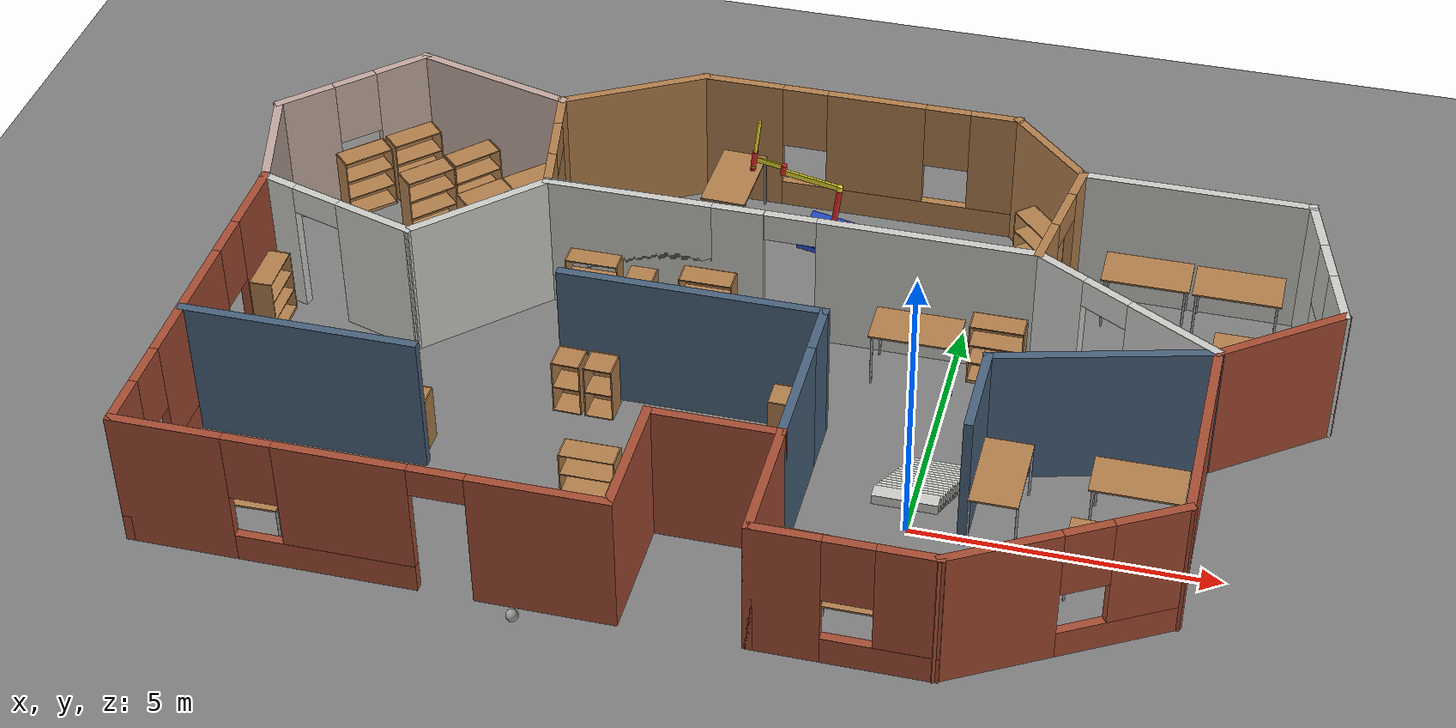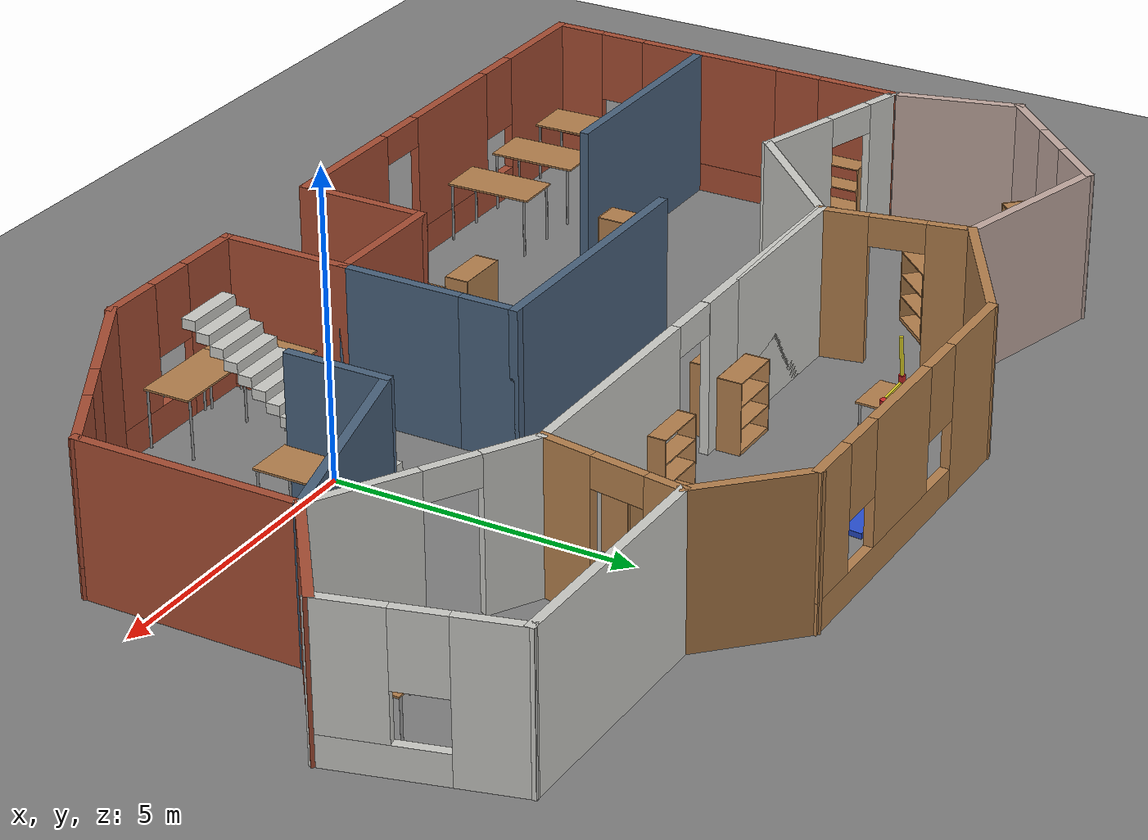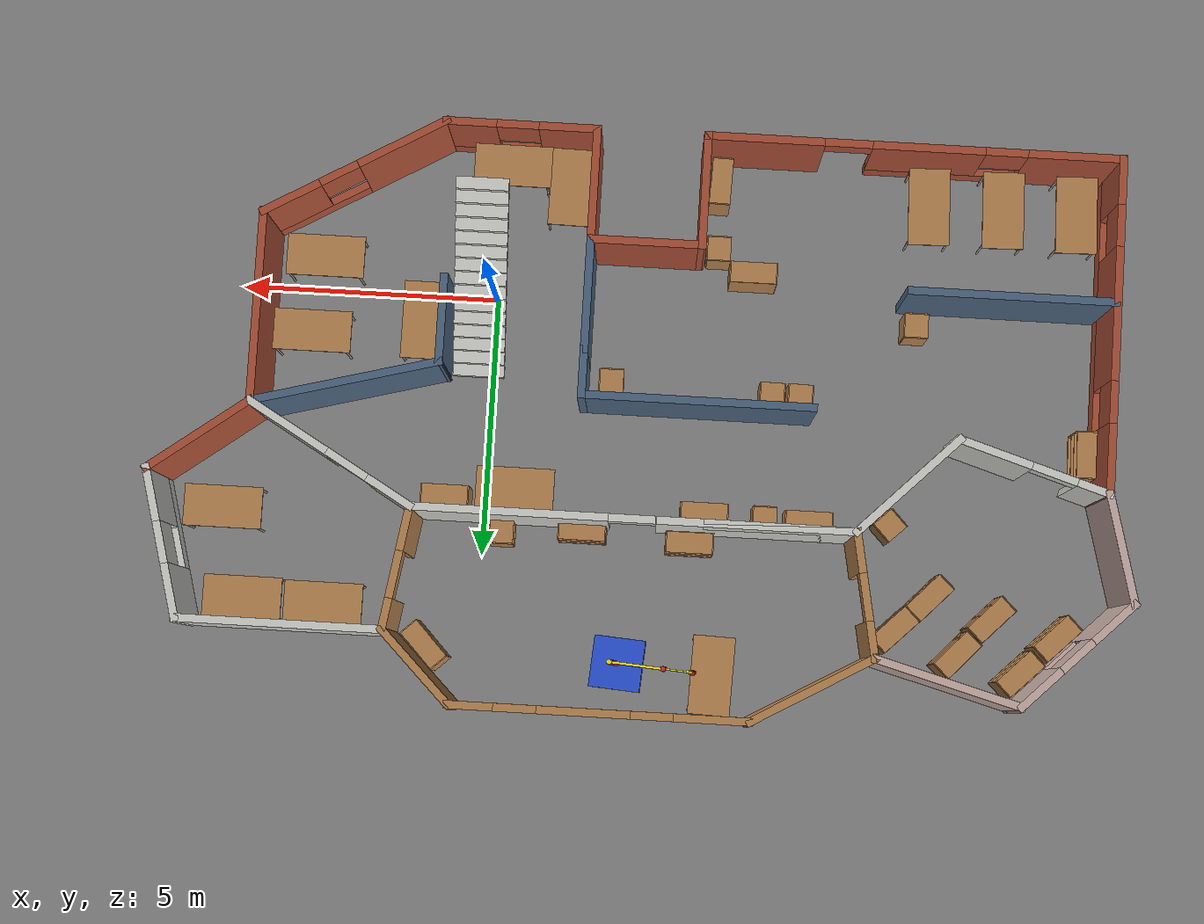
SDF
<sdf version="1.6">
 <world name="default">
  <light name="sun" type="directional">
   <pose>0 0 10 0 -0 0</pose>
   <diffuse>0.8 0.8 0.8 1</diffuse>
   <specular>0.2 0.2 0.2 1</specular>
   <attenuation>
    <range>1000</range>
    <constant>0.9</constant>
    <linear>0.01</linear>
    <quadratic>0.001</quadratic>
   </attenuation>
   <direction>-0.5 0.1 -0.9</direction>
  </light>
  <gravity>0 0 -9.8</gravity>
  <magnetic_field>6e-06 2.3e-05 -4.2e-05</magnetic_field>
  <atmosphere type="adiabatic"/>
  <physics name="default_physics" default="0" type="ode">
   <max_step_size>0.001</max_step_size>
   <real_time_factor>1</real_time_factor>
   <real_time_update_rate>1000</real_time_update_rate>
  </physics>
  <scene><ambient>0.4 0.4 0.4 1</ambient><background>0.7 0.7 0.7 1</background><shadows>1</shadows></scene>
  <spherical_coordinates>
   <surface_model>EARTH_WGS84</surface_model>
   <latitude_deg>0</latitude_deg>
   <longitude_deg>0</longitude_deg>
   <elevation>0</elevation>
   <heading_deg>0</heading_deg>
  </spherical_coordinates>
  <model name="ground_plane">
   <static>1</static>
   <link name="link">
    <collision name="collision">
     <geometry><plane><normal>0 0 1</normal><size>100 100</size></plane></geometry>
    </collision>
    <visual name="visual">
     <geometry><plane><normal>0 0 1</normal><size>100 100</size></plane></geometry>
     <material>
      <ambient>0.5 0.5 0.5 1</ambient>
      <diffuse>0.5 0.5 0.5 1</diffuse>
      <specular>0.1 0.1 0.1 1</specular>
     </material>
    </visual>
   </link>
  </model>
  <model name="Office">
   <pose>-3.04392 2.451 0 0 -0 0</pose>
   <link name="Stairs_0">
    <visual name="Stairs_0_Visual_0">
     <pose>3.33571 -1.04566 0.083333 0 -0 0</pose>
     <geometry><box><size>1 0.233333 0.166667</size></box></geometry>
     <material>
      <script><uri>file://media/materials/scripts/gazebo.material</uri><name>Gazebo/CeilingTiled</name></script>
      <ambient>1 1 1 1</ambient>
     </material>
     <meta><layer>0</layer></meta>
    </visual>
    <collision name="Stairs_0_Collision_0">
     <geometry><box><size>1 0.233333 0.166667</size></box></geometry>
     <pose>3.33571 -1.04566 0.083333 0 -0 0</pose>
    </collision>
    <visual name="Stairs_0_Visual_1">
     <pose>3.33571 -1.279 0.25 0 -0 0</pose>
     <geometry><box><size>1 0.233333 0.166667</size></box></geometry>
     <material>
      <script><uri>file://media/materials/scripts/gazebo.material</uri><name>Gazebo/CeilingTiled</name></script>
      <ambient>1 1 1 1</ambient>
     </material>
     <meta><layer>0</layer></meta>
    </visual>
    <collision name="Stairs_0_Collision_1">
     <geometry><box><size>1 0.233333 0.166667</size></box></geometry>
     <pose>3.33571 -1.279 0.25 0 -0 0</pose>
    </collision>
    <visual name="Stairs_0_Visual_2">
     <pose>3.33571 -1.51233 0.416667 0 -0 0</pose>
     <geometry><box><size>1 0.233333 0.166667</size></box></geometry>
     <material>
      <script><uri>file://media/materials/scripts/gazebo.material</uri><name>Gazebo/CeilingTiled</name></script>
      <ambient>1 1 1 1</ambient>
     </material>
     <meta><layer>0</layer></meta>
    </visual>
    <collision name="Stairs_0_Collision_2">
     <geometry><box><size>1 0.233333 0.166667</size></box></geometry>
     <pose>3.33571 -1.51233 0.416667 0 -0 0</pose>
    </collision>
    <visual name="Stairs_0_Visual_3">
     <pose>3.33571 -1.74566 0.583333 0 -0 0</pose>
     <geometry><box><size>1 0.233333 0.166667</size></box></geometry>
     <material>
      <script><uri>file://media/materials/scripts/gazebo.material</uri><name>Gazebo/CeilingTiled</name></script>
      <ambient>1 1 1 1</ambient>
     </material>
     <meta><layer>0</layer></meta>
    </visual>
    <collision name="Stairs_0_Collision_3">
     <geometry><box><size>1 0.233333 0.166667</size></box></geometry>
     <pose>3.33571 -1.74566 0.583333 0 -0 0</pose>
    </collision>
    <visual name="Stairs_0_Visual_4">
     <pose>3.33571 -1.979 0.75 0 -0 0</pose>
     <geometry><box><size>1 0.233333 0.166667</size></box></geometry>
     <material>
      <script><uri>file://media/materials/scripts/gazebo.material</uri><name>Gazebo/CeilingTiled</name></script>
      <ambient>1 1 1 1</ambient>
     </material>
     <meta><layer>0</layer></meta>
    </visual>
    <collision name="Stairs_0_Collision_4">
     <geometry><box><size>1 0.233333 0.166667</size></box></geometry>
     <pose>3.33571 -1.979 0.75 0 -0 0</pose>
    </collision>
    <visual name="Stairs_0_Visual_5">
     <pose>3.33571 -2.21233 0.916667 0 -0 0</pose>
     <geometry><box><size>1 0.233333 0.166667</size></box></geometry>
     <material>
      <script><uri>file://media/materials/scripts/gazebo.material</uri><name>Gazebo/CeilingTiled</name></script>
      <ambient>1 1 1 1</ambient>
     </material>
     <meta><layer>0</layer></meta>
    </visual>
    <collision name="Stairs_0_Collision_5">
     <geometry><box><size>1 0.233333 0.166667</size></box></geometry>
     <pose>3.33571 -2.21233 0.916667 0 -0 0</pose>
    </collision>
    <visual name="Stairs_0_Visual_6">
     <pose>3.33571 -2.44566 1.08333 0 -0 0</pose>
     <geometry><box><size>1 0.233333 0.166667</size></box></geometry>
     <material>
      <script><uri>file://media/materials/scripts/gazebo.material</uri><name>Gazebo/CeilingTiled</name></script>
      <ambient>1 1 1 1</ambient>
     </material>
     <meta><layer>0</layer></meta>
    </visual>
    <collision name="Stairs_0_Collision_6">
     <geometry><box><size>1 0.233333 0.166667</size></box></geometry>
     <pose>3.33571 -2.44566 1.08333 0 -0 0</pose>
    </collision>
    <visual name="Stairs_0_Visual_7">
     <pose>3.33571 -2.679 1.25 0 -0 0</pose>
     <geometry><box><size>1 0.233333 0.166667</size></box></geometry>
     <material>
      <script><uri>file://media/materials/scripts/gazebo.material</uri><name>Gazebo/CeilingTiled</name></script>
      <ambient>1 1 1 1</ambient>
     </material>
     <meta><layer>0</layer></meta>
    </visual>
    <collision name="Stairs_0_Collision_7">
     <geometry><box><size>1 0.233333 0.166667</size></box></geometry>
     <pose>3.33571 -2.679 1.25 0 -0 0</pose>
    </collision>
    <visual name="Stairs_0_Visual_8">
     <pose>3.33571 -2.91233 1.41667 0 -0 0</pose>
     <geometry><box><size>1 0.233333 0.166667</size></box></geometry>
     <material>
      <script><uri>file://media/materials/scripts/gazebo.material</uri><name>Gazebo/CeilingTiled</name></script>
      <ambient>1 1 1 1</ambient>
     </material>
     <meta><layer>0</layer></meta>
    </visual>
    <collision name="Stairs_0_Collision_8">
     <geometry><box><size>1 0.233333 0.166667</size></box></geometry>
     <pose>3.33571 -2.91233 1.41667 0 -0 0</pose>
    </collision>
    <visual name="Stairs_0_Visual_9">
     <pose>3.33571 -3.14566 1.58333 0 -0 0</pose>
     <geometry><box><size>1 0.233333 0.166667</size></box></geometry>
     <material>
      <script><uri>file://media/materials/scripts/gazebo.material</uri><name>Gazebo/CeilingTiled</name></script>
      <ambient>1 1 1 1</ambient>
     </material>
     <meta><layer>0</layer></meta>
    </visual>
    <collision name="Stairs_0_Collision_9">
     <geometry><box><size>1 0.233333 0.166667</size></box></geometry>
     <pose>3.33571 -3.14566 1.58333 0 -0 0</pose>
    </collision>
    <visual name="Stairs_0_Visual_10">
     <pose>3.33571 -3.379 1.75 0 -0 0</pose>
     <geometry><box><size>1 0.233333 0.166667</size></box></geometry>
     <material>
      <script><uri>file://media/materials/scripts/gazebo.material</uri><name>Gazebo/CeilingTiled</name></script>
      <ambient>1 1 1 1</ambient>
     </material>
     <meta><layer>0</layer></meta>
    </visual>
    <collision name="Stairs_0_Collision_10">
     <geometry><box><size>1 0.233333 0.166667</size></box></geometry>
     <pose>3.33571 -3.379 1.75 0 -0 0</pose>
    </collision>
    <visual name="Stairs_0_Visual_11">
     <pose>3.33571 -3.61233 1.91667 0 -0 0</pose>
     <geometry><box><size>1 0.233333 0.166667</size></box></geometry>
     <material>
      <script><uri>file://media/materials/scripts/gazebo.material</uri><name>Gazebo/CeilingTiled</name></script>
      <ambient>1 1 1 1</ambient>
     </material>
     <meta><layer>0</layer></meta>
    </visual>
    <collision name="Stairs_0_Collision_11">
     <geometry><box><size>1 0.233333 0.166667</size></box></geometry>
     <pose>3.33571 -3.61233 1.91667 0 -0 0</pose>
    </collision>
    <visual name="Stairs_0_Visual_12">
     <pose>3.33571 -3.84566 2.08333 0 -0 0</pose>
     <geometry><box><size>1 0.233333 0.166667</size></box></geometry>
     <material>
      <script><uri>file://media/materials/scripts/gazebo.material</uri><name>Gazebo/CeilingTiled</name></script>
      <ambient>1 1 1 1</ambient>
     </material>
     <meta><layer>0</layer></meta>
    </visual>
    <collision name="Stairs_0_Collision_12">
     <geometry><box><size>1 0.233333 0.166667</size></box></geometry>
     <pose>3.33571 -3.84566 2.08333 0 -0 0</pose>
    </collision>
    <visual name="Stairs_0_Visual_13">
     <pose>3.33571 -4.079 2.25 0 -0 0</pose>
     <geometry><box><size>1 0.233333 0.166667</size></box></geometry>
     <material>
      <script><uri>file://media/materials/scripts/gazebo.material</uri><name>Gazebo/CeilingTiled</name></script>
      <ambient>1 1 1 1</ambient>
     </material>
     <meta><layer>0</layer></meta>
    </visual>
    <collision name="Stairs_0_Collision_13">
     <geometry><box><size>1 0.233333 0.166667</size></box></geometry>
     <pose>3.33571 -4.079 2.25 0 -0 0</pose>
    </collision>
    <visual name="Stairs_0_Visual_14">
     <pose>3.33571 -4.31233 2.41667 0 -0 0</pose>
     <geometry><box><size>1 0.233333 0.166667</size></box></geometry>
     <material>
      <script><uri>file://media/materials/scripts/gazebo.material</uri><name>Gazebo/CeilingTiled</name></script>
      <ambient>1 1 1 1</ambient>
     </material>
     <meta><layer>0</layer></meta>
    </visual>
    <collision name="Stairs_0_Collision_14">
     <geometry><box><size>1 0.233333 0.166667</size></box></geometry>
     <pose>3.33571 -4.31233 2.41667 0 -0 0</pose>
    </collision>
   </link>
   <link name="Wall_1">
    <pose>-8.71372 -2.30484 0 0 0 -1.5708</pose>
    <visual name="Wall_1_Visual_0">
     <pose>-2.54455 0 1.25 0 -0 0</pose>
     <geometry><box><size>1.4109 0.15 2.5</size></box></geometry>
     <material>
      <script><uri>file://media/materials/scripts/gazebo.material</uri><name>Gazebo/Bricks</name></script>
      <ambient>1 1 1 1</ambient>
     </material>
     <meta><layer>0</layer></meta>
    </visual>
    <collision name="Wall_1_Collision_0">
     <geometry><box><size>1.4109 0.15 2.5</size></box></geometry>
     <pose>-2.54455 0 1.25 0 -0 0</pose>
    </collision>
    <visual name="Wall_1_Visual_1">
     <pose>0.70545 0 0.25 0 -0 0</pose>
     <geometry><box><size>5.0891 0.15 0.5</size></box></geometry>
     <material>
      <script><uri>file://media/materials/scripts/gazebo.material</uri><name>Gazebo/Bricks</name></script>
      <ambient>1 1 1 1</ambient>
     </material>
     <meta><layer>0</layer></meta>
    </visual>
    <collision name="Wall_1_Collision_1">
     <geometry><box><size>5.0891 0.15 0.5</size></box></geometry>
     <pose>0.70545 0 0.25 0 -0 0</pose>
    </collision>
    <visual name="Wall_1_Visual_2">
     <pose>0.236713 0 1.5 0 -0 0</pose>
     <geometry><box><size>2.55163 0.15 2</size></box></geometry>
     <material>
      <script><uri>file://media/materials/scripts/gazebo.material</uri><name>Gazebo/Bricks</name></script>
      <ambient>1 1 1 1</ambient>
     </material>
     <meta><layer>0</layer></meta>
    </visual>
    <collision name="Wall_1_Collision_2">
     <geometry><box><size>2.55163 0.15 2</size></box></geometry>
     <pose>0.236713 0 1.5 0 -0 0</pose>
    </collision>
    <visual name="Wall_1_Visual_3">
     <pose>2.78126 0 1.5 0 -0 0</pose>
     <geometry><box><size>0.937474 0.15 2</size></box></geometry>
     <material>
      <script><uri>file://media/materials/scripts/gazebo.material</uri><name>Gazebo/Bricks</name></script>
      <ambient>1 1 1 1</ambient>
     </material>
     <meta><layer>0</layer></meta>
    </visual>
    <collision name="Wall_1_Collision_3">
     <geometry><box><size>0.937474 0.15 2</size></box></geometry>
     <pose>2.78126 0 1.5 0 -0 0</pose>
    </collision>
    <visual name="Wall_1_Visual_4">
     <pose>-1.4391 0 1.9 0 -0 0</pose>
     <geometry><box><size>0.8 0.15 1.2</size></box></geometry>
     <material>
      <script><uri>file://media/materials/scripts/gazebo.material</uri><name>Gazebo/Bricks</name></script>
      <ambient>1 1 1 1</ambient>
     </material>
     <meta><layer>0</layer></meta>
    </visual>
    <collision name="Wall_1_Collision_4">
     <geometry><box><size>0.8 0.15 1.2</size></box></geometry>
     <pose>-1.4391 0 1.9 0 -0 0</pose>
    </collision>
    <visual name="Wall_1_Visual_5">
     <pose>1.91253 0 1.9 0 -0 0</pose>
     <geometry><box><size>0.8 0.15 1.2</size></box></geometry>
     <material>
      <script><uri>file://media/materials/scripts/gazebo.material</uri><name>Gazebo/Bricks</name></script>
      <ambient>1 1 1 1</ambient>
     </material>
     <meta><layer>0</layer></meta>
    </visual>
    <collision name="Wall_1_Collision_5">
     <geometry><box><size>0.8 0.15 1.2</size></box></geometry>
     <pose>1.91253 0 1.9 0 -0 0</pose>
    </collision>
   </link>
   <link name="Wall_10">
    <pose>0.127786 1.84516 0 0 -0 3.14159</pose>
    <visual name="Wall_10_Visual_0">
     <pose>-2.36055 0 1.25 0 -0 0</pose>
     <geometry><box><size>3.77889 0.15 2.5</size></box></geometry>
     <material>
      <script><uri>file://media/materials/scripts/gazebo.material</uri><name>Gazebo/CeilingTiled</name></script>
      <ambient>1 1 1 1</ambient>
     </material>
     <meta><layer>0</layer></meta>
    </visual>
    <collision name="Wall_10_Collision_0">
     <geometry><box><size>3.77889 0.15 2.5</size></box></geometry>
     <pose>-2.36055 0 1.25 0 -0 0</pose>
    </collision>
    <visual name="Wall_10_Visual_1">
     <pose>2.33945 0 1.25 0 -0 0</pose>
     <geometry><box><size>3.82111 0.15 2.5</size></box></geometry>
     <material>
      <script><uri>file://media/materials/scripts/gazebo.material</uri><name>Gazebo/CeilingTiled</name></script>
      <ambient>1 1 1 1</ambient>
     </material>
     <meta><layer>0</layer></meta>
    </visual>
    <collision name="Wall_10_Collision_1">
     <geometry><box><size>3.82111 0.15 2.5</size></box></geometry>
     <pose>2.33945 0 1.25 0 -0 0</pose>
    </collision>
    <visual name="Wall_10_Visual_2">
     <pose>2.78446 0 1.25 0 -0 0</pose>
     <geometry><box><size>2.93108 0.15 2.5</size></box></geometry>
     <material>
      <script><uri>file://media/materials/scripts/gazebo.material</uri><name>Gazebo/CeilingTiled</name></script>
      <ambient>1 1 1 1</ambient>
     </material>
     <meta><layer>0</layer></meta>
    </visual>
    <collision name="Wall_10_Collision_2">
     <geometry><box><size>2.93108 0.15 2.5</size></box></geometry>
     <pose>2.78446 0 1.25 0 -0 0</pose>
    </collision>
    <visual name="Wall_10_Visual_3">
     <pose>-0.026096 0 2.25 0 -0 0</pose>
     <geometry><box><size>0.890023 0.15 0.5</size></box></geometry>
     <material>
      <script><uri>file://media/materials/scripts/gazebo.material</uri><name>Gazebo/CeilingTiled</name></script>
      <ambient>1 1 1 1</ambient>
     </material>
     <meta><layer>0</layer></meta>
    </visual>
    <collision name="Wall_10_Collision_3">
     <geometry><box><size>0.890023 0.15 0.5</size></box></geometry>
     <pose>-0.026096 0 2.25 0 -0 0</pose>
    </collision>
   </link>
   <link name="Wall_11">
    <collision name="Wall_11_Collision">
     <geometry><box><size>2.75 0.15 2.5</size></box></geometry>
     <pose>0 0 1.25 0 -0 0</pose>
    </collision>
    <visual name="Wall_11_Visual">
     <pose>0 0 1.25 0 -0 0</pose>
     <geometry><box><size>2.75 0.15 2.5</size></box></geometry>
     <material>
      <script><uri>file://media/materials/scripts/gazebo.material</uri><name>Gazebo/CeilingTiled</name></script>
      <ambient>0.760784 0.662745 0.627451 1</ambient>
     </material>
     <meta><layer>0</layer></meta>
    </visual>
    <pose>-4.96645 0.925922 0 0 0 -2.35619</pose>
   </link>
   <link name="Wall_12">
    <pose>-7.29971 0.438422 0 0 -0 2.84525</pose>
    <visual name="Wall_12_Visual_0">
     <pose>-0.801772 0 1.25 0 -0 0</pose>
     <geometry><box><size>1.50337 0.15 2.5</size></box></geometry>
     <material>
      <script><uri>file://media/materials/scripts/gazebo.material</uri><name>Gazebo/CeilingTiled</name></script>
      <ambient>0.760784 0.662745 0.627451 1</ambient>
     </material>
     <meta><layer>0</layer></meta>
    </visual>
    <collision name="Wall_12_Collision_0">
     <geometry><box><size>1.50337 0.15 2.5</size></box></geometry>
     <pose>-0.801772 0 1.25 0 -0 0</pose>
    </collision>
    <visual name="Wall_12_Visual_1">
     <pose>1.20168 0 1.25 0 -0 0</pose>
     <geometry><box><size>0.703545 0.15 2.5</size></box></geometry>
     <material>
      <script><uri>file://media/materials/scripts/gazebo.material</uri><name>Gazebo/CeilingTiled</name></script>
      <ambient>0.760784 0.662745 0.627451 1</ambient>
     </material>
     <meta><layer>0</layer></meta>
    </visual>
    <collision name="Wall_12_Collision_1">
     <geometry><box><size>0.703545 0.15 2.5</size></box></geometry>
     <pose>1.20168 0 1.25 0 -0 0</pose>
    </collision>
    <visual name="Wall_12_Visual_2">
     <pose>0.399912 0 2.25 0 -0 0</pose>
     <geometry><box><size>0.9 0.15 0.5</size></box></geometry>
     <material>
      <script><uri>file://media/materials/scripts/gazebo.material</uri><name>Gazebo/CeilingTiled</name></script>
      <ambient>0.760784 0.662745 0.627451 1</ambient>
     </material>
     <meta><layer>0</layer></meta>
    </visual>
    <collision name="Wall_12_Collision_2">
     <geometry><box><size>0.9 0.15 0.5</size></box></geometry>
     <pose>0.399912 0 2.25 0 -0 0</pose>
    </collision>
   </link>
   <link name="Wall_13">
    <collision name="Wall_13_Collision">
     <geometry><box><size>0.15 0.15 2.5</size></box></geometry>
     <pose>0 0 1.25 0 -0 0</pose>
    </collision>
    <visual name="Wall_13_Visual">
     <pose>0 0 1.25 0 -0 0</pose>
     <geometry><box><size>0.15 0.15 2.5</size></box></geometry>
     <material>
      <script><uri>file://media/materials/scripts/gazebo.material</uri><name>Gazebo/Grey</name></script>
      <ambient>1 1 1 1</ambient>
     </material>
     <meta><layer>0</layer></meta>
    </visual>
    <pose>-8.71372 0.870161 0 0 -0 0</pose>
   </link>
   <link name="Wall_17">
    <collision name="Wall_17_Collision">
     <geometry><box><size>2.25 0.15 2.5</size></box></geometry>
     <pose>0 0 1.25 0 -0 0</pose>
    </collision>
    <visual name="Wall_17_Visual">
     <pose>0 0 1.25 0 -0 0</pose>
     <geometry><box><size>2.25 0.15 2.5</size></box></geometry>
     <material>
      <script><uri>file://media/materials/scripts/gazebo.material</uri><name>Gazebo/Grey</name></script>
      <ambient>0.760784 0.662745 0.627451 1</ambient>
     </material>
     <meta><layer>0</layer></meta>
    </visual>
    <pose>-8.98548 1.88438 0 0 -0 1.8326</pose>
   </link>
   <link name="Wall_18">
    <pose>-8.24961 3.90623 0 0 -0 0.785398</pose>
    <visual name="Wall_18_Visual_0">
     <pose>-0.945432 0 1.25 0 -0 0</pose>
     <geometry><box><size>1.10913 0.15 2.5</size></box></geometry>
     <material>
      <script><uri>file://media/materials/scripts/gazebo.material</uri><name>Gazebo/Grey</name></script>
      <ambient>0.760784 0.662745 0.627451 1</ambient>
     </material>
     <meta><layer>0</layer></meta>
    </visual>
    <collision name="Wall_18_Collision_0">
     <geometry><box><size>1.10913 0.15 2.5</size></box></geometry>
     <pose>-0.945432 0 1.25 0 -0 0</pose>
    </collision>
    <visual name="Wall_18_Visual_1">
     <pose>0.554568 0 0.25 0 -0 0</pose>
     <geometry><box><size>1.89087 0.15 0.5</size></box></geometry>
     <material>
      <script><uri>file://media/materials/scripts/gazebo.material</uri><name>Gazebo/Grey</name></script>
      <ambient>0.760784 0.662745 0.627451 1</ambient>
     </material>
     <meta><layer>0</layer></meta>
    </visual>
    <collision name="Wall_18_Collision_1">
     <geometry><box><size>1.89087 0.15 0.5</size></box></geometry>
     <pose>0.554568 0 0.25 0 -0 0</pose>
    </collision>
    <visual name="Wall_18_Visual_2">
     <pose>0.954568 0 1.5 0 -0 0</pose>
     <geometry><box><size>1.09086 0.15 2</size></box></geometry>
     <material>
      <script><uri>file://media/materials/scripts/gazebo.material</uri><name>Gazebo/Grey</name></script>
      <ambient>0.760784 0.662745 0.627451 1</ambient>
     </material>
     <meta><layer>0</layer></meta>
    </visual>
    <collision name="Wall_18_Collision_2">
     <geometry><box><size>1.09086 0.15 2</size></box></geometry>
     <pose>0.954568 0 1.5 0 -0 0</pose>
    </collision>
    <visual name="Wall_18_Visual_3">
     <pose>0.009135 0 1.9 0 -0 0</pose>
     <geometry><box><size>0.8 0.15 1.2</size></box></geometry>
     <material>
      <script><uri>file://media/materials/scripts/gazebo.material</uri><name>Gazebo/Grey</name></script>
      <ambient>0.760784 0.662745 0.627451 1</ambient>
     </material>
     <meta><layer>0</layer></meta>
    </visual>
    <collision name="Wall_18_Collision_3">
     <geometry><box><size>0.8 0.15 1.2</size></box></geometry>
     <pose>0.009135 0 1.9 0 -0 0</pose>
    </collision>
   </link>
   <link name="Wall_19">
    <collision name="Wall_19_Collision">
     <geometry><box><size>3 0.15 2.5</size></box></geometry>
     <pose>0 0 1.25 0 -0 0</pose>
    </collision>
    <visual name="Wall_19_Visual">
     <pose>0 0 1.25 0 -0 0</pose>
     <geometry><box><size>3 0.15 2.5</size></box></geometry>
     <material>
      <script><uri>file://media/materials/scripts/gazebo.material</uri><name>Gazebo/Grey</name></script>
      <ambient>0.760784 0.662745 0.627451 1</ambient>
     </material>
     <meta><layer>0</layer></meta>
    </visual>
    <pose>-5.86554 4.54504 0 0 0 -0.261799</pose>
   </link>
   <link name="Wall_2">
    <pose>-4.78872 -5.47984 0 0 -0 0</pose>
    <visual name="Wall_2_Visual_0">
     <pose>-3.06397 0 1.25 0 -0 0</pose>
     <geometry><box><size>1.87207 0.15 2.5</size></box></geometry>
     <material>
      <script><uri>file://media/materials/scripts/gazebo.material</uri><name>Gazebo/Bricks</name></script>
      <ambient>1 1 1 1</ambient>
     </material>
     <meta><layer>0</layer></meta>
    </visual>
    <collision name="Wall_2_Collision_0">
     <geometry><box><size>1.87207 0.15 2.5</size></box></geometry>
     <pose>-3.06397 0 1.25 0 -0 0</pose>
    </collision>
    <visual name="Wall_2_Visual_1">
     <pose>2.85602 0 1.25 0 -0 0</pose>
     <geometry><box><size>2.28796 0.15 2.5</size></box></geometry>
     <material>
      <script><uri>file://media/materials/scripts/gazebo.material</uri><name>Gazebo/Bricks</name></script>
      <ambient>1 1 1 1</ambient>
     </material>
     <meta><layer>0</layer></meta>
    </visual>
    <collision name="Wall_2_Collision_1">
     <geometry><box><size>2.28796 0.15 2.5</size></box></geometry>
     <pose>2.85602 0 1.25 0 -0 0</pose>
    </collision>
    <visual name="Wall_2_Visual_2">
     <pose>-0.657948 0 0.25 0 -0 0</pose>
     <geometry><box><size>2.93997 0.15 0.5</size></box></geometry>
     <material>
      <script><uri>file://media/materials/scripts/gazebo.material</uri><name>Gazebo/Bricks</name></script>
      <ambient>1 1 1 1</ambient>
     </material>
     <meta><layer>0</layer></meta>
    </visual>
    <collision name="Wall_2_Collision_2">
     <geometry><box><size>2.93997 0.15 0.5</size></box></geometry>
     <pose>-0.657948 0 0.25 0 -0 0</pose>
    </collision>
    <visual name="Wall_2_Visual_3">
     <pose>-0.257948 0 1.5 0 -0 0</pose>
     <geometry><box><size>2.13997 0.15 2</size></box></geometry>
     <material>
      <script><uri>file://media/materials/scripts/gazebo.material</uri><name>Gazebo/Bricks</name></script>
      <ambient>1 1 1 1</ambient>
     </material>
     <meta><layer>0</layer></meta>
    </visual>
    <collision name="Wall_2_Collision_3">
     <geometry><box><size>2.13997 0.15 2</size></box></geometry>
     <pose>-0.257948 0 1.5 0 -0 0</pose>
    </collision>
    <visual name="Wall_2_Visual_4">
     <pose>-1.72793 0 1.9 0 -0 0</pose>
     <geometry><box><size>0.8 0.15 1.2</size></box></geometry>
     <material>
      <script><uri>file://media/materials/scripts/gazebo.material</uri><name>Gazebo/Bricks</name></script>
      <ambient>1 1 1 1</ambient>
     </material>
     <meta><layer>0</layer></meta>
    </visual>
    <collision name="Wall_2_Collision_4">
     <geometry><box><size>0.8 0.15 1.2</size></box></geometry>
     <pose>-1.72793 0 1.9 0 -0 0</pose>
    </collision>
    <visual name="Wall_2_Visual_5">
     <pose>1.26204 0 2.25 0 -0 0</pose>
     <geometry><box><size>0.9 0.15 0.5</size></box></geometry>
     <material>
      <script><uri>file://media/materials/scripts/gazebo.material</uri><name>Gazebo/Bricks</name></script>
      <ambient>1 1 1 1</ambient>
     </material>
     <meta><layer>0</layer></meta>
    </visual>
    <collision name="Wall_2_Collision_5">
     <geometry><box><size>0.9 0.15 0.5</size></box></geometry>
     <pose>1.26204 0 2.25 0 -0 0</pose>
    </collision>
   </link>
   <link name="Wall_20">
    <pose>-4.26816 3.01069 0 0 0 -1.38346</pose>
    <visual name="Wall_20_Visual_0">
     <pose>-0.872909 0 1.25 0 -0 0</pose>
     <geometry><box><size>0.77676 0.15 2.5</size></box></geometry>
     <material>
      <script><uri>file://media/materials/scripts/gazebo.material</uri><name>Gazebo/Wood</name></script>
      <ambient>1 1 1 1</ambient>
     </material>
     <meta><layer>0</layer></meta>
    </visual>
    <collision name="Wall_20_Collision_0">
     <geometry><box><size>0.77676 0.15 2.5</size></box></geometry>
     <pose>-0.872909 0 1.25 0 -0 0</pose>
    </collision>
    <visual name="Wall_20_Visual_1">
     <pose>0.83838 0 1.25 0 -0 0</pose>
     <geometry><box><size>0.845817 0.15 2.5</size></box></geometry>
     <material>
      <script><uri>file://media/materials/scripts/gazebo.material</uri><name>Gazebo/Wood</name></script>
      <ambient>1 1 1 1</ambient>
     </material>
     <meta><layer>0</layer></meta>
    </visual>
    <collision name="Wall_20_Collision_1">
     <geometry><box><size>0.845817 0.15 2.5</size></box></geometry>
     <pose>0.83838 0 1.25 0 -0 0</pose>
    </collision>
    <visual name="Wall_20_Visual_2">
     <pose>-0.034529 0 2.25 0 -0 0</pose>
     <geometry><box><size>0.9 0.15 0.5</size></box></geometry>
     <material>
      <script><uri>file://media/materials/scripts/gazebo.material</uri><name>Gazebo/Wood</name></script>
      <ambient>1 1 1 1</ambient>
     </material>
     <meta><layer>0</layer></meta>
    </visual>
    <collision name="Wall_20_Collision_2">
     <geometry><box><size>0.9 0.15 0.5</size></box></geometry>
     <pose>-0.034529 0 2.25 0 -0 0</pose>
    </collision>
   </link>
   <link name="Wall_22">
    <collision name="Wall_22_Collision">
     <geometry><box><size>2.75 0.15 2.5</size></box></geometry>
     <pose>0 0 1.25 0 -0 0</pose>
    </collision>
    <visual name="Wall_22_Visual">
     <pose>0 0 1.25 0 -0 0</pose>
     <geometry><box><size>2.75 0.15 2.5</size></box></geometry>
     <material>
      <script><uri>file://media/materials/scripts/gazebo.material</uri><name>Gazebo/Wood</name></script>
      <ambient>1 1 1 1</ambient>
     </material>
     <meta><layer>0</layer></meta>
    </visual>
    <pose>-3.36326 4.82622 0 0 -0 0.523599</pose>
   </link>
   <link name="Wall_23">
    <pose>0.562569 5.47623 0 0 -0 0</pose>
    <visual name="Wall_23_Visual_0">
     <pose>-2.13059 0 1.25 0 -0 0</pose>
     <geometry><box><size>1.48883 0.15 2.5</size></box></geometry>
     <material>
      <script><uri>file://media/materials/scripts/gazebo.material</uri><name>Gazebo/Wood</name></script>
      <ambient>1 1 1 1</ambient>
     </material>
     <meta><layer>0</layer></meta>
    </visual>
    <collision name="Wall_23_Collision_0">
     <geometry><box><size>1.48883 0.15 2.5</size></box></geometry>
     <pose>-2.13059 0 1.25 0 -0 0</pose>
    </collision>
    <visual name="Wall_23_Visual_1">
     <pose>0.744413 0 0.25 0 -0 0</pose>
     <geometry><box><size>4.26117 0.15 0.5</size></box></geometry>
     <material>
      <script><uri>file://media/materials/scripts/gazebo.material</uri><name>Gazebo/Wood</name></script>
      <ambient>1 1 1 1</ambient>
     </material>
     <meta><layer>0</layer></meta>
    </visual>
    <collision name="Wall_23_Collision_1">
     <geometry><box><size>4.26117 0.15 0.5</size></box></geometry>
     <pose>0.744413 0 0.25 0 -0 0</pose>
    </collision>
    <visual name="Wall_23_Visual_2">
     <pose>0.286009 0 1.5 0 -0 0</pose>
     <geometry><box><size>1.74437 0.15 2</size></box></geometry>
     <material>
      <script><uri>file://media/materials/scripts/gazebo.material</uri><name>Gazebo/Wood</name></script>
      <ambient>1 1 1 1</ambient>
     </material>
     <meta><layer>0</layer></meta>
    </visual>
    <collision name="Wall_23_Collision_2">
     <geometry><box><size>1.74437 0.15 2</size></box></geometry>
     <pose>0.286009 0 1.5 0 -0 0</pose>
    </collision>
    <visual name="Wall_23_Visual_3">
     <pose>2.4166 0 1.5 0 -0 0</pose>
     <geometry><box><size>0.916807 0.15 2</size></box></geometry>
     <material>
      <script><uri>file://media/materials/scripts/gazebo.material</uri><name>Gazebo/Wood</name></script>
      <ambient>1 1 1 1</ambient>
     </material>
     <meta><layer>0</layer></meta>
    </visual>
    <collision name="Wall_23_Collision_3">
     <geometry><box><size>0.916807 0.15 2</size></box></geometry>
     <pose>2.4166 0 1.5 0 -0 0</pose>
    </collision>
    <visual name="Wall_23_Visual_4">
     <pose>-0.986174 0 1.9 0 -0 0</pose>
     <geometry><box><size>0.8 0.15 1.2</size></box></geometry>
     <material>
      <script><uri>file://media/materials/scripts/gazebo.material</uri><name>Gazebo/Wood</name></script>
      <ambient>1 1 1 1</ambient>
     </material>
     <meta><layer>0</layer></meta>
    </visual>
    <collision name="Wall_23_Collision_4">
     <geometry><box><size>0.8 0.15 1.2</size></box></geometry>
     <pose>-0.986174 0 1.9 0 -0 0</pose>
    </collision>
    <visual name="Wall_23_Visual_5">
     <pose>1.55819 0 1.9 0 -0 0</pose>
     <geometry><box><size>0.8 0.15 1.2</size></box></geometry>
     <material>
      <script><uri>file://media/materials/scripts/gazebo.material</uri><name>Gazebo/Wood</name></script>
      <ambient>1 1 1 1</ambient>
     </material>
     <meta><layer>0</layer></meta>
    </visual>
    <collision name="Wall_23_Collision_5">
     <geometry><box><size>0.8 0.15 1.2</size></box></geometry>
     <pose>1.55819 0 1.9 0 -0 0</pose>
    </collision>
   </link>
   <link name="Wall_24">
    <collision name="Wall_24_Collision">
     <geometry><box><size>2 0.15 2.5</size></box></geometry>
     <pose>0 0 1.25 0 -0 0</pose>
    </collision>
    <visual name="Wall_24_Visual">
     <pose>0 0 1.25 0 -0 0</pose>
     <geometry><box><size>2 0.15 2.5</size></box></geometry>
     <material>
      <script><uri>file://media/materials/scripts/gazebo.material</uri><name>Gazebo/Wood</name></script>
      <ambient>1 1 1 1</ambient>
     </material>
     <meta><layer>0</layer></meta>
    </visual>
    <pose>4.01664 4.82215 0 0 0 -0.785398</pose>
   </link>
   <link name="Wall_25">
    <pose>4.48675 3.00662 0 0 0 -1.72788</pose>
    <visual name="Wall_25_Visual_0">
     <pose>-0.913451 0 1.25 0 -0 0</pose>
     <geometry><box><size>0.674972 0.15 2.5</size></box></geometry>
     <material>
      <script><uri>file://media/materials/scripts/gazebo.material</uri><name>Gazebo/Wood</name></script>
      <ambient>1 1 1 1</ambient>
     </material>
     <meta><layer>0</layer></meta>
    </visual>
    <collision name="Wall_25_Collision_0">
     <geometry><box><size>0.674972 0.15 2.5</size></box></geometry>
     <pose>-0.913451 0 1.25 0 -0 0</pose>
    </collision>
    <visual name="Wall_25_Visual_1">
     <pose>0.787486 0 1.25 0 -0 0</pose>
     <geometry><box><size>0.926902 0.15 2.5</size></box></geometry>
     <material>
      <script><uri>file://media/materials/scripts/gazebo.material</uri><name>Gazebo/Wood</name></script>
      <ambient>1 1 1 1</ambient>
     </material>
     <meta><layer>0</layer></meta>
    </visual>
    <collision name="Wall_25_Collision_1">
     <geometry><box><size>0.926902 0.15 2.5</size></box></geometry>
     <pose>0.787486 0 1.25 0 -0 0</pose>
    </collision>
    <visual name="Wall_25_Visual_2">
     <pose>-0.125965 0 2.25 0 -0 0</pose>
     <geometry><box><size>0.9 0.15 0.5</size></box></geometry>
     <material>
      <script><uri>file://media/materials/scripts/gazebo.material</uri><name>Gazebo/Wood</name></script>
      <ambient>1 1 1 1</ambient>
     </material>
     <meta><layer>0</layer></meta>
    </visual>
    <collision name="Wall_25_Collision_2">
     <geometry><box><size>0.9 0.15 0.5</size></box></geometry>
     <pose>-0.125965 0 2.25 0 -0 0</pose>
    </collision>
   </link>
   <link name="Wall_27">
    <collision name="Wall_27_Collision">
     <geometry><box><size>4 0.15 2.5</size></box></geometry>
     <pose>0 0 1.25 0 -0 0</pose>
    </collision>
    <visual name="Wall_27_Visual">
     <pose>0 0 1.25 0 -0 0</pose>
     <geometry><box><size>4 0.15 2.5</size></box></geometry>
     <material>
      <script><uri>file://media/materials/scripts/gazebo.material</uri><name>Gazebo/CeilingTiled</name></script>
      <ambient>1 1 1 1</ambient>
     </material>
     <meta><layer>0</layer></meta>
    </visual>
    <pose>6.59572 4.16808 0 0 -0 0</pose>
   </link>
   <link name="Wall_28">
    <pose>8.88953 2.79163 0 0 0 -1.309</pose>
    <visual name="Wall_28_Visual_0">
     <pose>-0.948837 0 1.25 0 -0 0</pose>
     <geometry><box><size>1.10233 0.15 2.5</size></box></geometry>
     <material>
      <script><uri>file://media/materials/scripts/gazebo.material</uri><name>Gazebo/CeilingTiled</name></script>
      <ambient>1 1 1 1</ambient>
     </material>
     <meta><layer>0</layer></meta>
    </visual>
    <collision name="Wall_28_Collision_0">
     <geometry><box><size>1.10233 0.15 2.5</size></box></geometry>
     <pose>-0.948837 0 1.25 0 -0 0</pose>
    </collision>
    <visual name="Wall_28_Visual_1">
     <pose>0.551163 0 0.25 0 -0 0</pose>
     <geometry><box><size>1.89767 0.15 0.5</size></box></geometry>
     <material>
      <script><uri>file://media/materials/scripts/gazebo.material</uri><name>Gazebo/CeilingTiled</name></script>
      <ambient>1 1 1 1</ambient>
     </material>
     <meta><layer>0</layer></meta>
    </visual>
    <collision name="Wall_28_Collision_1">
     <geometry><box><size>1.89767 0.15 0.5</size></box></geometry>
     <pose>0.551163 0 0.25 0 -0 0</pose>
    </collision>
    <visual name="Wall_28_Visual_2">
     <pose>0.951163 0 1.5 0 -0 0</pose>
     <geometry><box><size>1.09767 0.15 2</size></box></geometry>
     <material>
      <script><uri>file://media/materials/scripts/gazebo.material</uri><name>Gazebo/CeilingTiled</name></script>
      <ambient>1 1 1 1</ambient>
     </material>
     <meta><layer>0</layer></meta>
    </visual>
    <collision name="Wall_28_Collision_2">
     <geometry><box><size>1.09767 0.15 2</size></box></geometry>
     <pose>0.951163 0 1.5 0 -0 0</pose>
    </collision>
    <visual name="Wall_28_Visual_3">
     <pose>0.002327 0 1.9 0 -0 0</pose>
     <geometry><box><size>0.8 0.15 1.2</size></box></geometry>
     <material>
      <script><uri>file://media/materials/scripts/gazebo.material</uri><name>Gazebo/CeilingTiled</name></script>
      <ambient>1 1 1 1</ambient>
     </material>
     <meta><layer>0</layer></meta>
    </visual>
    <collision name="Wall_28_Collision_3">
     <geometry><box><size>0.8 0.15 1.2</size></box></geometry>
     <pose>0.002327 0 1.9 0 -0 0</pose>
    </collision>
   </link>
   <link name="Wall_29">
    <collision name="Wall_29_Collision">
     <geometry><box><size>2.44232 0.15 2.5</size></box></geometry>
     <pose>0 0 1.25 0 -0 0</pose>
    </collision>
    <visual name="Wall_29_Visual">
     <pose>0 0 1.25 0 -0 0</pose>
     <geometry><box><size>2.44232 0.15 2.5</size></box></geometry>
     <material>
      <script><uri>file://media/materials/scripts/gazebo.material</uri><name>Gazebo/Bricks</name></script>
      <ambient>1 1 1 1</ambient>
     </material>
     <meta><layer>0</layer></meta>
    </visual>
    <pose>8.33941 0.730175 0 0 0 -2.50102</pose>
   </link>
   <link name="Wall_3">
    <collision name="Wall_3_Collision">
     <geometry><box><size>2.25 0.15 2.5</size></box></geometry>
     <pose>0 0 1.25 0 -0 0</pose>
    </collision>
    <visual name="Wall_3_Visual">
     <pose>0 0 1.25 0 -0 0</pose>
     <geometry><box><size>2.25 0.15 2.5</size></box></geometry>
     <material>
      <script><uri>file://media/materials/scripts/gazebo.material</uri><name>Gazebo/Bricks</name></script>
      <ambient>1 1 1 1</ambient>
     </material>
     <meta><layer>0</layer></meta>
    </visual>
    <pose>-0.86372 -4.42984 0 0 -0 1.5708</pose>
   </link>
   <link name="Wall_30">
    <collision name="Wall_30_Collision">
     <geometry><box><size>3.75 0.15 2.5</size></box></geometry>
     <pose>0 0 1.25 0 -0 0</pose>
    </collision>
    <visual name="Wall_30_Visual">
     <pose>0 0 1.25 0 -0 0</pose>
     <geometry><box><size>3.75 0.15 2.5</size></box></geometry>
     <material>
      <script><uri>file://media/materials/scripts/gazebo.material</uri><name>Gazebo/Grey</name></script>
      <ambient>0.286275 0.384314 0.486275 1</ambient>
     </material>
     <meta><layer>0</layer></meta>
    </visual>
    <pose>5.68181 -0.420713 0 0 0 -2.87979</pose>
   </link>
   <link name="Wall_31">
    <collision name="Wall_31_Collision">
     <geometry><box><size>1.75 0.15 2.5</size></box></geometry>
     <pose>0 0 1.25 0 -0 0</pose>
    </collision>
    <visual name="Wall_31_Visual">
     <pose>0 0 1.25 0 -0 0</pose>
     <geometry><box><size>1.75 0.15 2.5</size></box></geometry>
     <material>
      <script><uri>file://media/materials/scripts/gazebo.material</uri><name>Gazebo/Grey</name></script>
      <ambient>0.286275 0.384314 0.486275 1</ambient>
     </material>
     <meta><layer>0</layer></meta>
    </visual>
    <pose>3.94314 -1.68659 0 0 0 -1.5708</pose>
   </link>
   <link name="Wall_33">
    <collision name="Wall_33_Collision">
     <geometry><box><size>4 0.15 2.5</size></box></geometry>
     <pose>0 0 1.25 0 -0 0</pose>
    </collision>
    <visual name="Wall_33_Visual">
     <pose>0 0 1.25 0 -0 0</pose>
     <geometry><box><size>4 0.15 2.5</size></box></geometry>
     <material>
      <script><uri>file://media/materials/scripts/gazebo.material</uri><name>Gazebo/Grey</name></script>
      <ambient>0.286275 0.384314 0.486275 1</ambient>
     </material>
     <meta><layer>0</layer></meta>
    </visual>
    <pose>-6.76403 -2.74712 0 0 -0 3.14159</pose>
   </link>
   <link name="Wall_35">
    <collision name="Wall_35_Collision">
     <geometry><box><size>2.25 0.15 2.5</size></box></geometry>
     <pose>0 0 1.25 0 -0 0</pose>
    </collision>
    <visual name="Wall_35_Visual">
     <pose>0 0 1.25 0 -0 0</pose>
     <geometry><box><size>2.25 0.15 2.5</size></box></geometry>
     <material>
      <script><uri>file://media/materials/scripts/gazebo.material</uri><name>Gazebo/Grey</name></script>
      <ambient>0.286275 0.384314 0.486275 1</ambient>
     </material>
     <meta><layer>0</layer></meta>
    </visual>
    <pose>1.23628 -2.32984 0 0 -0 1.5708</pose>
   </link>
   <link name="Wall_39">
    <collision name="Wall_39_Collision">
     <geometry><box><size>1 0.15 2.5</size></box></geometry>
     <pose>0 0 1.25 0 -0 0</pose>
    </collision>
    <visual name="Wall_39_Visual">
     <pose>0 0 1.25 0 -0 0</pose>
     <geometry><box><size>1 0.15 2.5</size></box></geometry>
     <material>
      <script><uri>file://media/materials/scripts/gazebo.material</uri><name>Gazebo/Grey</name></script>
      <ambient>0.286275 0.384314 0.486275 1</ambient>
     </material>
     <meta><layer>0</layer></meta>
    </visual>
    <pose>1.23628 -0.854839 0 0 -0 1.5708</pose>
   </link>
   <link name="Wall_4">
    <collision name="Wall_4_Collision">
     <geometry><box><size>2.25 0.15 2.5</size></box></geometry>
     <pose>0 0 1.25 0 -0 0</pose>
    </collision>
    <visual name="Wall_4_Visual">
     <pose>0 0 1.25 0 -0 0</pose>
     <geometry><box><size>2.25 0.15 2.5</size></box></geometry>
     <material>
      <script><uri>file://media/materials/scripts/gazebo.material</uri><name>Gazebo/Bricks</name></script>
      <ambient>1 1 1 1</ambient>
     </material>
     <meta><layer>0</layer></meta>
    </visual>
    <pose>0.18628 -3.37984 0 0 -0 0</pose>
   </link>
   <link name="Wall_40">
    <collision name="Wall_40_Collision">
     <geometry><box><size>4.5 0.15 2.5</size></box></geometry>
     <pose>0 0 1.25 0 -0 0</pose>
    </collision>
    <visual name="Wall_40_Visual">
     <pose>0 0 1.25 0 -0 0</pose>
     <geometry><box><size>4.5 0.15 2.5</size></box></geometry>
     <material>
      <script><uri>file://media/materials/scripts/gazebo.material</uri><name>Gazebo/Grey</name></script>
      <ambient>0.286275 0.384314 0.486275 1</ambient>
     </material>
     <meta><layer>0</layer></meta>
    </visual>
    <pose>-0.93872 -0.429839 0 0 -0 3.14159</pose>
   </link>
   <link name="Wall_5">
    <collision name="Wall_5_Collision">
     <geometry><box><size>2.25 0.15 2.5</size></box></geometry>
     <pose>0 0 1.25 0 -0 0</pose>
    </collision>
    <visual name="Wall_5_Visual">
     <pose>0 0 1.25 0 -0 0</pose>
     <geometry><box><size>2.25 0.15 2.5</size></box></geometry>
     <material>
      <script><uri>file://media/materials/scripts/gazebo.material</uri><name>Gazebo/Bricks</name></script>
      <ambient>1 1 1 1</ambient>
     </material>
     <meta><layer>0</layer></meta>
    </visual>
    <pose>1.23628 -4.42984 0 0 0 -1.5708</pose>
   </link>
   <link name="Wall_6">
    <pose>2.66128 -5.47984 0 0 -0 0</pose>
    <visual name="Wall_6_Visual_0">
     <pose>-0.910532 0 1.25 0 -0 0</pose>
     <geometry><box><size>1.17894 0.15 2.5</size></box></geometry>
     <material>
      <script><uri>file://media/materials/scripts/gazebo.material</uri><name>Gazebo/Bricks</name></script>
      <ambient>1 1 1 1</ambient>
     </material>
     <meta><layer>0</layer></meta>
    </visual>
    <collision name="Wall_6_Collision_0">
     <geometry><box><size>1.17894 0.15 2.5</size></box></geometry>
     <pose>-0.910532 0 1.25 0 -0 0</pose>
    </collision>
    <visual name="Wall_6_Visual_1">
     <pose>0.589468 0 0.25 0 -0 0</pose>
     <geometry><box><size>1.82106 0.15 0.5</size></box></geometry>
     <material>
      <script><uri>file://media/materials/scripts/gazebo.material</uri><name>Gazebo/Bricks</name></script>
      <ambient>1 1 1 1</ambient>
     </material>
     <meta><layer>0</layer></meta>
    </visual>
    <collision name="Wall_6_Collision_1">
     <geometry><box><size>1.82106 0.15 0.5</size></box></geometry>
     <pose>0.589468 0 0.25 0 -0 0</pose>
    </collision>
    <visual name="Wall_6_Visual_2">
     <pose>0.989468 0 1.5 0 -0 0</pose>
     <geometry><box><size>1.02106 0.15 2</size></box></geometry>
     <material>
      <script><uri>file://media/materials/scripts/gazebo.material</uri><name>Gazebo/Bricks</name></script>
      <ambient>1 1 1 1</ambient>
     </material>
     <meta><layer>0</layer></meta>
    </visual>
    <collision name="Wall_6_Collision_2">
     <geometry><box><size>1.02106 0.15 2</size></box></geometry>
     <pose>0.989468 0 1.5 0 -0 0</pose>
    </collision>
    <visual name="Wall_6_Visual_3">
     <pose>0.078935 0 1.9 0 -0 0</pose>
     <geometry><box><size>0.8 0.15 1.2</size></box></geometry>
     <material>
      <script><uri>file://media/materials/scripts/gazebo.material</uri><name>Gazebo/Bricks</name></script>
      <ambient>1 1 1 1</ambient>
     </material>
     <meta><layer>0</layer></meta>
    </visual>
    <collision name="Wall_6_Collision_3">
     <geometry><box><size>0.8 0.15 1.2</size></box></geometry>
     <pose>0.078935 0 1.9 0 -0 0</pose>
    </collision>
   </link>
   <link name="Wall_7">
    <pose>5.75338 -4.51734 0 0 -0 0.523599</pose>
    <visual name="Wall_7_Visual_0">
     <pose>-1.03165 0 1.25 0 -0 0</pose>
     <geometry><box><size>1.9367 0.15 2.5</size></box></geometry>
     <material>
      <script><uri>file://media/materials/scripts/gazebo.material</uri><name>Gazebo/Bricks</name></script>
      <ambient>1 1 1 1</ambient>
     </material>
     <meta><layer>0</layer></meta>
    </visual>
    <collision name="Wall_7_Collision_0">
     <geometry><box><size>1.9367 0.15 2.5</size></box></geometry>
     <pose>-1.03165 0 1.25 0 -0 0</pose>
    </collision>
    <visual name="Wall_7_Visual_1">
     <pose>0.968351 0 0.25 0 -0 0</pose>
     <geometry><box><size>2.0633 0.15 0.5</size></box></geometry>
     <material>
      <script><uri>file://media/materials/scripts/gazebo.material</uri><name>Gazebo/Bricks</name></script>
      <ambient>1 1 1 1</ambient>
     </material>
     <meta><layer>0</layer></meta>
    </visual>
    <collision name="Wall_7_Collision_1">
     <geometry><box><size>2.0633 0.15 0.5</size></box></geometry>
     <pose>0.968351 0 0.25 0 -0 0</pose>
    </collision>
    <visual name="Wall_7_Visual_2">
     <pose>1.36835 0 1.5 0 -0 0</pose>
     <geometry><box><size>1.2633 0.15 2</size></box></geometry>
     <material>
      <script><uri>file://media/materials/scripts/gazebo.material</uri><name>Gazebo/Bricks</name></script>
      <ambient>1 1 1 1</ambient>
     </material>
     <meta><layer>0</layer></meta>
    </visual>
    <collision name="Wall_7_Collision_2">
     <geometry><box><size>1.2633 0.15 2</size></box></geometry>
     <pose>1.36835 0 1.5 0 -0 0</pose>
    </collision>
    <visual name="Wall_7_Visual_3">
     <pose>0.336702 0 1.9 0 -0 0</pose>
     <geometry><box><size>0.8 0.15 1.2</size></box></geometry>
     <material>
      <script><uri>file://media/materials/scripts/gazebo.material</uri><name>Gazebo/Bricks</name></script>
      <ambient>1 1 1 1</ambient>
     </material>
     <meta><layer>0</layer></meta>
    </visual>
    <collision name="Wall_7_Collision_3">
     <geometry><box><size>0.8 0.15 1.2</size></box></geometry>
     <pose>0.336702 0 1.9 0 -0 0</pose>
    </collision>
   </link>
   <link name="Wall_8">
    <collision name="Wall_8_Collision">
     <geometry><box><size>3.75 0.15 2.5</size></box></geometry>
     <pose>0 0 1.25 0 -0 0</pose>
    </collision>
    <visual name="Wall_8_Visual">
     <pose>0 0 1.25 0 -0 0</pose>
     <geometry><box><size>3.75 0.15 2.5</size></box></geometry>
     <material>
      <script><uri>file://media/materials/scripts/gazebo.material</uri><name>Gazebo/Bricks</name></script>
      <ambient>1 1 1 1</ambient>
     </material>
     <meta><layer>0</layer></meta>
    </visual>
    <pose>7.42048 -1.75484 0 0 -0 1.5708</pose>
   </link>
   <link name="Wall_9">
    <pose>5.86163 0.945161 0 0 -0 2.61799</pose>
    <visual name="Wall_9_Visual_0">
     <pose>-0.96851 0 1.25 0 -0 0</pose>
     <geometry><box><size>1.81298 0.15 2.5</size></box></geometry>
     <material>
      <script><uri>file://media/materials/scripts/gazebo.material</uri><name>Gazebo/CeilingTiled</name></script>
      <ambient>1 1 1 1</ambient>
     </material>
     <meta><layer>0</layer></meta>
    </visual>
    <collision name="Wall_9_Collision_0">
     <geometry><box><size>1.81298 0.15 2.5</size></box></geometry>
     <pose>-0.96851 0 1.25 0 -0 0</pose>
    </collision>
    <visual name="Wall_9_Visual_1">
     <pose>1.35649 0 1.25 0 -0 0</pose>
     <geometry><box><size>1.03702 0.15 2.5</size></box></geometry>
     <material>
      <script><uri>file://media/materials/scripts/gazebo.material</uri><name>Gazebo/CeilingTiled</name></script>
      <ambient>1 1 1 1</ambient>
     </material>
     <meta><layer>0</layer></meta>
    </visual>
    <collision name="Wall_9_Collision_1">
     <geometry><box><size>1.03702 0.15 2.5</size></box></geometry>
     <pose>1.35649 0 1.25 0 -0 0</pose>
    </collision>
    <visual name="Wall_9_Visual_2">
     <pose>0.38798 0 2.25 0 -0 0</pose>
     <geometry><box><size>0.9 0.15 0.5</size></box></geometry>
     <material>
      <script><uri>file://media/materials/scripts/gazebo.material</uri><name>Gazebo/CeilingTiled</name></script>
      <ambient>1 1 1 1</ambient>
     </material>
     <meta><layer>0</layer></meta>
    </visual>
    <collision name="Wall_9_Collision_2">
     <geometry><box><size>0.9 0.15 0.5</size></box></geometry>
     <pose>0.38798 0 2.25 0 -0 0</pose>
    </collision>
   </link>
   <static>1</static>
  </model>
  <model name="cabinet">
   <static>1</static>
   <link name="cabinet_bottom_plate">
    <inertial>
     <pose>0 0 -1 0 -0 0</pose>
     <inertia><ixx>2.05</ixx><ixy>0</ixy><ixz>0</ixz><iyy>2.05</iyy><iyz>0</iyz><izz>2.05</izz></inertia>
     <mass>25</mass>
    </inertial>
    <collision name="cabinet_bottom_plate_geom">
     <pose>0 0 0.01 0 -0 0</pose>
     <geometry><box><size>0.45 0.45 0.02</size></box></geometry>
    </collision>
    <visual name="cabinet_bottom_plate_geom_visual">
     <pose>0 0 0.01 0 -0 0</pose>
     <geometry><box><size>0.45 0.45 0.02</size></box></geometry>
     <material>
      <script><uri>file://media/materials/scripts/gazebo.material</uri><name>Gazebo/Wood</name></script>
     </material>
    </visual>
    <collision name="cabinet_bottom_plate_geom_cabinet_back_plate">
     <pose>0.235 0 0.51 0 -0 0</pose>
     <geometry><box><size>0.02 0.45 1.02</size></box></geometry>
    </collision>
    <visual name="cabinet_bottom_plate_geom_cabinet_back_plate_visual">
     <pose>0.235 0 0.51 0 -0 0</pose>
     <geometry><box><size>0.02 0.45 1.02</size></box></geometry>
     <material>
      <script><uri>file://media/materials/scripts/gazebo.material</uri><name>Gazebo/Wood</name></script>
     </material>
    </visual>
    <collision name="cabinet_bottom_plate_geom_cabinet_left_plate">
     <pose>0 0.235 0.51 0 -0 0</pose>
     <geometry><box><size>0.45 0.02 1.02</size></box></geometry>
    </collision>
    <visual name="cabinet_bottom_plate_geom_cabinet_left_plate_visual">
     <pose>0 0.235 0.51 0 -0 0</pose>
     <geometry><box><size>0.45 0.02 1.02</size></box></geometry>
     <material>
      <script><uri>file://media/materials/scripts/gazebo.material</uri><name>Gazebo/Wood</name></script>
     </material>
    </visual>
    <collision name="cabinet_bottom_plate_geom_cabinet_middle_plate">
     <pose>0 0 0.51 0 -0 0</pose>
     <geometry><box><size>0.45 0.45 0.02</size></box></geometry>
    </collision>
    <visual name="cabinet_bottom_plate_geom_cabinet_middle_plate_visual">
     <pose>0 0 0.51 0 -0 0</pose>
     <geometry><box><size>0.45 0.45 0.02</size></box></geometry>
     <material>
      <script><uri>file://media/materials/scripts/gazebo.material</uri><name>Gazebo/Wood</name></script>
     </material>
    </visual>
    <collision name="cabinet_bottom_plate_geom_cabinet_right_plate">
     <pose>0 -0.235 0.51 0 -0 0</pose>
     <geometry><box><size>0.45 0.02 1.02</size></box></geometry>
    </collision>
    <visual name="cabinet_bottom_plate_geom_cabinet_right_plate_visual">
     <pose>0 -0.235 0.51 0 -0 0</pose>
     <geometry><box><size>0.45 0.02 1.02</size></box></geometry>
     <material>
      <script><uri>file://media/materials/scripts/gazebo.material</uri><name>Gazebo/Wood</name></script>
     </material>
    </visual>
    <collision name="cabinet_bottom_plate_geom_cabinet_top_plate">
     <pose>0 0 1.01 0 -0 0</pose>
     <geometry><box><size>0.45 0.45 0.02</size></box></geometry>
    </collision>
    <visual name="cabinet_bottom_plate_geom_cabinet_top_plate_visual">
     <pose>0 0 1.01 0 -0 0</pose>
     <geometry><box><size>0.45 0.45 0.02</size></box></geometry>
     <material>
      <script><uri>file://media/materials/scripts/gazebo.material</uri><name>Gazebo/Wood</name></script>
     </material>
    </visual>
   </link>
   <pose>-5.98044 1.64153 0 0 -0 1.54702</pose>
  </model>
  <model name="cabinet_clone">
   <static>1</static>
   <link name="cabinet_bottom_plate">
    <inertial>
     <pose>0 0 -1 0 -0 0</pose>
     <inertia><ixx>2.05</ixx><ixy>0</ixy><ixz>0</ixz><iyy>2.05</iyy><iyz>0</iyz><izz>2.05</izz></inertia>
     <mass>25</mass>
    </inertial>
    <collision name="cabinet_bottom_plate_geom">
     <pose>0 0 0.01 0 -0 0</pose>
     <geometry><box><size>0.45 0.45 0.02</size></box></geometry>
    </collision>
    <visual name="cabinet_bottom_plate_geom_visual">
     <pose>0 0 0.01 0 -0 0</pose>
     <geometry><box><size>0.45 0.45 0.02</size></box></geometry>
     <material>
      <script><uri>file://media/materials/scripts/gazebo.material</uri><name>Gazebo/Wood</name></script>
     </material>
    </visual>
    <collision name="cabinet_bottom_plate_geom_cabinet_back_plate">
     <pose>0.235 0 0.51 0 -0 0</pose>
     <geometry><box><size>0.02 0.45 1.02</size></box></geometry>
    </collision>
    <visual name="cabinet_bottom_plate_geom_cabinet_back_plate_visual">
     <pose>0.235 0 0.51 0 -0 0</pose>
     <geometry><box><size>0.02 0.45 1.02</size></box></geometry>
     <material>
      <script><uri>file://media/materials/scripts/gazebo.material</uri><name>Gazebo/Wood</name></script>
     </material>
    </visual>
    <collision name="cabinet_bottom_plate_geom_cabinet_left_plate">
     <pose>0 0.235 0.51 0 -0 0</pose>
     <geometry><box><size>0.45 0.02 1.02</size></box></geometry>
    </collision>
    <visual name="cabinet_bottom_plate_geom_cabinet_left_plate_visual">
     <pose>0 0.235 0.51 0 -0 0</pose>
     <geometry><box><size>0.45 0.02 1.02</size></box></geometry>
     <material>
      <script><uri>file://media/materials/scripts/gazebo.material</uri><name>Gazebo/Wood</name></script>
     </material>
    </visual>
    <collision name="cabinet_bottom_plate_geom_cabinet_middle_plate">
     <pose>0 0 0.51 0 -0 0</pose>
     <geometry><box><size>0.45 0.45 0.02</size></box></geometry>
    </collision>
    <visual name="cabinet_bottom_plate_geom_cabinet_middle_plate_visual">
     <pose>0 0 0.51 0 -0 0</pose>
     <geometry><box><size>0.45 0.45 0.02</size></box></geometry>
     <material>
      <script><uri>file://media/materials/scripts/gazebo.material</uri><name>Gazebo/Wood</name></script>
     </material>
    </visual>
    <collision name="cabinet_bottom_plate_geom_cabinet_right_plate">
     <pose>0 -0.235 0.51 0 -0 0</pose>
     <geometry><box><size>0.45 0.02 1.02</size></box></geometry>
    </collision>
    <visual name="cabinet_bottom_plate_geom_cabinet_right_plate_visual">
     <pose>0 -0.235 0.51 0 -0 0</pose>
     <geometry><box><size>0.45 0.02 1.02</size></box></geometry>
     <material>
      <script><uri>file://media/materials/scripts/gazebo.material</uri><name>Gazebo/Wood</name></script>
     </material>
    </visual>
    <collision name="cabinet_bottom_plate_geom_cabinet_top_plate">
     <pose>0 0 1.01 0 -0 0</pose>
     <geometry><box><size>0.45 0.45 0.02</size></box></geometry>
    </collision>
    <visual name="cabinet_bottom_plate_geom_cabinet_top_plate_visual">
     <pose>0 0 1.01 0 -0 0</pose>
     <geometry><box><size>0.45 0.45 0.02</size></box></geometry>
     <material>
      <script><uri>file://media/materials/scripts/gazebo.material</uri><name>Gazebo/Wood</name></script>
     </material>
    </visual>
   </link>
   <pose>-5.43612 1.63774 0 0 -0 1.5554</pose>
  </model>
  <model name="bookshelf">
   <static>1</static>
   <link name="link">
    <inertial><mass>1</mass></inertial>
    <collision name="back">
     <pose>0 0.005 0.6 0 -0 0</pose>
     <geometry><box><size>0.9 0.01 1.2</size></box></geometry>
    </collision>
    <visual name="visual1">
     <pose>0 0.005 0.6 0 -0 0</pose>
     <geometry><box><size>0.9 0.01 1.2</size></box></geometry>
     <material>
      <script><uri>file://media/materials/scripts/gazebo.material</uri><name>Gazebo/Wood</name></script>
     </material>
    </visual>
    <collision name="left_side">
     <pose>0.45 -0.195 0.6 0 -0 0</pose>
     <geometry><box><size>0.02 0.4 1.2</size></box></geometry>
    </collision>
    <visual name="visual2">
     <pose>0.45 -0.195 0.6 0 -0 0</pose>
     <geometry><box><size>0.02 0.4 1.2</size></box></geometry>
     <material>
      <script><uri>file://media/materials/scripts/gazebo.material</uri><name>Gazebo/Wood</name></script>
     </material>
    </visual>
    <collision name="right_side">
     <pose>-0.45 -0.195 0.6 0 -0 0</pose>
     <geometry><box><size>0.02 0.4 1.2</size></box></geometry>
    </collision>
    <visual name="visual3">
     <pose>-0.45 -0.195 0.6 0 -0 0</pose>
     <geometry><box><size>0.02 0.4 1.2</size></box></geometry>
     <material>
      <script><uri>file://media/materials/scripts/gazebo.material</uri><name>Gazebo/Wood</name></script>
     </material>
    </visual>
    <collision name="bottom">
     <pose>0 -0.195 0.03 0 -0 0</pose>
     <geometry><box><size>0.88 0.4 0.06</size></box></geometry>
    </collision>
    <visual name="visual4">
     <pose>0 -0.195 0.03 0 -0 0</pose>
     <geometry><box><size>0.88 0.4 0.06</size></box></geometry>
     <material>
      <script><uri>file://media/materials/scripts/gazebo.material</uri><name>Gazebo/Wood</name></script>
     </material>
    </visual>
    <collision name="top">
     <pose>0 -0.195 1.19 0 -0 0</pose>
     <geometry><box><size>0.88 0.4 0.02</size></box></geometry>
    </collision>
    <visual name="visual5">
     <pose>0 -0.195 1.19 0 -0 0</pose>
     <geometry><box><size>0.88 0.4 0.02</size></box></geometry>
     <material>
      <script><uri>file://media/materials/scripts/gazebo.material</uri><name>Gazebo/Wood</name></script>
     </material>
    </visual>
    <collision name="low_shelf">
     <pose>0 -0.195 0.43 0 -0 0</pose>
     <geometry><box><size>0.88 0.4 0.02</size></box></geometry>
    </collision>
    <visual name="visual6">
     <pose>0 -0.195 0.43 0 -0 0</pose>
     <geometry><box><size>0.88 0.4 0.02</size></box></geometry>
     <material>
      <script><uri>file://media/materials/scripts/gazebo.material</uri><name>Gazebo/Wood</name></script>
     </material>
    </visual>
    <collision name="high_shelf">
     <pose>0 -0.195 0.8 0 -0 0</pose>
     <geometry><box><size>0.88 0.4 0.02</size></box></geometry>
    </collision>
    <visual name="visual7">
     <pose>0 -0.195 0.8 0 -0 0</pose>
     <geometry><box><size>0.88 0.4 0.02</size></box></geometry>
     <material>
      <script><uri>file://media/materials/scripts/gazebo.material</uri><name>Gazebo/Wood</name></script>
     </material>
    </visual>
   </link>
   <pose>-11.7 2.47575 0 0 -0 1.58665</pose>
  </model>
  <model name="table">
   <static>1</static>
   <link name="link">
    <collision name="surface">
     <pose>0 0 1 0 -0 0</pose>
     <geometry><box><size>1.5 0.8 0.03</size></box></geometry>
     <surface><friction><ode><mu>0.6</mu><mu2>0.6</mu2></ode></friction></surface>
    </collision>
    <visual name="visual1">
     <pose>0 0 1 0 -0 0</pose>
     <geometry><box><size>1.5 0.8 0.03</size></box></geometry>
     <material>
      <script><uri>file://media/materials/scripts/gazebo.material</uri><name>Gazebo/Wood</name></script>
     </material>
    </visual>
    <collision name="front_left_leg">
     <pose>0.68 0.38 0.5 0 -0 0</pose>
     <geometry><cylinder><radius>0.02</radius><length>1</length></cylinder></geometry>
    </collision>
    <visual name="front_left_leg">
     <pose>0.68 0.38 0.5 0 -0 0</pose>
     <geometry><cylinder><radius>0.02</radius><length>1</length></cylinder></geometry>
     <material>
      <script><uri>file://media/materials/scripts/gazebo.material</uri><name>Gazebo/Grey</name></script>
     </material>
    </visual>
    <collision name="front_right_leg">
     <pose>0.68 -0.38 0.5 0 -0 0</pose>
     <geometry><cylinder><radius>0.02</radius><length>1</length></cylinder></geometry>
    </collision>
    <visual name="front_right_leg">
     <pose>0.68 -0.38 0.5 0 -0 0</pose>
     <geometry><cylinder><radius>0.02</radius><length>1</length></cylinder></geometry>
     <material>
      <script><uri>file://media/materials/scripts/gazebo.material</uri><name>Gazebo/Grey</name></script>
     </material>
    </visual>
    <collision name="back_right_leg">
     <pose>-0.68 -0.38 0.5 0 -0 0</pose>
     <geometry><cylinder><radius>0.02</radius><length>1</length></cylinder></geometry>
    </collision>
    <visual name="back_right_leg">
     <pose>-0.68 -0.38 0.5 0 -0 0</pose>
     <geometry><cylinder><radius>0.02</radius><length>1</length></cylinder></geometry>
     <material>
      <script><uri>file://media/materials/scripts/gazebo.material</uri><name>Gazebo/Grey</name></script>
     </material>
    </visual>
    <collision name="back_left_leg">
     <pose>-0.68 0.38 0.5 0 -0 0</pose>
     <geometry><cylinder><radius>0.02</radius><length>1</length></cylinder></geometry>
    </collision>
    <visual name="back_left_leg">
     <pose>-0.68 0.38 0.5 0 -0 0</pose>
     <geometry><cylinder><radius>0.02</radius><length>1</length></cylinder></geometry>
     <material>
      <script><uri>file://media/materials/scripts/gazebo.material</uri><name>Gazebo/Grey</name></script>
     </material>
    </visual>
   </link>
   <pose>-9.71332 -2.19913 0 0 -0 1.59535</pose>
  </model>
  <model name="table_clone">
   <static>1</static>
   <link name="link">
    <collision name="surface">
     <pose>0 0 1 0 -0 0</pose>
     <geometry><box><size>1.5 0.8 0.03</size></box></geometry>
     <surface><friction><ode><mu>0.6</mu><mu2>0.6</mu2></ode></friction></surface>
    </collision>
    <visual name="visual1">
     <pose>0 0 1 0 -0 0</pose>
     <geometry><box><size>1.5 0.8 0.03</size></box></geometry>
     <material>
      <script><uri>file://media/materials/scripts/gazebo.material</uri><name>Gazebo/Wood</name></script>
     </material>
    </visual>
    <collision name="front_left_leg">
     <pose>0.68 0.38 0.5 0 -0 0</pose>
     <geometry><cylinder><radius>0.02</radius><length>1</length></cylinder></geometry>
    </collision>
    <visual name="front_left_leg">
     <pose>0.68 0.38 0.5 0 -0 0</pose>
     <geometry><cylinder><radius>0.02</radius><length>1</length></cylinder></geometry>
     <material>
      <script><uri>file://media/materials/scripts/gazebo.material</uri><name>Gazebo/Grey</name></script>
     </material>
    </visual>
    <collision name="front_right_leg">
     <pose>0.68 -0.38 0.5 0 -0 0</pose>
     <geometry><cylinder><radius>0.02</radius><length>1</length></cylinder></geometry>
    </collision>
    <visual name="front_right_leg">
     <pose>0.68 -0.38 0.5 0 -0 0</pose>
     <geometry><cylinder><radius>0.02</radius><length>1</length></cylinder></geometry>
     <material>
      <script><uri>file://media/materials/scripts/gazebo.material</uri><name>Gazebo/Grey</name></script>
     </material>
    </visual>
    <collision name="back_right_leg">
     <pose>-0.68 -0.38 0.5 0 -0 0</pose>
     <geometry><cylinder><radius>0.02</radius><length>1</length></cylinder></geometry>
    </collision>
    <visual name="back_right_leg">
     <pose>-0.68 -0.38 0.5 0 -0 0</pose>
     <geometry><cylinder><radius>0.02</radius><length>1</length></cylinder></geometry>
     <material>
      <script><uri>file://media/materials/scripts/gazebo.material</uri><name>Gazebo/Grey</name></script>
     </material>
    </visual>
    <collision name="back_left_leg">
     <pose>-0.68 0.38 0.5 0 -0 0</pose>
     <geometry><cylinder><radius>0.02</radius><length>1</length></cylinder></geometry>
    </collision>
    <visual name="back_left_leg">
     <pose>-0.68 0.38 0.5 0 -0 0</pose>
     <geometry><cylinder><radius>0.02</radius><length>1</length></cylinder></geometry>
     <material>
      <script><uri>file://media/materials/scripts/gazebo.material</uri><name>Gazebo/Grey</name></script>
     </material>
    </visual>
   </link>
   <pose>-8.27555 -2.18975 0 0 -0 1.59535</pose>
  </model>
  <model name="cabinet_0">
   <static>1</static>
   <link name="cabinet_bottom_plate">
    <inertial>
     <pose>0 0 -1 0 -0 0</pose>
     <inertia><ixx>2.05</ixx><ixy>0</ixy><ixz>0</ixz><iyy>2.05</iyy><iyz>0</iyz><izz>2.05</izz></inertia>
     <mass>25</mass>
    </inertial>
    <collision name="cabinet_bottom_plate_geom">
     <pose>0 0 0.01 0 -0 0</pose>
     <geometry><box><size>0.45 0.45 0.02</size></box></geometry>
    </collision>
    <visual name="cabinet_bottom_plate_geom_visual">
     <pose>0 0 0.01 0 -0 0</pose>
     <geometry><box><size>0.45 0.45 0.02</size></box></geometry>
     <material>
      <script><uri>file://media/materials/scripts/gazebo.material</uri><name>Gazebo/Wood</name></script>
     </material>
    </visual>
    <collision name="cabinet_bottom_plate_geom_cabinet_back_plate">
     <pose>0.235 0 0.51 0 -0 0</pose>
     <geometry><box><size>0.02 0.45 1.02</size></box></geometry>
    </collision>
    <visual name="cabinet_bottom_plate_geom_cabinet_back_plate_visual">
     <pose>0.235 0 0.51 0 -0 0</pose>
     <geometry><box><size>0.02 0.45 1.02</size></box></geometry>
     <material>
      <script><uri>file://media/materials/scripts/gazebo.material</uri><name>Gazebo/Wood</name></script>
     </material>
    </visual>
    <collision name="cabinet_bottom_plate_geom_cabinet_left_plate">
     <pose>0 0.235 0.51 0 -0 0</pose>
     <geometry><box><size>0.45 0.02 1.02</size></box></geometry>
    </collision>
    <visual name="cabinet_bottom_plate_geom_cabinet_left_plate_visual">
     <pose>0 0.235 0.51 0 -0 0</pose>
     <geometry><box><size>0.45 0.02 1.02</size></box></geometry>
     <material>
      <script><uri>file://media/materials/scripts/gazebo.material</uri><name>Gazebo/Wood</name></script>
     </material>
    </visual>
    <collision name="cabinet_bottom_plate_geom_cabinet_middle_plate">
     <pose>0 0 0.51 0 -0 0</pose>
     <geometry><box><size>0.45 0.45 0.02</size></box></geometry>
    </collision>
    <visual name="cabinet_bottom_plate_geom_cabinet_middle_plate_visual">
     <pose>0 0 0.51 0 -0 0</pose>
     <geometry><box><size>0.45 0.45 0.02</size></box></geometry>
     <material>
      <script><uri>file://media/materials/scripts/gazebo.material</uri><name>Gazebo/Wood</name></script>
     </material>
    </visual>
    <collision name="cabinet_bottom_plate_geom_cabinet_right_plate">
     <pose>0 -0.235 0.51 0 -0 0</pose>
     <geometry><box><size>0.45 0.02 1.02</size></box></geometry>
    </collision>
    <visual name="cabinet_bottom_plate_geom_cabinet_right_plate_visual">
     <pose>0 -0.235 0.51 0 -0 0</pose>
     <geometry><box><size>0.45 0.02 1.02</size></box></geometry>
     <material>
      <script><uri>file://media/materials/scripts/gazebo.material</uri><name>Gazebo/Wood</name></script>
     </material>
    </visual>
    <collision name="cabinet_bottom_plate_geom_cabinet_top_plate">
     <pose>0 0 1.01 0 -0 0</pose>
     <geometry><box><size>0.45 0.45 0.02</size></box></geometry>
    </collision>
    <visual name="cabinet_bottom_plate_geom_cabinet_top_plate_visual">
     <pose>0 0 1.01 0 -0 0</pose>
     <geometry><box><size>0.45 0.45 0.02</size></box></geometry>
     <material>
      <script><uri>file://media/materials/scripts/gazebo.material</uri><name>Gazebo/Wood</name></script>
     </material>
    </visual>
   </link>
   <pose>-4.26075 -1.13673 0 0 -0 0</pose>
  </model>
  <model name="bookshelf_0">
   <static>1</static>
   <link name="link">
    <inertial><mass>1</mass></inertial>
    <collision name="back">
     <pose>0 0.005 0.6 0 -0 0</pose>
     <geometry><box><size>0.9 0.01 1.2</size></box></geometry>
    </collision>
    <visual name="visual1">
     <pose>0 0.005 0.6 0 -0 0</pose>
     <geometry><box><size>0.9 0.01 1.2</size></box></geometry>
     <material>
      <script><uri>file://media/materials/scripts/gazebo.material</uri><name>Gazebo/Wood</name></script>
     </material>
    </visual>
    <collision name="left_side">
     <pose>0.45 -0.195 0.6 0 -0 0</pose>
     <geometry><box><size>0.02 0.4 1.2</size></box></geometry>
    </collision>
    <visual name="visual2">
     <pose>0.45 -0.195 0.6 0 -0 0</pose>
     <geometry><box><size>0.02 0.4 1.2</size></box></geometry>
     <material>
      <script><uri>file://media/materials/scripts/gazebo.material</uri><name>Gazebo/Wood</name></script>
     </material>
    </visual>
    <collision name="right_side">
     <pose>-0.45 -0.195 0.6 0 -0 0</pose>
     <geometry><box><size>0.02 0.4 1.2</size></box></geometry>
    </collision>
    <visual name="visual3">
     <pose>-0.45 -0.195 0.6 0 -0 0</pose>
     <geometry><box><size>0.02 0.4 1.2</size></box></geometry>
     <material>
      <script><uri>file://media/materials/scripts/gazebo.material</uri><name>Gazebo/Wood</name></script>
     </material>
    </visual>
    <collision name="bottom">
     <pose>0 -0.195 0.03 0 -0 0</pose>
     <geometry><box><size>0.88 0.4 0.06</size></box></geometry>
    </collision>
    <visual name="visual4">
     <pose>0 -0.195 0.03 0 -0 0</pose>
     <geometry><box><size>0.88 0.4 0.06</size></box></geometry>
     <material>
      <script><uri>file://media/materials/scripts/gazebo.material</uri><name>Gazebo/Wood</name></script>
     </material>
    </visual>
    <collision name="top">
     <pose>0 -0.195 1.19 0 -0 0</pose>
     <geometry><box><size>0.88 0.4 0.02</size></box></geometry>
    </collision>
    <visual name="visual5">
     <pose>0 -0.195 1.19 0 -0 0</pose>
     <geometry><box><size>0.88 0.4 0.02</size></box></geometry>
     <material>
      <script><uri>file://media/materials/scripts/gazebo.material</uri><name>Gazebo/Wood</name></script>
     </material>
    </visual>
    <collision name="low_shelf">
     <pose>0 -0.195 0.43 0 -0 0</pose>
     <geometry><box><size>0.88 0.4 0.02</size></box></geometry>
    </collision>
    <visual name="visual6">
     <pose>0 -0.195 0.43 0 -0 0</pose>
     <geometry><box><size>0.88 0.4 0.02</size></box></geometry>
     <material>
      <script><uri>file://media/materials/scripts/gazebo.material</uri><name>Gazebo/Wood</name></script>
     </material>
    </visual>
    <collision name="high_shelf">
     <pose>0 -0.195 0.8 0 -0 0</pose>
     <geometry><box><size>0.88 0.4 0.02</size></box></geometry>
    </collision>
    <visual name="visual7">
     <pose>0 -0.195 0.8 0 -0 0</pose>
     <geometry><box><size>0.88 0.4 0.02</size></box></geometry>
     <material>
      <script><uri>file://media/materials/scripts/gazebo.material</uri><name>Gazebo/Wood</name></script>
     </material>
    </visual>
   </link>
   <pose>-4.94368 -0.481988 0 0 -0 0</pose>
  </model>
  <model name="bookshelf_0_clone">
   <static>1</static>
   <link name="link">
    <inertial><mass>1</mass></inertial>
    <collision name="back">
     <pose>0 0.005 0.6 0 -0 0</pose>
     <geometry><box><size>0.9 0.01 1.2</size></box></geometry>
    </collision>
    <visual name="visual1">
     <pose>0 0.005 0.6 0 -0 0</pose>
     <geometry><box><size>0.9 0.01 1.2</size></box></geometry>
     <material>
      <script><uri>file://media/materials/scripts/gazebo.material</uri><name>Gazebo/Wood</name></script>
     </material>
    </visual>
    <collision name="left_side">
     <pose>0.45 -0.195 0.6 0 -0 0</pose>
     <geometry><box><size>0.02 0.4 1.2</size></box></geometry>
    </collision>
    <visual name="visual2">
     <pose>0.45 -0.195 0.6 0 -0 0</pose>
     <geometry><box><size>0.02 0.4 1.2</size></box></geometry>
     <material>
      <script><uri>file://media/materials/scripts/gazebo.material</uri><name>Gazebo/Wood</name></script>
     </material>
    </visual>
    <collision name="right_side">
     <pose>-0.45 -0.195 0.6 0 -0 0</pose>
     <geometry><box><size>0.02 0.4 1.2</size></box></geometry>
    </collision>
    <visual name="visual3">
     <pose>-0.45 -0.195 0.6 0 -0 0</pose>
     <geometry><box><size>0.02 0.4 1.2</size></box></geometry>
     <material>
      <script><uri>file://media/materials/scripts/gazebo.material</uri><name>Gazebo/Wood</name></script>
     </material>
    </visual>
    <collision name="bottom">
     <pose>0 -0.195 0.03 0 -0 0</pose>
     <geometry><box><size>0.88 0.4 0.06</size></box></geometry>
    </collision>
    <visual name="visual4">
     <pose>0 -0.195 0.03 0 -0 0</pose>
     <geometry><box><size>0.88 0.4 0.06</size></box></geometry>
     <material>
      <script><uri>file://media/materials/scripts/gazebo.material</uri><name>Gazebo/Wood</name></script>
     </material>
    </visual>
    <collision name="top">
     <pose>0 -0.195 1.19 0 -0 0</pose>
     <geometry><box><size>0.88 0.4 0.02</size></box></geometry>
    </collision>
    <visual name="visual5">
     <pose>0 -0.195 1.19 0 -0 0</pose>
     <geometry><box><size>0.88 0.4 0.02</size></box></geometry>
     <material>
      <script><uri>file://media/materials/scripts/gazebo.material</uri><name>Gazebo/Wood</name></script>
     </material>
    </visual>
    <collision name="low_shelf">
     <pose>0 -0.195 0.43 0 -0 0</pose>
     <geometry><box><size>0.88 0.4 0.02</size></box></geometry>
    </collision>
    <visual name="visual6">
     <pose>0 -0.195 0.43 0 -0 0</pose>
     <geometry><box><size>0.88 0.4 0.02</size></box></geometry>
     <material>
      <script><uri>file://media/materials/scripts/gazebo.material</uri><name>Gazebo/Wood</name></script>
     </material>
    </visual>
    <collision name="high_shelf">
     <pose>0 -0.195 0.8 0 -0 0</pose>
     <geometry><box><size>0.88 0.4 0.02</size></box></geometry>
    </collision>
    <visual name="visual7">
     <pose>0 -0.195 0.8 0 -0 0</pose>
     <geometry><box><size>0.88 0.4 0.02</size></box></geometry>
     <material>
      <script><uri>file://media/materials/scripts/gazebo.material</uri><name>Gazebo/Wood</name></script>
     </material>
    </visual>
   </link>
   <pose>-4.03179 -2.43623 0 0 0 -1.60168</pose>
  </model>
  <model name="table_0">
   <static>1</static>
   <link name="link">
    <collision name="surface">
     <pose>0 0 1 0 -0 0</pose>
     <geometry><box><size>1.5 0.8 0.03</size></box></geometry>
     <surface><friction><ode><mu>0.6</mu><mu2>0.6</mu2></ode></friction></surface>
    </collision>
    <visual name="visual1">
     <pose>0 0 1 0 -0 0</pose>
     <geometry><box><size>1.5 0.8 0.03</size></box></geometry>
     <material>
      <script><uri>file://media/materials/scripts/gazebo.material</uri><name>Gazebo/Wood</name></script>
     </material>
    </visual>
    <collision name="front_left_leg">
     <pose>0.68 0.38 0.5 0 -0 0</pose>
     <geometry><cylinder><radius>0.02</radius><length>1</length></cylinder></geometry>
    </collision>
    <visual name="front_left_leg">
     <pose>0.68 0.38 0.5 0 -0 0</pose>
     <geometry><cylinder><radius>0.02</radius><length>1</length></cylinder></geometry>
     <material>
      <script><uri>file://media/materials/scripts/gazebo.material</uri><name>Gazebo/Grey</name></script>
     </material>
    </visual>
    <collision name="front_right_leg">
     <pose>0.68 -0.38 0.5 0 -0 0</pose>
     <geometry><cylinder><radius>0.02</radius><length>1</length></cylinder></geometry>
    </collision>
    <visual name="front_right_leg">
     <pose>0.68 -0.38 0.5 0 -0 0</pose>
     <geometry><cylinder><radius>0.02</radius><length>1</length></cylinder></geometry>
     <material>
      <script><uri>file://media/materials/scripts/gazebo.material</uri><name>Gazebo/Grey</name></script>
     </material>
    </visual>
    <collision name="back_right_leg">
     <pose>-0.68 -0.38 0.5 0 -0 0</pose>
     <geometry><cylinder><radius>0.02</radius><length>1</length></cylinder></geometry>
    </collision>
    <visual name="back_right_leg">
     <pose>-0.68 -0.38 0.5 0 -0 0</pose>
     <geometry><cylinder><radius>0.02</radius><length>1</length></cylinder></geometry>
     <material>
      <script><uri>file://media/materials/scripts/gazebo.material</uri><name>Gazebo/Grey</name></script>
     </material>
    </visual>
    <collision name="back_left_leg">
     <pose>-0.68 0.38 0.5 0 -0 0</pose>
     <geometry><cylinder><radius>0.02</radius><length>1</length></cylinder></geometry>
    </collision>
    <visual name="back_left_leg">
     <pose>-0.68 0.38 0.5 0 -0 0</pose>
     <geometry><cylinder><radius>0.02</radius><length>1</length></cylinder></geometry>
     <material>
      <script><uri>file://media/materials/scripts/gazebo.material</uri><name>Gazebo/Grey</name></script>
     </material>
    </visual>
   </link>
   <pose>-4.56564 7.09419 0 0 0 -1.60175</pose>
  </model>
  <model name="bookshelf_1">
   <static>1</static>
   <link name="link">
    <inertial><mass>1</mass></inertial>
    <collision name="back">
     <pose>0 0.005 0.6 0 -0 0</pose>
     <geometry><box><size>0.9 0.01 1.2</size></box></geometry>
    </collision>
    <visual name="visual1">
     <pose>0 0.005 0.6 0 -0 0</pose>
     <geometry><box><size>0.9 0.01 1.2</size></box></geometry>
     <material>
      <script><uri>file://media/materials/scripts/gazebo.material</uri><name>Gazebo/Wood</name></script>
     </material>
    </visual>
    <collision name="left_side">
     <pose>0.45 -0.195 0.6 0 -0 0</pose>
     <geometry><box><size>0.02 0.4 1.2</size></box></geometry>
    </collision>
    <visual name="visual2">
     <pose>0.45 -0.195 0.6 0 -0 0</pose>
     <geometry><box><size>0.02 0.4 1.2</size></box></geometry>
     <material>
      <script><uri>file://media/materials/scripts/gazebo.material</uri><name>Gazebo/Wood</name></script>
     </material>
    </visual>
    <collision name="right_side">
     <pose>-0.45 -0.195 0.6 0 -0 0</pose>
     <geometry><box><size>0.02 0.4 1.2</size></box></geometry>
    </collision>
    <visual name="visual3">
     <pose>-0.45 -0.195 0.6 0 -0 0</pose>
     <geometry><box><size>0.02 0.4 1.2</size></box></geometry>
     <material>
      <script><uri>file://media/materials/scripts/gazebo.material</uri><name>Gazebo/Wood</name></script>
     </material>
    </visual>
    <collision name="bottom">
     <pose>0 -0.195 0.03 0 -0 0</pose>
     <geometry><box><size>0.88 0.4 0.06</size></box></geometry>
    </collision>
    <visual name="visual4">
     <pose>0 -0.195 0.03 0 -0 0</pose>
     <geometry><box><size>0.88 0.4 0.06</size></box></geometry>
     <material>
      <script><uri>file://media/materials/scripts/gazebo.material</uri><name>Gazebo/Wood</name></script>
     </material>
    </visual>
    <collision name="top">
     <pose>0 -0.195 1.19 0 -0 0</pose>
     <geometry><box><size>0.88 0.4 0.02</size></box></geometry>
    </collision>
    <visual name="visual5">
     <pose>0 -0.195 1.19 0 -0 0</pose>
     <geometry><box><size>0.88 0.4 0.02</size></box></geometry>
     <material>
      <script><uri>file://media/materials/scripts/gazebo.material</uri><name>Gazebo/Wood</name></script>
     </material>
    </visual>
    <collision name="low_shelf">
     <pose>0 -0.195 0.43 0 -0 0</pose>
     <geometry><box><size>0.88 0.4 0.02</size></box></geometry>
    </collision>
    <visual name="visual6">
     <pose>0 -0.195 0.43 0 -0 0</pose>
     <geometry><box><size>0.88 0.4 0.02</size></box></geometry>
     <material>
      <script><uri>file://media/materials/scripts/gazebo.material</uri><name>Gazebo/Wood</name></script>
     </material>
    </visual>
    <collision name="high_shelf">
     <pose>0 -0.195 0.8 0 -0 0</pose>
     <geometry><box><size>0.88 0.4 0.02</size></box></geometry>
    </collision>
    <visual name="visual7">
     <pose>0 -0.195 0.8 0 -0 0</pose>
     <geometry><box><size>0.88 0.4 0.02</size></box></geometry>
     <material>
      <script><uri>file://media/materials/scripts/gazebo.material</uri><name>Gazebo/Wood</name></script>
     </material>
    </visual>
   </link>
   <pose>1.07535 6.96109 0 0 0 -0.814368</pose>
  </model>
  <model name="simple_arm">
   <link name="arm_base">
    <inertial>
     <pose>0 0 0.00099 0 -0 0</pose>
     <inertia><ixx>1.11</ixx><ixy>0</ixy><ixz>0</ixz><iyy>100.11</iyy><iyz>0</iyz><izz>1.01</izz></inertia>
     <mass>101</mass>
    </inertial>
    <collision name="arm_base_geom">
     <pose>0 0 0.05 0 -0 0</pose>
     <geometry><box><size>1 1 0.1</size></box></geometry>
    </collision>
    <visual name="arm_base_geom_visual">
     <pose>0 0 0.05 0 -0 0</pose>
     <geometry><box><size>1 1 0.1</size></box></geometry>
     <material>
      <script><uri>file://media/materials/scripts/gazebo.material</uri><name>Gazebo/Blue</name></script>
     </material>
    </visual>
    <collision name="arm_base_geom_arm_trunk">
     <pose>0 0 0.6 0 -0 0</pose>
     <geometry><cylinder><radius>0.05</radius><length>1</length></cylinder></geometry>
    </collision>
    <visual name="arm_base_geom_arm_trunk_visual">
     <pose>0 0 0.6 0 -0 0</pose>
     <geometry><cylinder><radius>0.05</radius><length>1</length></cylinder></geometry>
     <material>
      <script><uri>file://media/materials/scripts/gazebo.material</uri><name>Gazebo/Red</name></script>
     </material>
    </visual>
   </link>
   <link name="arm_shoulder_pan">
    <pose>0 0 1.1 0 -0 0</pose>
    <inertial>
     <pose>0.045455 0 0 0 -0 0</pose>
     <inertia><ixx>0.011</ixx><ixy>0</ixy><ixz>0</ixz><iyy>0.0225</iyy><iyz>0</iyz><izz>0.0135</izz></inertia>
     <mass>1.1</mass>
    </inertial>
    <collision name="arm_shoulder_pan_geom">
     <pose>0 0 0.05 0 -0 0</pose>
     <geometry><cylinder><radius>0.05</radius><length>0.1</length></cylinder></geometry>
    </collision>
    <visual name="arm_shoulder_pan_geom_visual">
     <pose>0 0 0.05 0 -0 0</pose>
     <geometry><cylinder><radius>0.05</radius><length>0.1</length></cylinder></geometry>
     <material>
      <script><uri>file://media/materials/scripts/gazebo.material</uri><name>Gazebo/Yellow</name></script>
     </material>
    </visual>
    <collision name="arm_shoulder_pan_geom_arm_shoulder">
     <pose>0.55 0 0.05 0 -0 0</pose>
     <geometry><box><size>1 0.05 0.1</size></box></geometry>
    </collision>
    <visual name="arm_shoulder_pan_geom_arm_shoulder_visual">
     <pose>0.55 0 0.05 0 -0 0</pose>
     <geometry><box><size>1 0.05 0.1</size></box></geometry>
     <material>
      <script><uri>file://media/materials/scripts/gazebo.material</uri><name>Gazebo/Yellow</name></script>
     </material>
    </visual>
   </link>
   <link name="arm_elbow_pan">
    <pose>1.05 0 1.1 0 -0 0</pose>
    <inertial>
     <pose>0.0875 0 0.083333 0 -0 0</pose>
     <inertia>
      <ixx>0.031</ixx>
      <ixy>0</ixy>
      <ixz>0.005</ixz>
      <iyy>0.07275</iyy>
      <iyz>0</iyz>
      <izz>0.04475</izz>
     </inertia>
     <mass>1.2</mass>
    </inertial>
    <collision name="arm_elbow_pan_geom">
     <pose>0 0 0.1 0 -0 0</pose>
     <geometry><cylinder><radius>0.05</radius><length>0.2</length></cylinder></geometry>
    </collision>
    <visual name="arm_elbow_pan_geom_visual">
     <pose>0 0 0.1 0 -0 0</pose>
     <geometry><cylinder><radius>0.05</radius><length>0.2</length></cylinder></geometry>
     <material>
      <script><uri>file://media/materials/scripts/gazebo.material</uri><name>Gazebo/Red</name></script>
     </material>
    </visual>
    <collision name="arm_elbow_pan_geom_arm_elbow">
     <pose>0.3 0 0.15 0 -0 0</pose>
     <geometry><box><size>0.5 0.03 0.1</size></box></geometry>
    </collision>
    <visual name="arm_elbow_pan_geom_arm_elbow_visual">
     <pose>0.3 0 0.15 0 -0 0</pose>
     <geometry><box><size>0.5 0.03 0.1</size></box></geometry>
     <material>
      <script><uri>file://media/materials/scripts/gazebo.material</uri><name>Gazebo/Yellow</name></script>
     </material>
    </visual>
    <collision name="arm_elbow_pan_geom_arm_wrist">
     <pose>0.55 0 0.15 0 -0 0</pose>
     <geometry><cylinder><radius>0.05</radius><length>0.3</length></cylinder></geometry>
    </collision>
    <visual name="arm_elbow_pan_geom_arm_wrist_visual">
     <pose>0.55 0 0.15 0 -0 0</pose>
     <geometry><cylinder><radius>0.05</radius><length>0.3</length></cylinder></geometry>
     <material>
      <script><uri>file://media/materials/scripts/gazebo.material</uri><name>Gazebo/Red</name></script>
     </material>
    </visual>
   </link>
   <link name="arm_wrist_lift">
    <pose>1.6 0 1.05 0 -0 0</pose>
    <inertial>
     <inertia><ixx>0.01</ixx><ixy>0</ixy><ixz>0</ixz><iyy>0.01</iyy><iyz>0</iyz><izz>0.001</izz></inertia>
     <mass>0.1</mass>
    </inertial>
    <collision name="arm_wrist_lift_geom">
     <pose>0 0 0.5 0 -0 0</pose>
     <geometry><cylinder><radius>0.03</radius><length>1</length></cylinder></geometry>
    </collision>
    <visual name="arm_wrist_lift_geom_visual">
     <pose>0 0 0.5 0 -0 0</pose>
     <geometry><cylinder><radius>0.03</radius><length>1</length></cylinder></geometry>
     <material>
      <script><uri>file://media/materials/scripts/gazebo.material</uri><name>Gazebo/Yellow</name></script>
     </material>
    </visual>
   </link>
   <link name="arm_wrist_roll">
    <pose>1.6 0 1 0 -0 0</pose>
    <inertial>
     <inertia><ixx>0.01</ixx><ixy>0</ixy><ixz>0</ixz><iyy>0.01</iyy><iyz>0</iyz><izz>0.001</izz></inertia>
     <mass>0.1</mass>
    </inertial>
    <collision name="arm_wrist_roll_geom">
     <pose>0 0 0.025 0 -0 0</pose>
     <geometry><cylinder><radius>0.05</radius><length>0.05</length></cylinder></geometry>
    </collision>
    <visual name="arm_wrist_roll_geom_visual">
     <pose>0 0 0.025 0 -0 0</pose>
     <geometry><cylinder><radius>0.05</radius><length>0.05</length></cylinder></geometry>
     <material>
      <script><uri>file://media/materials/scripts/gazebo.material</uri><name>Gazebo/Red</name></script>
     </material>
    </visual>
   </link>
   <joint name="arm_shoulder_pan_joint" type="revolute">
    <parent>arm_base</parent>
    <child>arm_shoulder_pan</child>
    <axis>
     <dynamics>
      <damping>1</damping>
      <friction>0</friction>
      <spring_reference>0</spring_reference>
      <spring_stiffness>0</spring_stiffness>
     </dynamics>
     <xyz>0 0 1</xyz>
     <use_parent_model_frame>1</use_parent_model_frame>
     <limit><lower>-1e+16</lower><upper>1e+16</upper></limit>
    </axis>
   </joint>
   <joint name="arm_elbow_pan_joint" type="revolute">
    <parent>arm_shoulder_pan</parent>
    <child>arm_elbow_pan</child>
    <axis>
     <dynamics>
      <damping>1</damping>
      <friction>0</friction>
      <spring_reference>0</spring_reference>
      <spring_stiffness>0</spring_stiffness>
     </dynamics>
     <xyz>0 0 1</xyz>
     <use_parent_model_frame>1</use_parent_model_frame>
     <limit><lower>-1e+16</lower><upper>1e+16</upper></limit>
    </axis>
   </joint>
   <joint name="arm_wrist_lift_joint" type="prismatic">
    <parent>arm_elbow_pan</parent>
    <child>arm_wrist_lift</child>
    <axis>
     <dynamics>
      <damping>1</damping>
      <friction>0</friction>
      <spring_reference>0</spring_reference>
      <spring_stiffness>0</spring_stiffness>
     </dynamics>
     <limit><lower>-0.8</lower><upper>0.1</upper></limit>
     <xyz>0 0 1</xyz>
     <use_parent_model_frame>1</use_parent_model_frame>
    </axis>
   </joint>
   <joint name="arm_wrist_roll_joint" type="revolute">
    <parent>arm_wrist_lift</parent>
    <child>arm_wrist_roll</child>
    <axis>
     <dynamics>
      <damping>1</damping>
      <friction>0</friction>
      <spring_reference>0</spring_reference>
      <spring_stiffness>0</spring_stiffness>
     </dynamics>
     <limit><lower>-2.99999</lower><upper>2.99999</upper></limit>
     <xyz>0 0 1</xyz>
     <use_parent_model_frame>1</use_parent_model_frame>
    </axis>
   </joint>
   <pose>-2.75863 6.95612 0.06564 0.003904 -0.123588 3.0678</pose>
  </model>
  <model name="bookshelf_2">
   <static>1</static>
   <link name="link">
    <inertial><mass>1</mass></inertial>
    <collision name="back">
     <pose>0 0.005 0.6 0 -0 0</pose>
     <geometry><box><size>0.9 0.01 1.2</size></box></geometry>
    </collision>
    <visual name="visual1">
     <pose>0 0.005 0.6 0 -0 0</pose>
     <geometry><box><size>0.9 0.01 1.2</size></box></geometry>
     <material>
      <script><uri>file://media/materials/scripts/gazebo.material</uri><name>Gazebo/Wood</name></script>
     </material>
    </visual>
    <collision name="left_side">
     <pose>0.45 -0.195 0.6 0 -0 0</pose>
     <geometry><box><size>0.02 0.4 1.2</size></box></geometry>
    </collision>
    <visual name="visual2">
     <pose>0.45 -0.195 0.6 0 -0 0</pose>
     <geometry><box><size>0.02 0.4 1.2</size></box></geometry>
     <material>
      <script><uri>file://media/materials/scripts/gazebo.material</uri><name>Gazebo/Wood</name></script>
     </material>
    </visual>
    <collision name="right_side">
     <pose>-0.45 -0.195 0.6 0 -0 0</pose>
     <geometry><box><size>0.02 0.4 1.2</size></box></geometry>
    </collision>
    <visual name="visual3">
     <pose>-0.45 -0.195 0.6 0 -0 0</pose>
     <geometry><box><size>0.02 0.4 1.2</size></box></geometry>
     <material>
      <script><uri>file://media/materials/scripts/gazebo.material</uri><name>Gazebo/Wood</name></script>
     </material>
    </visual>
    <collision name="bottom">
     <pose>0 -0.195 0.03 0 -0 0</pose>
     <geometry><box><size>0.88 0.4 0.06</size></box></geometry>
    </collision>
    <visual name="visual4">
     <pose>0 -0.195 0.03 0 -0 0</pose>
     <geometry><box><size>0.88 0.4 0.06</size></box></geometry>
     <material>
      <script><uri>file://media/materials/scripts/gazebo.material</uri><name>Gazebo/Wood</name></script>
     </material>
    </visual>
    <collision name="top">
     <pose>0 -0.195 1.19 0 -0 0</pose>
     <geometry><box><size>0.88 0.4 0.02</size></box></geometry>
    </collision>
    <visual name="visual5">
     <pose>0 -0.195 1.19 0 -0 0</pose>
     <geometry><box><size>0.88 0.4 0.02</size></box></geometry>
     <material>
      <script><uri>file://media/materials/scripts/gazebo.material</uri><name>Gazebo/Wood</name></script>
     </material>
    </visual>
    <collision name="low_shelf">
     <pose>0 -0.195 0.43 0 -0 0</pose>
     <geometry><box><size>0.88 0.4 0.02</size></box></geometry>
    </collision>
    <visual name="visual6">
     <pose>0 -0.195 0.43 0 -0 0</pose>
     <geometry><box><size>0.88 0.4 0.02</size></box></geometry>
     <material>
      <script><uri>file://media/materials/scripts/gazebo.material</uri><name>Gazebo/Wood</name></script>
     </material>
    </visual>
    <collision name="high_shelf">
     <pose>0 -0.195 0.8 0 -0 0</pose>
     <geometry><box><size>0.88 0.4 0.02</size></box></geometry>
    </collision>
    <visual name="visual7">
     <pose>0 -0.195 0.8 0 -0 0</pose>
     <geometry><box><size>0.88 0.4 0.02</size></box></geometry>
     <material>
      <script><uri>file://media/materials/scripts/gazebo.material</uri><name>Gazebo/Wood</name></script>
     </material>
    </visual>
   </link>
   <pose>-4.00194 4.40221 0 0 0 -3.13752</pose>
  </model>
  <model name="bookshelf_2_clone">
   <static>1</static>
   <link name="link">
    <inertial><mass>1</mass></inertial>
    <collision name="back">
     <pose>0 0.005 0.6 0 -0 0</pose>
     <geometry><box><size>0.9 0.01 1.2</size></box></geometry>
    </collision>
    <visual name="visual1">
     <pose>0 0.005 0.6 0 -0 0</pose>
     <geometry><box><size>0.9 0.01 1.2</size></box></geometry>
     <material>
      <script><uri>file://media/materials/scripts/gazebo.material</uri><name>Gazebo/Wood</name></script>
     </material>
    </visual>
    <collision name="left_side">
     <pose>0.45 -0.195 0.6 0 -0 0</pose>
     <geometry><box><size>0.02 0.4 1.2</size></box></geometry>
    </collision>
    <visual name="visual2">
     <pose>0.45 -0.195 0.6 0 -0 0</pose>
     <geometry><box><size>0.02 0.4 1.2</size></box></geometry>
     <material>
      <script><uri>file://media/materials/scripts/gazebo.material</uri><name>Gazebo/Wood</name></script>
     </material>
    </visual>
    <collision name="right_side">
     <pose>-0.45 -0.195 0.6 0 -0 0</pose>
     <geometry><box><size>0.02 0.4 1.2</size></box></geometry>
    </collision>
    <visual name="visual3">
     <pose>-0.45 -0.195 0.6 0 -0 0</pose>
     <geometry><box><size>0.02 0.4 1.2</size></box></geometry>
     <material>
      <script><uri>file://media/materials/scripts/gazebo.material</uri><name>Gazebo/Wood</name></script>
     </material>
    </visual>
    <collision name="bottom">
     <pose>0 -0.195 0.03 0 -0 0</pose>
     <geometry><box><size>0.88 0.4 0.06</size></box></geometry>
    </collision>
    <visual name="visual4">
     <pose>0 -0.195 0.03 0 -0 0</pose>
     <geometry><box><size>0.88 0.4 0.06</size></box></geometry>
     <material>
      <script><uri>file://media/materials/scripts/gazebo.material</uri><name>Gazebo/Wood</name></script>
     </material>
    </visual>
    <collision name="top">
     <pose>0 -0.195 1.19 0 -0 0</pose>
     <geometry><box><size>0.88 0.4 0.02</size></box></geometry>
    </collision>
    <visual name="visual5">
     <pose>0 -0.195 1.19 0 -0 0</pose>
     <geometry><box><size>0.88 0.4 0.02</size></box></geometry>
     <material>
      <script><uri>file://media/materials/scripts/gazebo.material</uri><name>Gazebo/Wood</name></script>
     </material>
    </visual>
    <collision name="low_shelf">
     <pose>0 -0.195 0.43 0 -0 0</pose>
     <geometry><box><size>0.88 0.4 0.02</size></box></geometry>
    </collision>
    <visual name="visual6">
     <pose>0 -0.195 0.43 0 -0 0</pose>
     <geometry><box><size>0.88 0.4 0.02</size></box></geometry>
     <material>
      <script><uri>file://media/materials/scripts/gazebo.material</uri><name>Gazebo/Wood</name></script>
     </material>
    </visual>
    <collision name="high_shelf">
     <pose>0 -0.195 0.8 0 -0 0</pose>
     <geometry><box><size>0.88 0.4 0.02</size></box></geometry>
    </collision>
    <visual name="visual7">
     <pose>0 -0.195 0.8 0 -0 0</pose>
     <geometry><box><size>0.88 0.4 0.02</size></box></geometry>
     <material>
      <script><uri>file://media/materials/scripts/gazebo.material</uri><name>Gazebo/Wood</name></script>
     </material>
    </visual>
   </link>
   <pose>-1.94213 4.27216 0 0 -0 3.13914</pose>
  </model>
  <model name="cabinet_1">
   <static>1</static>
   <link name="cabinet_bottom_plate">
    <inertial>
     <pose>0 0 -1 0 -0 0</pose>
     <inertia><ixx>2.05</ixx><ixy>0</ixy><ixz>0</ixz><iyy>2.05</iyy><iyz>0</iyz><izz>2.05</izz></inertia>
     <mass>25</mass>
    </inertial>
    <collision name="cabinet_bottom_plate_geom">
     <pose>0 0 0.01 0 -0 0</pose>
     <geometry><box><size>0.45 0.45 0.02</size></box></geometry>
    </collision>
    <visual name="cabinet_bottom_plate_geom_visual">
     <pose>0 0 0.01 0 -0 0</pose>
     <geometry><box><size>0.45 0.45 0.02</size></box></geometry>
     <material>
      <script><uri>file://media/materials/scripts/gazebo.material</uri><name>Gazebo/Wood</name></script>
     </material>
    </visual>
    <collision name="cabinet_bottom_plate_geom_cabinet_back_plate">
     <pose>0.235 0 0.51 0 -0 0</pose>
     <geometry><box><size>0.02 0.45 1.02</size></box></geometry>
    </collision>
    <visual name="cabinet_bottom_plate_geom_cabinet_back_plate_visual">
     <pose>0.235 0 0.51 0 -0 0</pose>
     <geometry><box><size>0.02 0.45 1.02</size></box></geometry>
     <material>
      <script><uri>file://media/materials/scripts/gazebo.material</uri><name>Gazebo/Wood</name></script>
     </material>
    </visual>
    <collision name="cabinet_bottom_plate_geom_cabinet_left_plate">
     <pose>0 0.235 0.51 0 -0 0</pose>
     <geometry><box><size>0.45 0.02 1.02</size></box></geometry>
    </collision>
    <visual name="cabinet_bottom_plate_geom_cabinet_left_plate_visual">
     <pose>0 0.235 0.51 0 -0 0</pose>
     <geometry><box><size>0.45 0.02 1.02</size></box></geometry>
     <material>
      <script><uri>file://media/materials/scripts/gazebo.material</uri><name>Gazebo/Wood</name></script>
     </material>
    </visual>
    <collision name="cabinet_bottom_plate_geom_cabinet_middle_plate">
     <pose>0 0 0.51 0 -0 0</pose>
     <geometry><box><size>0.45 0.45 0.02</size></box></geometry>
    </collision>
    <visual name="cabinet_bottom_plate_geom_cabinet_middle_plate_visual">
     <pose>0 0 0.51 0 -0 0</pose>
     <geometry><box><size>0.45 0.45 0.02</size></box></geometry>
     <material>
      <script><uri>file://media/materials/scripts/gazebo.material</uri><name>Gazebo/Wood</name></script>
     </material>
    </visual>
    <collision name="cabinet_bottom_plate_geom_cabinet_right_plate">
     <pose>0 -0.235 0.51 0 -0 0</pose>
     <geometry><box><size>0.45 0.02 1.02</size></box></geometry>
    </collision>
    <visual name="cabinet_bottom_plate_geom_cabinet_right_plate_visual">
     <pose>0 -0.235 0.51 0 -0 0</pose>
     <geometry><box><size>0.45 0.02 1.02</size></box></geometry>
     <material>
      <script><uri>file://media/materials/scripts/gazebo.material</uri><name>Gazebo/Wood</name></script>
     </material>
    </visual>
    <collision name="cabinet_bottom_plate_geom_cabinet_top_plate">
     <pose>0 0 1.01 0 -0 0</pose>
     <geometry><box><size>0.45 0.45 0.02</size></box></geometry>
    </collision>
    <visual name="cabinet_bottom_plate_geom_cabinet_top_plate_visual">
     <pose>0 0 1.01 0 -0 0</pose>
     <geometry><box><size>0.45 0.45 0.02</size></box></geometry>
     <material>
      <script><uri>file://media/materials/scripts/gazebo.material</uri><name>Gazebo/Wood</name></script>
     </material>
    </visual>
   </link>
   <pose>-0.399755 4.57245 0 0 -0 0</pose>
  </model>
  <model name="cabinet_2">
   <static>1</static>
   <link name="cabinet_bottom_plate">
    <inertial>
     <pose>0 0 -1 0 -0 0</pose>
     <inertia><ixx>2.05</ixx><ixy>0</ixy><ixz>0</ixz><iyy>2.05</iyy><iyz>0</iyz><izz>2.05</izz></inertia>
     <mass>25</mass>
    </inertial>
    <collision name="cabinet_bottom_plate_geom">
     <pose>0 0 0.01 0 -0 0</pose>
     <geometry><box><size>0.45 0.45 0.02</size></box></geometry>
    </collision>
    <visual name="cabinet_bottom_plate_geom_visual">
     <pose>0 0 0.01 0 -0 0</pose>
     <geometry><box><size>0.45 0.45 0.02</size></box></geometry>
     <material>
      <script><uri>file://media/materials/scripts/gazebo.material</uri><name>Gazebo/Wood</name></script>
     </material>
    </visual>
    <collision name="cabinet_bottom_plate_geom_cabinet_back_plate">
     <pose>0.235 0 0.51 0 -0 0</pose>
     <geometry><box><size>0.02 0.45 1.02</size></box></geometry>
    </collision>
    <visual name="cabinet_bottom_plate_geom_cabinet_back_plate_visual">
     <pose>0.235 0 0.51 0 -0 0</pose>
     <geometry><box><size>0.02 0.45 1.02</size></box></geometry>
     <material>
      <script><uri>file://media/materials/scripts/gazebo.material</uri><name>Gazebo/Wood</name></script>
     </material>
    </visual>
    <collision name="cabinet_bottom_plate_geom_cabinet_left_plate">
     <pose>0 0.235 0.51 0 -0 0</pose>
     <geometry><box><size>0.45 0.02 1.02</size></box></geometry>
    </collision>
    <visual name="cabinet_bottom_plate_geom_cabinet_left_plate_visual">
     <pose>0 0.235 0.51 0 -0 0</pose>
     <geometry><box><size>0.45 0.02 1.02</size></box></geometry>
     <material>
      <script><uri>file://media/materials/scripts/gazebo.material</uri><name>Gazebo/Wood</name></script>
     </material>
    </visual>
    <collision name="cabinet_bottom_plate_geom_cabinet_middle_plate">
     <pose>0 0 0.51 0 -0 0</pose>
     <geometry><box><size>0.45 0.45 0.02</size></box></geometry>
    </collision>
    <visual name="cabinet_bottom_plate_geom_cabinet_middle_plate_visual">
     <pose>0 0 0.51 0 -0 0</pose>
     <geometry><box><size>0.45 0.45 0.02</size></box></geometry>
     <material>
      <script><uri>file://media/materials/scripts/gazebo.material</uri><name>Gazebo/Wood</name></script>
     </material>
    </visual>
    <collision name="cabinet_bottom_plate_geom_cabinet_right_plate">
     <pose>0 -0.235 0.51 0 -0 0</pose>
     <geometry><box><size>0.45 0.02 1.02</size></box></geometry>
    </collision>
    <visual name="cabinet_bottom_plate_geom_cabinet_right_plate_visual">
     <pose>0 -0.235 0.51 0 -0 0</pose>
     <geometry><box><size>0.45 0.02 1.02</size></box></geometry>
     <material>
      <script><uri>file://media/materials/scripts/gazebo.material</uri><name>Gazebo/Wood</name></script>
     </material>
    </visual>
    <collision name="cabinet_bottom_plate_geom_cabinet_top_plate">
     <pose>0 0 1.01 0 -0 0</pose>
     <geometry><box><size>0.45 0.45 0.02</size></box></geometry>
    </collision>
    <visual name="cabinet_bottom_plate_geom_cabinet_top_plate_visual">
     <pose>0 0 1.01 0 -0 0</pose>
     <geometry><box><size>0.45 0.45 0.02</size></box></geometry>
     <material>
      <script><uri>file://media/materials/scripts/gazebo.material</uri><name>Gazebo/Wood</name></script>
     </material>
    </visual>
   </link>
   <pose>-2.33321 1.56229 0 0 -0 0</pose>
  </model>
  <model name="bookshelf_2_clone_0">
   <static>1</static>
   <link name="link">
    <inertial><mass>1</mass></inertial>
    <collision name="back">
     <pose>0 0.005 0.6 0 -0 0</pose>
     <geometry><box><size>0.9 0.01 1.2</size></box></geometry>
    </collision>
    <visual name="visual1">
     <pose>0 0.005 0.6 0 -0 0</pose>
     <geometry><box><size>0.9 0.01 1.2</size></box></geometry>
     <material>
      <script><uri>file://media/materials/scripts/gazebo.material</uri><name>Gazebo/Wood</name></script>
     </material>
    </visual>
    <collision name="left_side">
     <pose>0.45 -0.195 0.6 0 -0 0</pose>
     <geometry><box><size>0.02 0.4 1.2</size></box></geometry>
    </collision>
    <visual name="visual2">
     <pose>0.45 -0.195 0.6 0 -0 0</pose>
     <geometry><box><size>0.02 0.4 1.2</size></box></geometry>
     <material>
      <script><uri>file://media/materials/scripts/gazebo.material</uri><name>Gazebo/Wood</name></script>
     </material>
    </visual>
    <collision name="right_side">
     <pose>-0.45 -0.195 0.6 0 -0 0</pose>
     <geometry><box><size>0.02 0.4 1.2</size></box></geometry>
    </collision>
    <visual name="visual3">
     <pose>-0.45 -0.195 0.6 0 -0 0</pose>
     <geometry><box><size>0.02 0.4 1.2</size></box></geometry>
     <material>
      <script><uri>file://media/materials/scripts/gazebo.material</uri><name>Gazebo/Wood</name></script>
     </material>
    </visual>
    <collision name="bottom">
     <pose>0 -0.195 0.03 0 -0 0</pose>
     <geometry><box><size>0.88 0.4 0.06</size></box></geometry>
    </collision>
    <visual name="visual4">
     <pose>0 -0.195 0.03 0 -0 0</pose>
     <geometry><box><size>0.88 0.4 0.06</size></box></geometry>
     <material>
      <script><uri>file://media/materials/scripts/gazebo.material</uri><name>Gazebo/Wood</name></script>
     </material>
    </visual>
    <collision name="top">
     <pose>0 -0.195 1.19 0 -0 0</pose>
     <geometry><box><size>0.88 0.4 0.02</size></box></geometry>
    </collision>
    <visual name="visual5">
     <pose>0 -0.195 1.19 0 -0 0</pose>
     <geometry><box><size>0.88 0.4 0.02</size></box></geometry>
     <material>
      <script><uri>file://media/materials/scripts/gazebo.material</uri><name>Gazebo/Wood</name></script>
     </material>
    </visual>
    <collision name="low_shelf">
     <pose>0 -0.195 0.43 0 -0 0</pose>
     <geometry><box><size>0.88 0.4 0.02</size></box></geometry>
    </collision>
    <visual name="visual6">
     <pose>0 -0.195 0.43 0 -0 0</pose>
     <geometry><box><size>0.88 0.4 0.02</size></box></geometry>
     <material>
      <script><uri>file://media/materials/scripts/gazebo.material</uri><name>Gazebo/Wood</name></script>
     </material>
    </visual>
    <collision name="high_shelf">
     <pose>0 -0.195 0.8 0 -0 0</pose>
     <geometry><box><size>0.88 0.4 0.02</size></box></geometry>
    </collision>
    <visual name="visual7">
     <pose>0 -0.195 0.8 0 -0 0</pose>
     <geometry><box><size>0.88 0.4 0.02</size></box></geometry>
     <material>
      <script><uri>file://media/materials/scripts/gazebo.material</uri><name>Gazebo/Wood</name></script>
     </material>
    </visual>
   </link>
   <pose>-8.13666 6.16179 0 0 -0 0.782442</pose>
  </model>
  <model name="bookshelf_3">
   <static>1</static>
   <link name="link">
    <inertial><mass>1</mass></inertial>
    <collision name="back">
     <pose>0 0.005 0.6 0 -0 0</pose>
     <geometry><box><size>0.9 0.01 1.2</size></box></geometry>
    </collision>
    <visual name="visual1">
     <pose>0 0.005 0.6 0 -0 0</pose>
     <geometry><box><size>0.9 0.01 1.2</size></box></geometry>
     <material>
      <script><uri>file://media/materials/scripts/gazebo.material</uri><name>Gazebo/Wood</name></script>
     </material>
    </visual>
    <collision name="left_side">
     <pose>0.45 -0.195 0.6 0 -0 0</pose>
     <geometry><box><size>0.02 0.4 1.2</size></box></geometry>
    </collision>
    <visual name="visual2">
     <pose>0.45 -0.195 0.6 0 -0 0</pose>
     <geometry><box><size>0.02 0.4 1.2</size></box></geometry>
     <material>
      <script><uri>file://media/materials/scripts/gazebo.material</uri><name>Gazebo/Wood</name></script>
     </material>
    </visual>
    <collision name="right_side">
     <pose>-0.45 -0.195 0.6 0 -0 0</pose>
     <geometry><box><size>0.02 0.4 1.2</size></box></geometry>
    </collision>
    <visual name="visual3">
     <pose>-0.45 -0.195 0.6 0 -0 0</pose>
     <geometry><box><size>0.02 0.4 1.2</size></box></geometry>
     <material>
      <script><uri>file://media/materials/scripts/gazebo.material</uri><name>Gazebo/Wood</name></script>
     </material>
    </visual>
    <collision name="bottom">
     <pose>0 -0.195 0.03 0 -0 0</pose>
     <geometry><box><size>0.88 0.4 0.06</size></box></geometry>
    </collision>
    <visual name="visual4">
     <pose>0 -0.195 0.03 0 -0 0</pose>
     <geometry><box><size>0.88 0.4 0.06</size></box></geometry>
     <material>
      <script><uri>file://media/materials/scripts/gazebo.material</uri><name>Gazebo/Wood</name></script>
     </material>
    </visual>
    <collision name="top">
     <pose>0 -0.195 1.19 0 -0 0</pose>
     <geometry><box><size>0.88 0.4 0.02</size></box></geometry>
    </collision>
    <visual name="visual5">
     <pose>0 -0.195 1.19 0 -0 0</pose>
     <geometry><box><size>0.88 0.4 0.02</size></box></geometry>
     <material>
      <script><uri>file://media/materials/scripts/gazebo.material</uri><name>Gazebo/Wood</name></script>
     </material>
    </visual>
    <collision name="low_shelf">
     <pose>0 -0.195 0.43 0 -0 0</pose>
     <geometry><box><size>0.88 0.4 0.02</size></box></geometry>
    </collision>
    <visual name="visual6">
     <pose>0 -0.195 0.43 0 -0 0</pose>
     <geometry><box><size>0.88 0.4 0.02</size></box></geometry>
     <material>
      <script><uri>file://media/materials/scripts/gazebo.material</uri><name>Gazebo/Wood</name></script>
     </material>
    </visual>
    <collision name="high_shelf">
     <pose>0 -0.195 0.8 0 -0 0</pose>
     <geometry><box><size>0.88 0.4 0.02</size></box></geometry>
    </collision>
    <visual name="visual7">
     <pose>0 -0.195 0.8 0 -0 0</pose>
     <geometry><box><size>0.88 0.4 0.02</size></box></geometry>
     <material>
      <script><uri>file://media/materials/scripts/gazebo.material</uri><name>Gazebo/Wood</name></script>
     </material>
    </visual>
   </link>
   <pose>-10.5548 6.86455 0 0 -0 0.783409</pose>
  </model>
  <model name="bookshelf_2_clone_0_clone">
   <static>1</static>
   <link name="link">
    <inertial><mass>1</mass></inertial>
    <collision name="back">
     <pose>0 0.005 0.6 0 -0 0</pose>
     <geometry><box><size>0.9 0.01 1.2</size></box></geometry>
    </collision>
    <visual name="visual1">
     <pose>0 0.005 0.6 0 -0 0</pose>
     <geometry><box><size>0.9 0.01 1.2</size></box></geometry>
     <material>
      <script><uri>file://media/materials/scripts/gazebo.material</uri><name>Gazebo/Wood</name></script>
     </material>
    </visual>
    <collision name="left_side">
     <pose>0.45 -0.195 0.6 0 -0 0</pose>
     <geometry><box><size>0.02 0.4 1.2</size></box></geometry>
    </collision>
    <visual name="visual2">
     <pose>0.45 -0.195 0.6 0 -0 0</pose>
     <geometry><box><size>0.02 0.4 1.2</size></box></geometry>
     <material>
      <script><uri>file://media/materials/scripts/gazebo.material</uri><name>Gazebo/Wood</name></script>
     </material>
    </visual>
    <collision name="right_side">
     <pose>-0.45 -0.195 0.6 0 -0 0</pose>
     <geometry><box><size>0.02 0.4 1.2</size></box></geometry>
    </collision>
    <visual name="visual3">
     <pose>-0.45 -0.195 0.6 0 -0 0</pose>
     <geometry><box><size>0.02 0.4 1.2</size></box></geometry>
     <material>
      <script><uri>file://media/materials/scripts/gazebo.material</uri><name>Gazebo/Wood</name></script>
     </material>
    </visual>
    <collision name="bottom">
     <pose>0 -0.195 0.03 0 -0 0</pose>
     <geometry><box><size>0.88 0.4 0.06</size></box></geometry>
    </collision>
    <visual name="visual4">
     <pose>0 -0.195 0.03 0 -0 0</pose>
     <geometry><box><size>0.88 0.4 0.06</size></box></geometry>
     <material>
      <script><uri>file://media/materials/scripts/gazebo.material</uri><name>Gazebo/Wood</name></script>
     </material>
    </visual>
    <collision name="top">
     <pose>0 -0.195 1.19 0 -0 0</pose>
     <geometry><box><size>0.88 0.4 0.02</size></box></geometry>
    </collision>
    <visual name="visual5">
     <pose>0 -0.195 1.19 0 -0 0</pose>
     <geometry><box><size>0.88 0.4 0.02</size></box></geometry>
     <material>
      <script><uri>file://media/materials/scripts/gazebo.material</uri><name>Gazebo/Wood</name></script>
     </material>
    </visual>
    <collision name="low_shelf">
     <pose>0 -0.195 0.43 0 -0 0</pose>
     <geometry><box><size>0.88 0.4 0.02</size></box></geometry>
    </collision>
    <visual name="visual6">
     <pose>0 -0.195 0.43 0 -0 0</pose>
     <geometry><box><size>0.88 0.4 0.02</size></box></geometry>
     <material>
      <script><uri>file://media/materials/scripts/gazebo.material</uri><name>Gazebo/Wood</name></script>
     </material>
    </visual>
    <collision name="high_shelf">
     <pose>0 -0.195 0.8 0 -0 0</pose>
     <geometry><box><size>0.88 0.4 0.02</size></box></geometry>
    </collision>
    <visual name="visual7">
     <pose>0 -0.195 0.8 0 -0 0</pose>
     <geometry><box><size>0.88 0.4 0.02</size></box></geometry>
     <material>
      <script><uri>file://media/materials/scripts/gazebo.material</uri><name>Gazebo/Wood</name></script>
     </material>
    </visual>
   </link>
   <pose>-9.35545 6.56811 0 0 -0 0.821355</pose>
  </model>
  <model name="bookshelf_2_clone_0_clone_0">
   <static>1</static>
   <link name="link">
    <inertial><mass>1</mass></inertial>
    <collision name="back">
     <pose>0 0.005 0.6 0 -0 0</pose>
     <geometry><box><size>0.9 0.01 1.2</size></box></geometry>
    </collision>
    <visual name="visual1">
     <pose>0 0.005 0.6 0 -0 0</pose>
     <geometry><box><size>0.9 0.01 1.2</size></box></geometry>
     <material>
      <script><uri>file://media/materials/scripts/gazebo.material</uri><name>Gazebo/Wood</name></script>
     </material>
    </visual>
    <collision name="left_side">
     <pose>0.45 -0.195 0.6 0 -0 0</pose>
     <geometry><box><size>0.02 0.4 1.2</size></box></geometry>
    </collision>
    <visual name="visual2">
     <pose>0.45 -0.195 0.6 0 -0 0</pose>
     <geometry><box><size>0.02 0.4 1.2</size></box></geometry>
     <material>
      <script><uri>file://media/materials/scripts/gazebo.material</uri><name>Gazebo/Wood</name></script>
     </material>
    </visual>
    <collision name="right_side">
     <pose>-0.45 -0.195 0.6 0 -0 0</pose>
     <geometry><box><size>0.02 0.4 1.2</size></box></geometry>
    </collision>
    <visual name="visual3">
     <pose>-0.45 -0.195 0.6 0 -0 0</pose>
     <geometry><box><size>0.02 0.4 1.2</size></box></geometry>
     <material>
      <script><uri>file://media/materials/scripts/gazebo.material</uri><name>Gazebo/Wood</name></script>
     </material>
    </visual>
    <collision name="bottom">
     <pose>0 -0.195 0.03 0 -0 0</pose>
     <geometry><box><size>0.88 0.4 0.06</size></box></geometry>
    </collision>
    <visual name="visual4">
     <pose>0 -0.195 0.03 0 -0 0</pose>
     <geometry><box><size>0.88 0.4 0.06</size></box></geometry>
     <material>
      <script><uri>file://media/materials/scripts/gazebo.material</uri><name>Gazebo/Wood</name></script>
     </material>
    </visual>
    <collision name="top">
     <pose>0 -0.195 1.19 0 -0 0</pose>
     <geometry><box><size>0.88 0.4 0.02</size></box></geometry>
    </collision>
    <visual name="visual5">
     <pose>0 -0.195 1.19 0 -0 0</pose>
     <geometry><box><size>0.88 0.4 0.02</size></box></geometry>
     <material>
      <script><uri>file://media/materials/scripts/gazebo.material</uri><name>Gazebo/Wood</name></script>
     </material>
    </visual>
    <collision name="low_shelf">
     <pose>0 -0.195 0.43 0 -0 0</pose>
     <geometry><box><size>0.88 0.4 0.02</size></box></geometry>
    </collision>
    <visual name="visual6">
     <pose>0 -0.195 0.43 0 -0 0</pose>
     <geometry><box><size>0.88 0.4 0.02</size></box></geometry>
     <material>
      <script><uri>file://media/materials/scripts/gazebo.material</uri><name>Gazebo/Wood</name></script>
     </material>
    </visual>
    <collision name="high_shelf">
     <pose>0 -0.195 0.8 0 -0 0</pose>
     <geometry><box><size>0.88 0.4 0.02</size></box></geometry>
    </collision>
    <visual name="visual7">
     <pose>0 -0.195 0.8 0 -0 0</pose>
     <geometry><box><size>0.88 0.4 0.02</size></box></geometry>
     <material>
      <script><uri>file://media/materials/scripts/gazebo.material</uri><name>Gazebo/Wood</name></script>
     </material>
    </visual>
   </link>
   <pose>-8.77777 5.51732 0 0 -0 0.810603</pose>
  </model>
  <model name="bookshelf_2_clone_0_clone_1">
   <static>1</static>
   <link name="link">
    <inertial><mass>1</mass></inertial>
    <collision name="back">
     <pose>0 0.005 0.6 0 -0 0</pose>
     <geometry><box><size>0.9 0.01 1.2</size></box></geometry>
    </collision>
    <visual name="visual1">
     <pose>0 0.005 0.6 0 -0 0</pose>
     <geometry><box><size>0.9 0.01 1.2</size></box></geometry>
     <material>
      <script><uri>file://media/materials/scripts/gazebo.material</uri><name>Gazebo/Wood</name></script>
     </material>
    </visual>
    <collision name="left_side">
     <pose>0.45 -0.195 0.6 0 -0 0</pose>
     <geometry><box><size>0.02 0.4 1.2</size></box></geometry>
    </collision>
    <visual name="visual2">
     <pose>0.45 -0.195 0.6 0 -0 0</pose>
     <geometry><box><size>0.02 0.4 1.2</size></box></geometry>
     <material>
      <script><uri>file://media/materials/scripts/gazebo.material</uri><name>Gazebo/Wood</name></script>
     </material>
    </visual>
    <collision name="right_side">
     <pose>-0.45 -0.195 0.6 0 -0 0</pose>
     <geometry><box><size>0.02 0.4 1.2</size></box></geometry>
    </collision>
    <visual name="visual3">
     <pose>-0.45 -0.195 0.6 0 -0 0</pose>
     <geometry><box><size>0.02 0.4 1.2</size></box></geometry>
     <material>
      <script><uri>file://media/materials/scripts/gazebo.material</uri><name>Gazebo/Wood</name></script>
     </material>
    </visual>
    <collision name="bottom">
     <pose>0 -0.195 0.03 0 -0 0</pose>
     <geometry><box><size>0.88 0.4 0.06</size></box></geometry>
    </collision>
    <visual name="visual4">
     <pose>0 -0.195 0.03 0 -0 0</pose>
     <geometry><box><size>0.88 0.4 0.06</size></box></geometry>
     <material>
      <script><uri>file://media/materials/scripts/gazebo.material</uri><name>Gazebo/Wood</name></script>
     </material>
    </visual>
    <collision name="top">
     <pose>0 -0.195 1.19 0 -0 0</pose>
     <geometry><box><size>0.88 0.4 0.02</size></box></geometry>
    </collision>
    <visual name="visual5">
     <pose>0 -0.195 1.19 0 -0 0</pose>
     <geometry><box><size>0.88 0.4 0.02</size></box></geometry>
     <material>
      <script><uri>file://media/materials/scripts/gazebo.material</uri><name>Gazebo/Wood</name></script>
     </material>
    </visual>
    <collision name="low_shelf">
     <pose>0 -0.195 0.43 0 -0 0</pose>
     <geometry><box><size>0.88 0.4 0.02</size></box></geometry>
    </collision>
    <visual name="visual6">
     <pose>0 -0.195 0.43 0 -0 0</pose>
     <geometry><box><size>0.88 0.4 0.02</size></box></geometry>
     <material>
      <script><uri>file://media/materials/scripts/gazebo.material</uri><name>Gazebo/Wood</name></script>
     </material>
    </visual>
    <collision name="high_shelf">
     <pose>0 -0.195 0.8 0 -0 0</pose>
     <geometry><box><size>0.88 0.4 0.02</size></box></geometry>
    </collision>
    <visual name="visual7">
     <pose>0 -0.195 0.8 0 -0 0</pose>
     <geometry><box><size>0.88 0.4 0.02</size></box></geometry>
     <material>
      <script><uri>file://media/materials/scripts/gazebo.material</uri><name>Gazebo/Wood</name></script>
     </material>
    </visual>
   </link>
   <pose>-9.96898 5.86541 0 0 -0 0.799373</pose>
  </model>
  <model name="bookshelf_2_clone_0_clone_1_clone">
   <static>1</static>
   <link name="link">
    <inertial><mass>1</mass></inertial>
    <collision name="back">
     <pose>0 0.005 0.6 0 -0 0</pose>
     <geometry><box><size>0.9 0.01 1.2</size></box></geometry>
    </collision>
    <visual name="visual1">
     <pose>0 0.005 0.6 0 -0 0</pose>
     <geometry><box><size>0.9 0.01 1.2</size></box></geometry>
     <material>
      <script><uri>file://media/materials/scripts/gazebo.material</uri><name>Gazebo/Wood</name></script>
     </material>
    </visual>
    <collision name="left_side">
     <pose>0.45 -0.195 0.6 0 -0 0</pose>
     <geometry><box><size>0.02 0.4 1.2</size></box></geometry>
    </collision>
    <visual name="visual2">
     <pose>0.45 -0.195 0.6 0 -0 0</pose>
     <geometry><box><size>0.02 0.4 1.2</size></box></geometry>
     <material>
      <script><uri>file://media/materials/scripts/gazebo.material</uri><name>Gazebo/Wood</name></script>
     </material>
    </visual>
    <collision name="right_side">
     <pose>-0.45 -0.195 0.6 0 -0 0</pose>
     <geometry><box><size>0.02 0.4 1.2</size></box></geometry>
    </collision>
    <visual name="visual3">
     <pose>-0.45 -0.195 0.6 0 -0 0</pose>
     <geometry><box><size>0.02 0.4 1.2</size></box></geometry>
     <material>
      <script><uri>file://media/materials/scripts/gazebo.material</uri><name>Gazebo/Wood</name></script>
     </material>
    </visual>
    <collision name="bottom">
     <pose>0 -0.195 0.03 0 -0 0</pose>
     <geometry><box><size>0.88 0.4 0.06</size></box></geometry>
    </collision>
    <visual name="visual4">
     <pose>0 -0.195 0.03 0 -0 0</pose>
     <geometry><box><size>0.88 0.4 0.06</size></box></geometry>
     <material>
      <script><uri>file://media/materials/scripts/gazebo.material</uri><name>Gazebo/Wood</name></script>
     </material>
    </visual>
    <collision name="top">
     <pose>0 -0.195 1.19 0 -0 0</pose>
     <geometry><box><size>0.88 0.4 0.02</size></box></geometry>
    </collision>
    <visual name="visual5">
     <pose>0 -0.195 1.19 0 -0 0</pose>
     <geometry><box><size>0.88 0.4 0.02</size></box></geometry>
     <material>
      <script><uri>file://media/materials/scripts/gazebo.material</uri><name>Gazebo/Wood</name></script>
     </material>
    </visual>
    <collision name="low_shelf">
     <pose>0 -0.195 0.43 0 -0 0</pose>
     <geometry><box><size>0.88 0.4 0.02</size></box></geometry>
    </collision>
    <visual name="visual6">
     <pose>0 -0.195 0.43 0 -0 0</pose>
     <geometry><box><size>0.88 0.4 0.02</size></box></geometry>
     <material>
      <script><uri>file://media/materials/scripts/gazebo.material</uri><name>Gazebo/Wood</name></script>
     </material>
    </visual>
    <collision name="high_shelf">
     <pose>0 -0.195 0.8 0 -0 0</pose>
     <geometry><box><size>0.88 0.4 0.02</size></box></geometry>
    </collision>
    <visual name="visual7">
     <pose>0 -0.195 0.8 0 -0 0</pose>
     <geometry><box><size>0.88 0.4 0.02</size></box></geometry>
     <material>
      <script><uri>file://media/materials/scripts/gazebo.material</uri><name>Gazebo/Wood</name></script>
     </material>
    </visual>
   </link>
   <pose>-11.2335 6.15515 0 0 -0 0.78457</pose>
  </model>
  <model name="cabinet_3">
   <static>1</static>
   <link name="cabinet_bottom_plate">
    <inertial>
     <pose>0 0 -1 0 -0 0</pose>
     <inertia><ixx>2.05</ixx><ixy>0</ixy><ixz>0</ixz><iyy>2.05</iyy><iyz>0</iyz><izz>2.05</izz></inertia>
     <mass>25</mass>
    </inertial>
    <collision name="cabinet_bottom_plate_geom">
     <pose>0 0 0.01 0 -0 0</pose>
     <geometry><box><size>0.45 0.45 0.02</size></box></geometry>
    </collision>
    <visual name="cabinet_bottom_plate_geom_visual">
     <pose>0 0 0.01 0 -0 0</pose>
     <geometry><box><size>0.45 0.45 0.02</size></box></geometry>
     <material>
      <script><uri>file://media/materials/scripts/gazebo.material</uri><name>Gazebo/Wood</name></script>
     </material>
    </visual>
    <collision name="cabinet_bottom_plate_geom_cabinet_back_plate">
     <pose>0.235 0 0.51 0 -0 0</pose>
     <geometry><box><size>0.02 0.45 1.02</size></box></geometry>
    </collision>
    <visual name="cabinet_bottom_plate_geom_cabinet_back_plate_visual">
     <pose>0.235 0 0.51 0 -0 0</pose>
     <geometry><box><size>0.02 0.45 1.02</size></box></geometry>
     <material>
      <script><uri>file://media/materials/scripts/gazebo.material</uri><name>Gazebo/Wood</name></script>
     </material>
    </visual>
    <collision name="cabinet_bottom_plate_geom_cabinet_left_plate">
     <pose>0 0.235 0.51 0 -0 0</pose>
     <geometry><box><size>0.45 0.02 1.02</size></box></geometry>
    </collision>
    <visual name="cabinet_bottom_plate_geom_cabinet_left_plate_visual">
     <pose>0 0.235 0.51 0 -0 0</pose>
     <geometry><box><size>0.45 0.02 1.02</size></box></geometry>
     <material>
      <script><uri>file://media/materials/scripts/gazebo.material</uri><name>Gazebo/Wood</name></script>
     </material>
    </visual>
    <collision name="cabinet_bottom_plate_geom_cabinet_middle_plate">
     <pose>0 0 0.51 0 -0 0</pose>
     <geometry><box><size>0.45 0.45 0.02</size></box></geometry>
    </collision>
    <visual name="cabinet_bottom_plate_geom_cabinet_middle_plate_visual">
     <pose>0 0 0.51 0 -0 0</pose>
     <geometry><box><size>0.45 0.45 0.02</size></box></geometry>
     <material>
      <script><uri>file://media/materials/scripts/gazebo.material</uri><name>Gazebo/Wood</name></script>
     </material>
    </visual>
    <collision name="cabinet_bottom_plate_geom_cabinet_right_plate">
     <pose>0 -0.235 0.51 0 -0 0</pose>
     <geometry><box><size>0.45 0.02 1.02</size></box></geometry>
    </collision>
    <visual name="cabinet_bottom_plate_geom_cabinet_right_plate_visual">
     <pose>0 -0.235 0.51 0 -0 0</pose>
     <geometry><box><size>0.45 0.02 1.02</size></box></geometry>
     <material>
      <script><uri>file://media/materials/scripts/gazebo.material</uri><name>Gazebo/Wood</name></script>
     </material>
    </visual>
    <collision name="cabinet_bottom_plate_geom_cabinet_top_plate">
     <pose>0 0 1.01 0 -0 0</pose>
     <geometry><box><size>0.45 0.45 0.02</size></box></geometry>
    </collision>
    <visual name="cabinet_bottom_plate_geom_cabinet_top_plate_visual">
     <pose>0 0 1.01 0 -0 0</pose>
     <geometry><box><size>0.45 0.45 0.02</size></box></geometry>
     <material>
      <script><uri>file://media/materials/scripts/gazebo.material</uri><name>Gazebo/Wood</name></script>
     </material>
    </visual>
   </link>
   <pose>-7.82749 4.03723 0 0 0 -0.807841</pose>
  </model>
  <model name="table_1">
   <static>1</static>
   <link name="link">
    <collision name="surface">
     <pose>0 0 1 0 -0 0</pose>
     <geometry><box><size>1.5 0.8 0.03</size></box></geometry>
     <surface><friction><ode><mu>0.6</mu><mu2>0.6</mu2></ode></friction></surface>
    </collision>
    <visual name="visual1">
     <pose>0 0 1 0 -0 0</pose>
     <geometry><box><size>1.5 0.8 0.03</size></box></geometry>
     <material>
      <script><uri>file://media/materials/scripts/gazebo.material</uri><name>Gazebo/Wood</name></script>
     </material>
    </visual>
    <collision name="front_left_leg">
     <pose>0.68 0.38 0.5 0 -0 0</pose>
     <geometry><cylinder><radius>0.02</radius><length>1</length></cylinder></geometry>
    </collision>
    <visual name="front_left_leg">
     <pose>0.68 0.38 0.5 0 -0 0</pose>
     <geometry><cylinder><radius>0.02</radius><length>1</length></cylinder></geometry>
     <material>
      <script><uri>file://media/materials/scripts/gazebo.material</uri><name>Gazebo/Grey</name></script>
     </material>
    </visual>
    <collision name="front_right_leg">
     <pose>0.68 -0.38 0.5 0 -0 0</pose>
     <geometry><cylinder><radius>0.02</radius><length>1</length></cylinder></geometry>
    </collision>
    <visual name="front_right_leg">
     <pose>0.68 -0.38 0.5 0 -0 0</pose>
     <geometry><cylinder><radius>0.02</radius><length>1</length></cylinder></geometry>
     <material>
      <script><uri>file://media/materials/scripts/gazebo.material</uri><name>Gazebo/Grey</name></script>
     </material>
    </visual>
    <collision name="back_right_leg">
     <pose>-0.68 -0.38 0.5 0 -0 0</pose>
     <geometry><cylinder><radius>0.02</radius><length>1</length></cylinder></geometry>
    </collision>
    <visual name="back_right_leg">
     <pose>-0.68 -0.38 0.5 0 -0 0</pose>
     <geometry><cylinder><radius>0.02</radius><length>1</length></cylinder></geometry>
     <material>
      <script><uri>file://media/materials/scripts/gazebo.material</uri><name>Gazebo/Grey</name></script>
     </material>
    </visual>
    <collision name="back_left_leg">
     <pose>-0.68 0.38 0.5 0 -0 0</pose>
     <geometry><cylinder><radius>0.02</radius><length>1</length></cylinder></geometry>
    </collision>
    <visual name="back_left_leg">
     <pose>-0.68 0.38 0.5 0 -0 0</pose>
     <geometry><cylinder><radius>0.02</radius><length>1</length></cylinder></geometry>
     <material>
      <script><uri>file://media/materials/scripts/gazebo.material</uri><name>Gazebo/Grey</name></script>
     </material>
    </visual>
   </link>
   <pose>4.9573 4.40893 0 0 -0 0</pose>
  </model>
  <model name="table_1_clone_0">
   <static>1</static>
   <link name="link">
    <collision name="surface">
     <pose>0 0 1 0 -0 0</pose>
     <geometry><box><size>1.5 0.8 0.03</size></box></geometry>
     <surface><friction><ode><mu>0.6</mu><mu2>0.6</mu2></ode></friction></surface>
    </collision>
    <visual name="visual1">
     <pose>0 0 1 0 -0 0</pose>
     <geometry><box><size>1.5 0.8 0.03</size></box></geometry>
     <material>
      <script><uri>file://media/materials/scripts/gazebo.material</uri><name>Gazebo/Wood</name></script>
     </material>
    </visual>
    <collision name="front_left_leg">
     <pose>0.68 0.38 0.5 0 -0 0</pose>
     <geometry><cylinder><radius>0.02</radius><length>1</length></cylinder></geometry>
    </collision>
    <visual name="front_left_leg">
     <pose>0.68 0.38 0.5 0 -0 0</pose>
     <geometry><cylinder><radius>0.02</radius><length>1</length></cylinder></geometry>
     <material>
      <script><uri>file://media/materials/scripts/gazebo.material</uri><name>Gazebo/Grey</name></script>
     </material>
    </visual>
    <collision name="front_right_leg">
     <pose>0.68 -0.38 0.5 0 -0 0</pose>
     <geometry><cylinder><radius>0.02</radius><length>1</length></cylinder></geometry>
    </collision>
    <visual name="front_right_leg">
     <pose>0.68 -0.38 0.5 0 -0 0</pose>
     <geometry><cylinder><radius>0.02</radius><length>1</length></cylinder></geometry>
     <material>
      <script><uri>file://media/materials/scripts/gazebo.material</uri><name>Gazebo/Grey</name></script>
     </material>
    </visual>
    <collision name="back_right_leg">
     <pose>-0.68 -0.38 0.5 0 -0 0</pose>
     <geometry><cylinder><radius>0.02</radius><length>1</length></cylinder></geometry>
    </collision>
    <visual name="back_right_leg">
     <pose>-0.68 -0.38 0.5 0 -0 0</pose>
     <geometry><cylinder><radius>0.02</radius><length>1</length></cylinder></geometry>
     <material>
      <script><uri>file://media/materials/scripts/gazebo.material</uri><name>Gazebo/Grey</name></script>
     </material>
    </visual>
    <collision name="back_left_leg">
     <pose>-0.68 0.38 0.5 0 -0 0</pose>
     <geometry><cylinder><radius>0.02</radius><length>1</length></cylinder></geometry>
    </collision>
    <visual name="back_left_leg">
     <pose>-0.68 0.38 0.5 0 -0 0</pose>
     <geometry><cylinder><radius>0.02</radius><length>1</length></cylinder></geometry>
     <material>
      <script><uri>file://media/materials/scripts/gazebo.material</uri><name>Gazebo/Grey</name></script>
     </material>
    </visual>
   </link>
   <pose>4.46718 6.11636 0 0 -0 0</pose>
  </model>
  <model name="table_1_clone_1">
   <static>1</static>
   <link name="link">
    <collision name="surface">
     <pose>0 0 1 0 -0 0</pose>
     <geometry><box><size>1.5 0.8 0.03</size></box></geometry>
     <surface><friction><ode><mu>0.6</mu><mu2>0.6</mu2></ode></friction></surface>
    </collision>
    <visual name="visual1">
     <pose>0 0 1 0 -0 0</pose>
     <geometry><box><size>1.5 0.8 0.03</size></box></geometry>
     <material>
      <script><uri>file://media/materials/scripts/gazebo.material</uri><name>Gazebo/Wood</name></script>
     </material>
    </visual>
    <collision name="front_left_leg">
     <pose>0.68 0.38 0.5 0 -0 0</pose>
     <geometry><cylinder><radius>0.02</radius><length>1</length></cylinder></geometry>
    </collision>
    <visual name="front_left_leg">
     <pose>0.68 0.38 0.5 0 -0 0</pose>
     <geometry><cylinder><radius>0.02</radius><length>1</length></cylinder></geometry>
     <material>
      <script><uri>file://media/materials/scripts/gazebo.material</uri><name>Gazebo/Grey</name></script>
     </material>
    </visual>
    <collision name="front_right_leg">
     <pose>0.68 -0.38 0.5 0 -0 0</pose>
     <geometry><cylinder><radius>0.02</radius><length>1</length></cylinder></geometry>
    </collision>
    <visual name="front_right_leg">
     <pose>0.68 -0.38 0.5 0 -0 0</pose>
     <geometry><cylinder><radius>0.02</radius><length>1</length></cylinder></geometry>
     <material>
      <script><uri>file://media/materials/scripts/gazebo.material</uri><name>Gazebo/Grey</name></script>
     </material>
    </visual>
    <collision name="back_right_leg">
     <pose>-0.68 -0.38 0.5 0 -0 0</pose>
     <geometry><cylinder><radius>0.02</radius><length>1</length></cylinder></geometry>
    </collision>
    <visual name="back_right_leg">
     <pose>-0.68 -0.38 0.5 0 -0 0</pose>
     <geometry><cylinder><radius>0.02</radius><length>1</length></cylinder></geometry>
     <material>
      <script><uri>file://media/materials/scripts/gazebo.material</uri><name>Gazebo/Grey</name></script>
     </material>
    </visual>
    <collision name="back_left_leg">
     <pose>-0.68 0.38 0.5 0 -0 0</pose>
     <geometry><cylinder><radius>0.02</radius><length>1</length></cylinder></geometry>
    </collision>
    <visual name="back_left_leg">
     <pose>-0.68 0.38 0.5 0 -0 0</pose>
     <geometry><cylinder><radius>0.02</radius><length>1</length></cylinder></geometry>
     <material>
      <script><uri>file://media/materials/scripts/gazebo.material</uri><name>Gazebo/Grey</name></script>
     </material>
    </visual>
   </link>
   <pose>3.32915 -0.557353 0 0 -0 0</pose>
  </model>
  <model name="table_1_clone_2">
   <static>1</static>
   <link name="link">
    <collision name="surface">
     <pose>0 0 1 0 -0 0</pose>
     <geometry><box><size>1.5 0.8 0.03</size></box></geometry>
     <surface><friction><ode><mu>0.6</mu><mu2>0.6</mu2></ode></friction></surface>
    </collision>
    <visual name="visual1">
     <pose>0 0 1 0 -0 0</pose>
     <geometry><box><size>1.5 0.8 0.03</size></box></geometry>
     <material>
      <script><uri>file://media/materials/scripts/gazebo.material</uri><name>Gazebo/Wood</name></script>
     </material>
    </visual>
    <collision name="front_left_leg">
     <pose>0.68 0.38 0.5 0 -0 0</pose>
     <geometry><cylinder><radius>0.02</radius><length>1</length></cylinder></geometry>
    </collision>
    <visual name="front_left_leg">
     <pose>0.68 0.38 0.5 0 -0 0</pose>
     <geometry><cylinder><radius>0.02</radius><length>1</length></cylinder></geometry>
     <material>
      <script><uri>file://media/materials/scripts/gazebo.material</uri><name>Gazebo/Grey</name></script>
     </material>
    </visual>
    <collision name="front_right_leg">
     <pose>0.68 -0.38 0.5 0 -0 0</pose>
     <geometry><cylinder><radius>0.02</radius><length>1</length></cylinder></geometry>
    </collision>
    <visual name="front_right_leg">
     <pose>0.68 -0.38 0.5 0 -0 0</pose>
     <geometry><cylinder><radius>0.02</radius><length>1</length></cylinder></geometry>
     <material>
      <script><uri>file://media/materials/scripts/gazebo.material</uri><name>Gazebo/Grey</name></script>
     </material>
    </visual>
    <collision name="back_right_leg">
     <pose>-0.68 -0.38 0.5 0 -0 0</pose>
     <geometry><cylinder><radius>0.02</radius><length>1</length></cylinder></geometry>
    </collision>
    <visual name="back_right_leg">
     <pose>-0.68 -0.38 0.5 0 -0 0</pose>
     <geometry><cylinder><radius>0.02</radius><length>1</length></cylinder></geometry>
     <material>
      <script><uri>file://media/materials/scripts/gazebo.material</uri><name>Gazebo/Grey</name></script>
     </material>
    </visual>
    <collision name="back_left_leg">
     <pose>-0.68 0.38 0.5 0 -0 0</pose>
     <geometry><cylinder><radius>0.02</radius><length>1</length></cylinder></geometry>
    </collision>
    <visual name="back_left_leg">
     <pose>-0.68 0.38 0.5 0 -0 0</pose>
     <geometry><cylinder><radius>0.02</radius><length>1</length></cylinder></geometry>
     <material>
      <script><uri>file://media/materials/scripts/gazebo.material</uri><name>Gazebo/Grey</name></script>
     </material>
    </visual>
   </link>
   <pose>3.48631 0.913254 0 0 -0 0</pose>
  </model>
  <model name="table_1_clone_3">
   <static>1</static>
   <link name="link">
    <collision name="surface">
     <pose>0 0 1 0 -0 0</pose>
     <geometry><box><size>1.5 0.8 0.03</size></box></geometry>
     <surface><friction><ode><mu>0.6</mu><mu2>0.6</mu2></ode></friction></surface>
    </collision>
    <visual name="visual1">
     <pose>0 0 1 0 -0 0</pose>
     <geometry><box><size>1.5 0.8 0.03</size></box></geometry>
     <material>
      <script><uri>file://media/materials/scripts/gazebo.material</uri><name>Gazebo/Wood</name></script>
     </material>
    </visual>
    <collision name="front_left_leg">
     <pose>0.68 0.38 0.5 0 -0 0</pose>
     <geometry><cylinder><radius>0.02</radius><length>1</length></cylinder></geometry>
    </collision>
    <visual name="front_left_leg">
     <pose>0.68 0.38 0.5 0 -0 0</pose>
     <geometry><cylinder><radius>0.02</radius><length>1</length></cylinder></geometry>
     <material>
      <script><uri>file://media/materials/scripts/gazebo.material</uri><name>Gazebo/Grey</name></script>
     </material>
    </visual>
    <collision name="front_right_leg">
     <pose>0.68 -0.38 0.5 0 -0 0</pose>
     <geometry><cylinder><radius>0.02</radius><length>1</length></cylinder></geometry>
    </collision>
    <visual name="front_right_leg">
     <pose>0.68 -0.38 0.5 0 -0 0</pose>
     <geometry><cylinder><radius>0.02</radius><length>1</length></cylinder></geometry>
     <material>
      <script><uri>file://media/materials/scripts/gazebo.material</uri><name>Gazebo/Grey</name></script>
     </material>
    </visual>
    <collision name="back_right_leg">
     <pose>-0.68 -0.38 0.5 0 -0 0</pose>
     <geometry><cylinder><radius>0.02</radius><length>1</length></cylinder></geometry>
    </collision>
    <visual name="back_right_leg">
     <pose>-0.68 -0.38 0.5 0 -0 0</pose>
     <geometry><cylinder><radius>0.02</radius><length>1</length></cylinder></geometry>
     <material>
      <script><uri>file://media/materials/scripts/gazebo.material</uri><name>Gazebo/Grey</name></script>
     </material>
    </visual>
    <collision name="back_left_leg">
     <pose>-0.68 0.38 0.5 0 -0 0</pose>
     <geometry><cylinder><radius>0.02</radius><length>1</length></cylinder></geometry>
    </collision>
    <visual name="back_left_leg">
     <pose>-0.68 0.38 0.5 0 -0 0</pose>
     <geometry><cylinder><radius>0.02</radius><length>1</length></cylinder></geometry>
     <material>
      <script><uri>file://media/materials/scripts/gazebo.material</uri><name>Gazebo/Grey</name></script>
     </material>
    </visual>
   </link>
   <pose>2.91629 6.14379 0 0 -0 0</pose>
  </model>
  <model name="table_1_clone_4">
   <static>1</static>
   <link name="link">
    <collision name="surface">
     <pose>0 0 1 0 -0 0</pose>
     <geometry><box><size>1.5 0.8 0.03</size></box></geometry>
     <surface><friction><ode><mu>0.6</mu><mu2>0.6</mu2></ode></friction></surface>
    </collision>
    <visual name="visual1">
     <pose>0 0 1 0 -0 0</pose>
     <geometry><box><size>1.5 0.8 0.03</size></box></geometry>
     <material>
      <script><uri>file://media/materials/scripts/gazebo.material</uri><name>Gazebo/Wood</name></script>
     </material>
    </visual>
    <collision name="front_left_leg">
     <pose>0.68 0.38 0.5 0 -0 0</pose>
     <geometry><cylinder><radius>0.02</radius><length>1</length></cylinder></geometry>
    </collision>
    <visual name="front_left_leg">
     <pose>0.68 0.38 0.5 0 -0 0</pose>
     <geometry><cylinder><radius>0.02</radius><length>1</length></cylinder></geometry>
     <material>
      <script><uri>file://media/materials/scripts/gazebo.material</uri><name>Gazebo/Grey</name></script>
     </material>
    </visual>
    <collision name="front_right_leg">
     <pose>0.68 -0.38 0.5 0 -0 0</pose>
     <geometry><cylinder><radius>0.02</radius><length>1</length></cylinder></geometry>
    </collision>
    <visual name="front_right_leg">
     <pose>0.68 -0.38 0.5 0 -0 0</pose>
     <geometry><cylinder><radius>0.02</radius><length>1</length></cylinder></geometry>
     <material>
      <script><uri>file://media/materials/scripts/gazebo.material</uri><name>Gazebo/Grey</name></script>
     </material>
    </visual>
    <collision name="back_right_leg">
     <pose>-0.68 -0.38 0.5 0 -0 0</pose>
     <geometry><cylinder><radius>0.02</radius><length>1</length></cylinder></geometry>
    </collision>
    <visual name="back_right_leg">
     <pose>-0.68 -0.38 0.5 0 -0 0</pose>
     <geometry><cylinder><radius>0.02</radius><length>1</length></cylinder></geometry>
     <material>
      <script><uri>file://media/materials/scripts/gazebo.material</uri><name>Gazebo/Grey</name></script>
     </material>
    </visual>
    <collision name="back_left_leg">
     <pose>-0.68 0.38 0.5 0 -0 0</pose>
     <geometry><cylinder><radius>0.02</radius><length>1</length></cylinder></geometry>
    </collision>
    <visual name="back_left_leg">
     <pose>-0.68 0.38 0.5 0 -0 0</pose>
     <geometry><cylinder><radius>0.02</radius><length>1</length></cylinder></geometry>
     <material>
      <script><uri>file://media/materials/scripts/gazebo.material</uri><name>Gazebo/Grey</name></script>
     </material>
    </visual>
   </link>
   <pose>1.36522 0.589542 0 0 0 -1.57458</pose>
  </model>
  <model name="table_1_clone_5">
   <static>1</static>
   <link name="link">
    <collision name="surface">
     <pose>0 0 1 0 -0 0</pose>
     <geometry><box><size>1.5 0.8 0.03</size></box></geometry>
     <surface><friction><ode><mu>0.6</mu><mu2>0.6</mu2></ode></friction></surface>
    </collision>
    <visual name="visual1">
     <pose>0 0 1 0 -0 0</pose>
     <geometry><box><size>1.5 0.8 0.03</size></box></geometry>
     <material>
      <script><uri>file://media/materials/scripts/gazebo.material</uri><name>Gazebo/Wood</name></script>
     </material>
    </visual>
    <collision name="front_left_leg">
     <pose>0.68 0.38 0.5 0 -0 0</pose>
     <geometry><cylinder><radius>0.02</radius><length>1</length></cylinder></geometry>
    </collision>
    <visual name="front_left_leg">
     <pose>0.68 0.38 0.5 0 -0 0</pose>
     <geometry><cylinder><radius>0.02</radius><length>1</length></cylinder></geometry>
     <material>
      <script><uri>file://media/materials/scripts/gazebo.material</uri><name>Gazebo/Grey</name></script>
     </material>
    </visual>
    <collision name="front_right_leg">
     <pose>0.68 -0.38 0.5 0 -0 0</pose>
     <geometry><cylinder><radius>0.02</radius><length>1</length></cylinder></geometry>
    </collision>
    <visual name="front_right_leg">
     <pose>0.68 -0.38 0.5 0 -0 0</pose>
     <geometry><cylinder><radius>0.02</radius><length>1</length></cylinder></geometry>
     <material>
      <script><uri>file://media/materials/scripts/gazebo.material</uri><name>Gazebo/Grey</name></script>
     </material>
    </visual>
    <collision name="back_right_leg">
     <pose>-0.68 -0.38 0.5 0 -0 0</pose>
     <geometry><cylinder><radius>0.02</radius><length>1</length></cylinder></geometry>
    </collision>
    <visual name="back_right_leg">
     <pose>-0.68 -0.38 0.5 0 -0 0</pose>
     <geometry><cylinder><radius>0.02</radius><length>1</length></cylinder></geometry>
     <material>
      <script><uri>file://media/materials/scripts/gazebo.material</uri><name>Gazebo/Grey</name></script>
     </material>
    </visual>
    <collision name="back_left_leg">
     <pose>-0.68 0.38 0.5 0 -0 0</pose>
     <geometry><cylinder><radius>0.02</radius><length>1</length></cylinder></geometry>
    </collision>
    <visual name="back_left_leg">
     <pose>-0.68 0.38 0.5 0 -0 0</pose>
     <geometry><cylinder><radius>0.02</radius><length>1</length></cylinder></geometry>
     <material>
      <script><uri>file://media/materials/scripts/gazebo.material</uri><name>Gazebo/Grey</name></script>
     </material>
    </visual>
   </link>
   <pose>-0.181981 -2.53365 0 0 -0 0</pose>
  </model>
  <model name="table_1_clone_6">
   <static>1</static>
   <link name="link">
    <collision name="surface">
     <pose>0 0 1 0 -0 0</pose>
     <geometry><box><size>1.5 0.8 0.03</size></box></geometry>
     <surface><friction><ode><mu>0.6</mu><mu2>0.6</mu2></ode></friction></surface>
    </collision>
    <visual name="visual1">
     <pose>0 0 1 0 -0 0</pose>
     <geometry><box><size>1.5 0.8 0.03</size></box></geometry>
     <material>
      <script><uri>file://media/materials/scripts/gazebo.material</uri><name>Gazebo/Wood</name></script>
     </material>
    </visual>
    <collision name="front_left_leg">
     <pose>0.68 0.38 0.5 0 -0 0</pose>
     <geometry><cylinder><radius>0.02</radius><length>1</length></cylinder></geometry>
    </collision>
    <visual name="front_left_leg">
     <pose>0.68 0.38 0.5 0 -0 0</pose>
     <geometry><cylinder><radius>0.02</radius><length>1</length></cylinder></geometry>
     <material>
      <script><uri>file://media/materials/scripts/gazebo.material</uri><name>Gazebo/Grey</name></script>
     </material>
    </visual>
    <collision name="front_right_leg">
     <pose>0.68 -0.38 0.5 0 -0 0</pose>
     <geometry><cylinder><radius>0.02</radius><length>1</length></cylinder></geometry>
    </collision>
    <visual name="front_right_leg">
     <pose>0.68 -0.38 0.5 0 -0 0</pose>
     <geometry><cylinder><radius>0.02</radius><length>1</length></cylinder></geometry>
     <material>
      <script><uri>file://media/materials/scripts/gazebo.material</uri><name>Gazebo/Grey</name></script>
     </material>
    </visual>
    <collision name="back_right_leg">
     <pose>-0.68 -0.38 0.5 0 -0 0</pose>
     <geometry><cylinder><radius>0.02</radius><length>1</length></cylinder></geometry>
    </collision>
    <visual name="back_right_leg">
     <pose>-0.68 -0.38 0.5 0 -0 0</pose>
     <geometry><cylinder><radius>0.02</radius><length>1</length></cylinder></geometry>
     <material>
      <script><uri>file://media/materials/scripts/gazebo.material</uri><name>Gazebo/Grey</name></script>
     </material>
    </visual>
    <collision name="back_left_leg">
     <pose>-0.68 0.38 0.5 0 -0 0</pose>
     <geometry><cylinder><radius>0.02</radius><length>1</length></cylinder></geometry>
    </collision>
    <visual name="back_left_leg">
     <pose>-0.68 0.38 0.5 0 -0 0</pose>
     <geometry><cylinder><radius>0.02</radius><length>1</length></cylinder></geometry>
     <material>
      <script><uri>file://media/materials/scripts/gazebo.material</uri><name>Gazebo/Grey</name></script>
     </material>
    </visual>
   </link>
   <pose>-1.32136 -2.17051 0 0 0 -1.58528</pose>
  </model>
  <model name="cabinet_4">
   <static>1</static>
   <link name="cabinet_bottom_plate">
    <inertial>
     <pose>0 0 -1 0 -0 0</pose>
     <inertia><ixx>2.05</ixx><ixy>0</ixy><ixz>0</ixz><iyy>2.05</iyy><iyz>0</iyz><izz>2.05</izz></inertia>
     <mass>25</mass>
    </inertial>
    <collision name="cabinet_bottom_plate_geom">
     <pose>0 0 0.01 0 -0 0</pose>
     <geometry><box><size>0.45 0.45 0.02</size></box></geometry>
    </collision>
    <visual name="cabinet_bottom_plate_geom_visual">
     <pose>0 0 0.01 0 -0 0</pose>
     <geometry><box><size>0.45 0.45 0.02</size></box></geometry>
     <material>
      <script><uri>file://media/materials/scripts/gazebo.material</uri><name>Gazebo/Wood</name></script>
     </material>
    </visual>
    <collision name="cabinet_bottom_plate_geom_cabinet_back_plate">
     <pose>0.235 0 0.51 0 -0 0</pose>
     <geometry><box><size>0.02 0.45 1.02</size></box></geometry>
    </collision>
    <visual name="cabinet_bottom_plate_geom_cabinet_back_plate_visual">
     <pose>0.235 0 0.51 0 -0 0</pose>
     <geometry><box><size>0.02 0.45 1.02</size></box></geometry>
     <material>
      <script><uri>file://media/materials/scripts/gazebo.material</uri><name>Gazebo/Wood</name></script>
     </material>
    </visual>
    <collision name="cabinet_bottom_plate_geom_cabinet_left_plate">
     <pose>0 0.235 0.51 0 -0 0</pose>
     <geometry><box><size>0.45 0.02 1.02</size></box></geometry>
    </collision>
    <visual name="cabinet_bottom_plate_geom_cabinet_left_plate_visual">
     <pose>0 0.235 0.51 0 -0 0</pose>
     <geometry><box><size>0.45 0.02 1.02</size></box></geometry>
     <material>
      <script><uri>file://media/materials/scripts/gazebo.material</uri><name>Gazebo/Wood</name></script>
     </material>
    </visual>
    <collision name="cabinet_bottom_plate_geom_cabinet_middle_plate">
     <pose>0 0 0.51 0 -0 0</pose>
     <geometry><box><size>0.45 0.45 0.02</size></box></geometry>
    </collision>
    <visual name="cabinet_bottom_plate_geom_cabinet_middle_plate_visual">
     <pose>0 0 0.51 0 -0 0</pose>
     <geometry><box><size>0.45 0.45 0.02</size></box></geometry>
     <material>
      <script><uri>file://media/materials/scripts/gazebo.material</uri><name>Gazebo/Wood</name></script>
     </material>
    </visual>
    <collision name="cabinet_bottom_plate_geom_cabinet_right_plate">
     <pose>0 -0.235 0.51 0 -0 0</pose>
     <geometry><box><size>0.45 0.02 1.02</size></box></geometry>
    </collision>
    <visual name="cabinet_bottom_plate_geom_cabinet_right_plate_visual">
     <pose>0 -0.235 0.51 0 -0 0</pose>
     <geometry><box><size>0.45 0.02 1.02</size></box></geometry>
     <material>
      <script><uri>file://media/materials/scripts/gazebo.material</uri><name>Gazebo/Wood</name></script>
     </material>
    </visual>
    <collision name="cabinet_bottom_plate_geom_cabinet_top_plate">
     <pose>0 0 1.01 0 -0 0</pose>
     <geometry><box><size>0.45 0.45 0.02</size></box></geometry>
    </collision>
    <visual name="cabinet_bottom_plate_geom_cabinet_top_plate_visual">
     <pose>0 0 1.01 0 -0 0</pose>
     <geometry><box><size>0.45 0.45 0.02</size></box></geometry>
     <material>
      <script><uri>file://media/materials/scripts/gazebo.material</uri><name>Gazebo/Wood</name></script>
     </material>
    </visual>
   </link>
   <pose>-8.14354 0.147998 0 0 -0 0</pose>
  </model>
  <model name="bookshelf_4">
   <static>1</static>
   <link name="link">
    <inertial><mass>1</mass></inertial>
    <collision name="back">
     <pose>0 0.005 0.6 0 -0 0</pose>
     <geometry><box><size>0.9 0.01 1.2</size></box></geometry>
    </collision>
    <visual name="visual1">
     <pose>0 0.005 0.6 0 -0 0</pose>
     <geometry><box><size>0.9 0.01 1.2</size></box></geometry>
     <material>
      <script><uri>file://media/materials/scripts/gazebo.material</uri><name>Gazebo/Wood</name></script>
     </material>
    </visual>
    <collision name="left_side">
     <pose>0.45 -0.195 0.6 0 -0 0</pose>
     <geometry><box><size>0.02 0.4 1.2</size></box></geometry>
    </collision>
    <visual name="visual2">
     <pose>0.45 -0.195 0.6 0 -0 0</pose>
     <geometry><box><size>0.02 0.4 1.2</size></box></geometry>
     <material>
      <script><uri>file://media/materials/scripts/gazebo.material</uri><name>Gazebo/Wood</name></script>
     </material>
    </visual>
    <collision name="right_side">
     <pose>-0.45 -0.195 0.6 0 -0 0</pose>
     <geometry><box><size>0.02 0.4 1.2</size></box></geometry>
    </collision>
    <visual name="visual3">
     <pose>-0.45 -0.195 0.6 0 -0 0</pose>
     <geometry><box><size>0.02 0.4 1.2</size></box></geometry>
     <material>
      <script><uri>file://media/materials/scripts/gazebo.material</uri><name>Gazebo/Wood</name></script>
     </material>
    </visual>
    <collision name="bottom">
     <pose>0 -0.195 0.03 0 -0 0</pose>
     <geometry><box><size>0.88 0.4 0.06</size></box></geometry>
    </collision>
    <visual name="visual4">
     <pose>0 -0.195 0.03 0 -0 0</pose>
     <geometry><box><size>0.88 0.4 0.06</size></box></geometry>
     <material>
      <script><uri>file://media/materials/scripts/gazebo.material</uri><name>Gazebo/Wood</name></script>
     </material>
    </visual>
    <collision name="top">
     <pose>0 -0.195 1.19 0 -0 0</pose>
     <geometry><box><size>0.88 0.4 0.02</size></box></geometry>
    </collision>
    <visual name="visual5">
     <pose>0 -0.195 1.19 0 -0 0</pose>
     <geometry><box><size>0.88 0.4 0.02</size></box></geometry>
     <material>
      <script><uri>file://media/materials/scripts/gazebo.material</uri><name>Gazebo/Wood</name></script>
     </material>
    </visual>
    <collision name="low_shelf">
     <pose>0 -0.195 0.43 0 -0 0</pose>
     <geometry><box><size>0.88 0.4 0.02</size></box></geometry>
    </collision>
    <visual name="visual6">
     <pose>0 -0.195 0.43 0 -0 0</pose>
     <geometry><box><size>0.88 0.4 0.02</size></box></geometry>
     <material>
      <script><uri>file://media/materials/scripts/gazebo.material</uri><name>Gazebo/Wood</name></script>
     </material>
    </visual>
    <collision name="high_shelf">
     <pose>0 -0.195 0.8 0 -0 0</pose>
     <geometry><box><size>0.88 0.4 0.02</size></box></geometry>
    </collision>
    <visual name="visual7">
     <pose>0 -0.195 0.8 0 -0 0</pose>
     <geometry><box><size>0.88 0.4 0.02</size></box></geometry>
     <material>
      <script><uri>file://media/materials/scripts/gazebo.material</uri><name>Gazebo/Wood</name></script>
     </material>
    </visual>
   </link>
   <pose>-4.25187 4.21167 0 0 -0 0</pose>
  </model>
  <model name="bookshelf_5">
   <static>1</static>
   <link name="link">
    <inertial><mass>1</mass></inertial>
    <collision name="back">
     <pose>0 0.005 0.6 0 -0 0</pose>
     <geometry><box><size>0.9 0.01 1.2</size></box></geometry>
    </collision>
    <visual name="visual1">
     <pose>0 0.005 0.6 0 -0 0</pose>
     <geometry><box><size>0.9 0.01 1.2</size></box></geometry>
     <material>
      <script><uri>file://media/materials/scripts/gazebo.material</uri><name>Gazebo/Wood</name></script>
     </material>
    </visual>
    <collision name="left_side">
     <pose>0.45 -0.195 0.6 0 -0 0</pose>
     <geometry><box><size>0.02 0.4 1.2</size></box></geometry>
    </collision>
    <visual name="visual2">
     <pose>0.45 -0.195 0.6 0 -0 0</pose>
     <geometry><box><size>0.02 0.4 1.2</size></box></geometry>
     <material>
      <script><uri>file://media/materials/scripts/gazebo.material</uri><name>Gazebo/Wood</name></script>
     </material>
    </visual>
    <collision name="right_side">
     <pose>-0.45 -0.195 0.6 0 -0 0</pose>
     <geometry><box><size>0.02 0.4 1.2</size></box></geometry>
    </collision>
    <visual name="visual3">
     <pose>-0.45 -0.195 0.6 0 -0 0</pose>
     <geometry><box><size>0.02 0.4 1.2</size></box></geometry>
     <material>
      <script><uri>file://media/materials/scripts/gazebo.material</uri><name>Gazebo/Wood</name></script>
     </material>
    </visual>
    <collision name="bottom">
     <pose>0 -0.195 0.03 0 -0 0</pose>
     <geometry><box><size>0.88 0.4 0.06</size></box></geometry>
    </collision>
    <visual name="visual4">
     <pose>0 -0.195 0.03 0 -0 0</pose>
     <geometry><box><size>0.88 0.4 0.06</size></box></geometry>
     <material>
      <script><uri>file://media/materials/scripts/gazebo.material</uri><name>Gazebo/Wood</name></script>
     </material>
    </visual>
    <collision name="top">
     <pose>0 -0.195 1.19 0 -0 0</pose>
     <geometry><box><size>0.88 0.4 0.02</size></box></geometry>
    </collision>
    <visual name="visual5">
     <pose>0 -0.195 1.19 0 -0 0</pose>
     <geometry><box><size>0.88 0.4 0.02</size></box></geometry>
     <material>
      <script><uri>file://media/materials/scripts/gazebo.material</uri><name>Gazebo/Wood</name></script>
     </material>
    </visual>
    <collision name="low_shelf">
     <pose>0 -0.195 0.43 0 -0 0</pose>
     <geometry><box><size>0.88 0.4 0.02</size></box></geometry>
    </collision>
    <visual name="visual6">
     <pose>0 -0.195 0.43 0 -0 0</pose>
     <geometry><box><size>0.88 0.4 0.02</size></box></geometry>
     <material>
      <script><uri>file://media/materials/scripts/gazebo.material</uri><name>Gazebo/Wood</name></script>
     </material>
    </visual>
    <collision name="high_shelf">
     <pose>0 -0.195 0.8 0 -0 0</pose>
     <geometry><box><size>0.88 0.4 0.02</size></box></geometry>
    </collision>
    <visual name="visual7">
     <pose>0 -0.195 0.8 0 -0 0</pose>
     <geometry><box><size>0.88 0.4 0.02</size></box></geometry>
     <material>
      <script><uri>file://media/materials/scripts/gazebo.material</uri><name>Gazebo/Wood</name></script>
     </material>
    </visual>
   </link>
   <pose>-6.25755 4.26098 0 0 -0 0</pose>
  </model>
  <model name="cabinet_5">
   <static>1</static>
   <link name="cabinet_bottom_plate">
    <inertial>
     <pose>0 0 -1 0 -0 0</pose>
     <inertia><ixx>2.05</ixx><ixy>0</ixy><ixz>0</ixz><iyy>2.05</iyy><iyz>0</iyz><izz>2.05</izz></inertia>
     <mass>25</mass>
    </inertial>
    <collision name="cabinet_bottom_plate_geom">
     <pose>0 0 0.01 0 -0 0</pose>
     <geometry><box><size>0.45 0.45 0.02</size></box></geometry>
    </collision>
    <visual name="cabinet_bottom_plate_geom_visual">
     <pose>0 0 0.01 0 -0 0</pose>
     <geometry><box><size>0.45 0.45 0.02</size></box></geometry>
     <material>
      <script><uri>file://media/materials/scripts/gazebo.material</uri><name>Gazebo/Wood</name></script>
     </material>
    </visual>
    <collision name="cabinet_bottom_plate_geom_cabinet_back_plate">
     <pose>0.235 0 0.51 0 -0 0</pose>
     <geometry><box><size>0.02 0.45 1.02</size></box></geometry>
    </collision>
    <visual name="cabinet_bottom_plate_geom_cabinet_back_plate_visual">
     <pose>0.235 0 0.51 0 -0 0</pose>
     <geometry><box><size>0.02 0.45 1.02</size></box></geometry>
     <material>
      <script><uri>file://media/materials/scripts/gazebo.material</uri><name>Gazebo/Wood</name></script>
     </material>
    </visual>
    <collision name="cabinet_bottom_plate_geom_cabinet_left_plate">
     <pose>0 0.235 0.51 0 -0 0</pose>
     <geometry><box><size>0.45 0.02 1.02</size></box></geometry>
    </collision>
    <visual name="cabinet_bottom_plate_geom_cabinet_left_plate_visual">
     <pose>0 0.235 0.51 0 -0 0</pose>
     <geometry><box><size>0.45 0.02 1.02</size></box></geometry>
     <material>
      <script><uri>file://media/materials/scripts/gazebo.material</uri><name>Gazebo/Wood</name></script>
     </material>
    </visual>
    <collision name="cabinet_bottom_plate_geom_cabinet_middle_plate">
     <pose>0 0 0.51 0 -0 0</pose>
     <geometry><box><size>0.45 0.45 0.02</size></box></geometry>
    </collision>
    <visual name="cabinet_bottom_plate_geom_cabinet_middle_plate_visual">
     <pose>0 0 0.51 0 -0 0</pose>
     <geometry><box><size>0.45 0.45 0.02</size></box></geometry>
     <material>
      <script><uri>file://media/materials/scripts/gazebo.material</uri><name>Gazebo/Wood</name></script>
     </material>
    </visual>
    <collision name="cabinet_bottom_plate_geom_cabinet_right_plate">
     <pose>0 -0.235 0.51 0 -0 0</pose>
     <geometry><box><size>0.45 0.02 1.02</size></box></geometry>
    </collision>
    <visual name="cabinet_bottom_plate_geom_cabinet_right_plate_visual">
     <pose>0 -0.235 0.51 0 -0 0</pose>
     <geometry><box><size>0.45 0.02 1.02</size></box></geometry>
     <material>
      <script><uri>file://media/materials/scripts/gazebo.material</uri><name>Gazebo/Wood</name></script>
     </material>
    </visual>
    <collision name="cabinet_bottom_plate_geom_cabinet_top_plate">
     <pose>0 0 1.01 0 -0 0</pose>
     <geometry><box><size>0.45 0.45 0.02</size></box></geometry>
    </collision>
    <visual name="cabinet_bottom_plate_geom_cabinet_top_plate_visual">
     <pose>0 0 1.01 0 -0 0</pose>
     <geometry><box><size>0.45 0.45 0.02</size></box></geometry>
     <material>
      <script><uri>file://media/materials/scripts/gazebo.material</uri><name>Gazebo/Wood</name></script>
     </material>
    </visual>
   </link>
   <pose>-5.42206 4.04596 0 0 -0 0</pose>
  </model>
  <model name="bookshelf_6">
   <static>1</static>
   <link name="link">
    <inertial><mass>1</mass></inertial>
    <collision name="back">
     <pose>0 0.005 0.6 0 -0 0</pose>
     <geometry><box><size>0.9 0.01 1.2</size></box></geometry>
    </collision>
    <visual name="visual1">
     <pose>0 0.005 0.6 0 -0 0</pose>
     <geometry><box><size>0.9 0.01 1.2</size></box></geometry>
     <material>
      <script><uri>file://media/materials/scripts/gazebo.material</uri><name>Gazebo/Wood</name></script>
     </material>
    </visual>
    <collision name="left_side">
     <pose>0.45 -0.195 0.6 0 -0 0</pose>
     <geometry><box><size>0.02 0.4 1.2</size></box></geometry>
    </collision>
    <visual name="visual2">
     <pose>0.45 -0.195 0.6 0 -0 0</pose>
     <geometry><box><size>0.02 0.4 1.2</size></box></geometry>
     <material>
      <script><uri>file://media/materials/scripts/gazebo.material</uri><name>Gazebo/Wood</name></script>
     </material>
    </visual>
    <collision name="right_side">
     <pose>-0.45 -0.195 0.6 0 -0 0</pose>
     <geometry><box><size>0.02 0.4 1.2</size></box></geometry>
    </collision>
    <visual name="visual3">
     <pose>-0.45 -0.195 0.6 0 -0 0</pose>
     <geometry><box><size>0.02 0.4 1.2</size></box></geometry>
     <material>
      <script><uri>file://media/materials/scripts/gazebo.material</uri><name>Gazebo/Wood</name></script>
     </material>
    </visual>
    <collision name="bottom">
     <pose>0 -0.195 0.03 0 -0 0</pose>
     <geometry><box><size>0.88 0.4 0.06</size></box></geometry>
    </collision>
    <visual name="visual4">
     <pose>0 -0.195 0.03 0 -0 0</pose>
     <geometry><box><size>0.88 0.4 0.06</size></box></geometry>
     <material>
      <script><uri>file://media/materials/scripts/gazebo.material</uri><name>Gazebo/Wood</name></script>
     </material>
    </visual>
    <collision name="top">
     <pose>0 -0.195 1.19 0 -0 0</pose>
     <geometry><box><size>0.88 0.4 0.02</size></box></geometry>
    </collision>
    <visual name="visual5">
     <pose>0 -0.195 1.19 0 -0 0</pose>
     <geometry><box><size>0.88 0.4 0.02</size></box></geometry>
     <material>
      <script><uri>file://media/materials/scripts/gazebo.material</uri><name>Gazebo/Wood</name></script>
     </material>
    </visual>
    <collision name="low_shelf">
     <pose>0 -0.195 0.43 0 -0 0</pose>
     <geometry><box><size>0.88 0.4 0.02</size></box></geometry>
    </collision>
    <visual name="visual6">
     <pose>0 -0.195 0.43 0 -0 0</pose>
     <geometry><box><size>0.88 0.4 0.02</size></box></geometry>
     <material>
      <script><uri>file://media/materials/scripts/gazebo.material</uri><name>Gazebo/Wood</name></script>
     </material>
    </visual>
    <collision name="high_shelf">
     <pose>0 -0.195 0.8 0 -0 0</pose>
     <geometry><box><size>0.88 0.4 0.02</size></box></geometry>
    </collision>
    <visual name="visual7">
     <pose>0 -0.195 0.8 0 -0 0</pose>
     <geometry><box><size>0.88 0.4 0.02</size></box></geometry>
     <material>
      <script><uri>file://media/materials/scripts/gazebo.material</uri><name>Gazebo/Wood</name></script>
     </material>
    </visual>
   </link>
   <pose>0.723958 4.14987 0 0 -0 0</pose>
  </model>
  <model name="table_2">
   <static>1</static>
   <link name="link">
    <collision name="surface">
     <pose>0 0 1 0 -0 0</pose>
     <geometry><box><size>1.5 0.8 0.03</size></box></geometry>
     <surface><friction><ode><mu>0.6</mu><mu2>0.6</mu2></ode></friction></surface>
    </collision>
    <visual name="visual1">
     <pose>0 0 1 0 -0 0</pose>
     <geometry><box><size>1.5 0.8 0.03</size></box></geometry>
     <material>
      <script><uri>file://media/materials/scripts/gazebo.material</uri><name>Gazebo/Wood</name></script>
     </material>
    </visual>
    <collision name="front_left_leg">
     <pose>0.68 0.38 0.5 0 -0 0</pose>
     <geometry><cylinder><radius>0.02</radius><length>1</length></cylinder></geometry>
    </collision>
    <visual name="front_left_leg">
     <pose>0.68 0.38 0.5 0 -0 0</pose>
     <geometry><cylinder><radius>0.02</radius><length>1</length></cylinder></geometry>
     <material>
      <script><uri>file://media/materials/scripts/gazebo.material</uri><name>Gazebo/Grey</name></script>
     </material>
    </visual>
    <collision name="front_right_leg">
     <pose>0.68 -0.38 0.5 0 -0 0</pose>
     <geometry><cylinder><radius>0.02</radius><length>1</length></cylinder></geometry>
    </collision>
    <visual name="front_right_leg">
     <pose>0.68 -0.38 0.5 0 -0 0</pose>
     <geometry><cylinder><radius>0.02</radius><length>1</length></cylinder></geometry>
     <material>
      <script><uri>file://media/materials/scripts/gazebo.material</uri><name>Gazebo/Grey</name></script>
     </material>
    </visual>
    <collision name="back_right_leg">
     <pose>-0.68 -0.38 0.5 0 -0 0</pose>
     <geometry><cylinder><radius>0.02</radius><length>1</length></cylinder></geometry>
    </collision>
    <visual name="back_right_leg">
     <pose>-0.68 -0.38 0.5 0 -0 0</pose>
     <geometry><cylinder><radius>0.02</radius><length>1</length></cylinder></geometry>
     <material>
      <script><uri>file://media/materials/scripts/gazebo.material</uri><name>Gazebo/Grey</name></script>
     </material>
    </visual>
    <collision name="back_left_leg">
     <pose>-0.68 0.38 0.5 0 -0 0</pose>
     <geometry><cylinder><radius>0.02</radius><length>1</length></cylinder></geometry>
    </collision>
    <visual name="back_left_leg">
     <pose>-0.68 0.38 0.5 0 -0 0</pose>
     <geometry><cylinder><radius>0.02</radius><length>1</length></cylinder></geometry>
     <material>
      <script><uri>file://media/materials/scripts/gazebo.material</uri><name>Gazebo/Grey</name></script>
     </material>
    </visual>
   </link>
   <pose>-0.601962 3.73799 0 0 -0 0</pose>
  </model>
  <model name="table_clone_0">
   <static>1</static>
   <link name="link">
    <collision name="surface">
     <pose>0 0 1 0 -0 0</pose>
     <geometry><box><size>1.5 0.8 0.03</size></box></geometry>
     <surface><friction><ode><mu>0.6</mu><mu2>0.6</mu2></ode></friction></surface>
    </collision>
    <visual name="visual1">
     <pose>0 0 1 0 -0 0</pose>
     <geometry><box><size>1.5 0.8 0.03</size></box></geometry>
     <material>
      <script><uri>file://media/materials/scripts/gazebo.material</uri><name>Gazebo/Wood</name></script>
     </material>
    </visual>
    <collision name="front_left_leg">
     <pose>0.68 0.38 0.5 0 -0 0</pose>
     <geometry><cylinder><radius>0.02</radius><length>1</length></cylinder></geometry>
    </collision>
    <visual name="front_left_leg">
     <pose>0.68 0.38 0.5 0 -0 0</pose>
     <geometry><cylinder><radius>0.02</radius><length>1</length></cylinder></geometry>
     <material>
      <script><uri>file://media/materials/scripts/gazebo.material</uri><name>Gazebo/Grey</name></script>
     </material>
    </visual>
    <collision name="front_right_leg">
     <pose>0.68 -0.38 0.5 0 -0 0</pose>
     <geometry><cylinder><radius>0.02</radius><length>1</length></cylinder></geometry>
    </collision>
    <visual name="front_right_leg">
     <pose>0.68 -0.38 0.5 0 -0 0</pose>
     <geometry><cylinder><radius>0.02</radius><length>1</length></cylinder></geometry>
     <material>
      <script><uri>file://media/materials/scripts/gazebo.material</uri><name>Gazebo/Grey</name></script>
     </material>
    </visual>
    <collision name="back_right_leg">
     <pose>-0.68 -0.38 0.5 0 -0 0</pose>
     <geometry><cylinder><radius>0.02</radius><length>1</length></cylinder></geometry>
    </collision>
    <visual name="back_right_leg">
     <pose>-0.68 -0.38 0.5 0 -0 0</pose>
     <geometry><cylinder><radius>0.02</radius><length>1</length></cylinder></geometry>
     <material>
      <script><uri>file://media/materials/scripts/gazebo.material</uri><name>Gazebo/Grey</name></script>
     </material>
    </visual>
    <collision name="back_left_leg">
     <pose>-0.68 0.38 0.5 0 -0 0</pose>
     <geometry><cylinder><radius>0.02</radius><length>1</length></cylinder></geometry>
    </collision>
    <visual name="back_left_leg">
     <pose>-0.68 0.38 0.5 0 -0 0</pose>
     <geometry><cylinder><radius>0.02</radius><length>1</length></cylinder></geometry>
     <material>
      <script><uri>file://media/materials/scripts/gazebo.material</uri><name>Gazebo/Grey</name></script>
     </material>
    </visual>
   </link>
   <pose>-11.1336 -2.19047 0 0 -0 1.59535</pose>
  </model>
  <model name="my_ball">
   <link name="link_0">
    <inertial>
     <mass>1</mass>
     <inertia><ixx>0.1</ixx><ixy>0</ixy><ixz>0</ixz><iyy>0.1</iyy><iyz>0</iyz><izz>0.1</izz></inertia>
    </inertial>
    <visual name="visual">
     <geometry><sphere><radius>0.1</radius></sphere></geometry>
     <material>
      <lighting>1</lighting>
      <script><uri>file://media/materials/scripts/gazebo.material</uri><name>Gazebo/Grey</name></script>
      <shader type="pixel"><normal_map>__default__</normal_map></shader>
      <ambient>1 1 1 1</ambient>
      <diffuse>1 1 1 1</diffuse>
      <specular>1 1 1 1</specular>
      <emissive>0 0 0 1</emissive>
     </material>
    </visual>
    <collision name="collision">
     <geometry><sphere><radius>0.1</radius></sphere></geometry>
     <surface>
      <friction>
       <ode><mu>1</mu><mu2>1</mu2><fdir1>0 0 0</fdir1><slip1>0</slip1><slip2>0</slip2></ode>
       <torsional>
        <coefficient>1</coefficient>
        <patch_radius>0</patch_radius>
        <surface_radius>0</surface_radius>
        <use_patch_radius>1</use_patch_radius>
        <ode><slip>0</slip></ode>
       </torsional>
      </friction>
      <bounce><restitution_coefficient>0</restitution_coefficient><threshold>1e+06</threshold></bounce>
      <contact>
       <collide_without_contact>0</collide_without_contact>
       <collide_without_contact_bitmask>1</collide_without_contact_bitmask>
       <collide_bitmask>1</collide_bitmask>
       <ode>
        <soft_cfm>0</soft_cfm>
        <soft_erp>0.2</soft_erp>
        <kp>1e+13</kp>
        <kd>1</kd>
        <max_vel>0.01</max_vel>
        <min_depth>0</min_depth>
       </ode>
       <bullet>
        <split_impulse>1</split_impulse>
        <split_impulse_penetration_threshold>-0.01</split_impulse_penetration_threshold>
        <soft_cfm>0</soft_cfm>
        <soft_erp>0.2</soft_erp>
        <kp>1e+13</kp>
        <kd>1</kd>
       </bullet>
      </contact>
     </surface>
    </collision>
   </link>
   <static>0</static>
   <pose>-5.41899 -3.35585 0.1 0 -0 0</pose>
  </model>
 </world>
</sdf>
